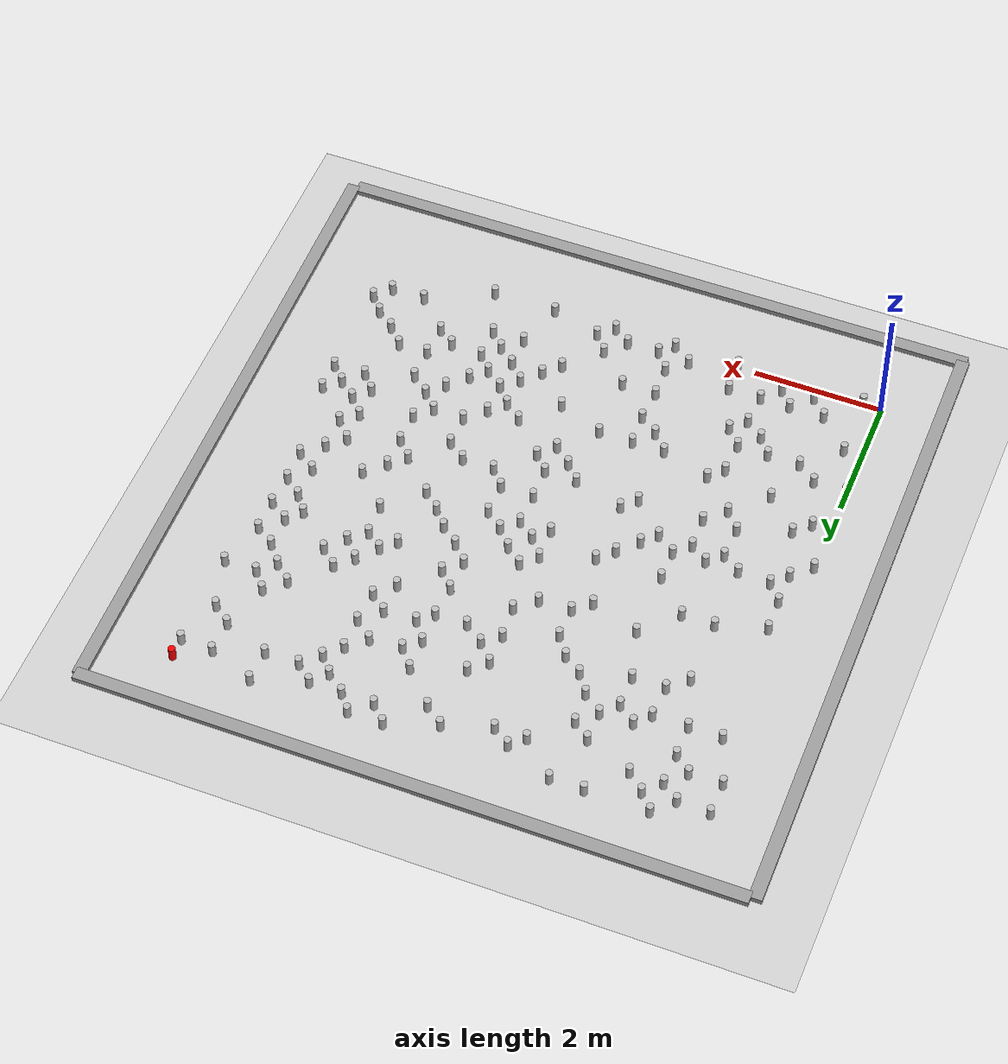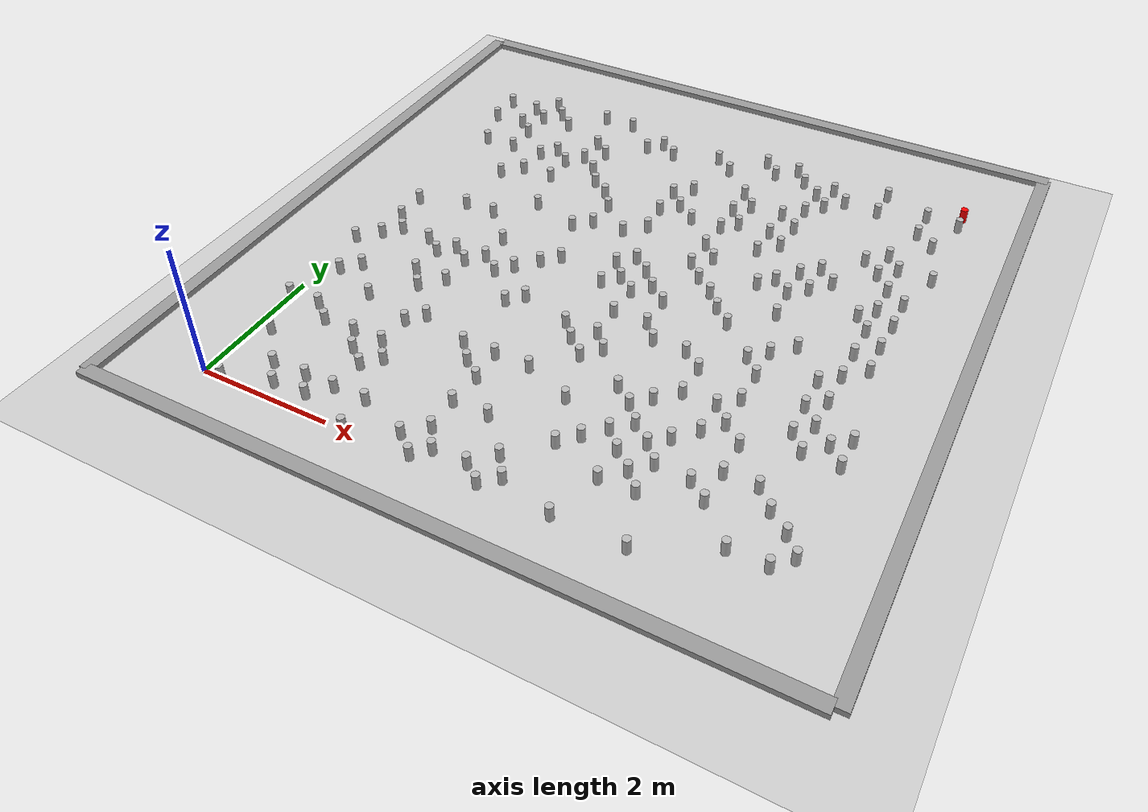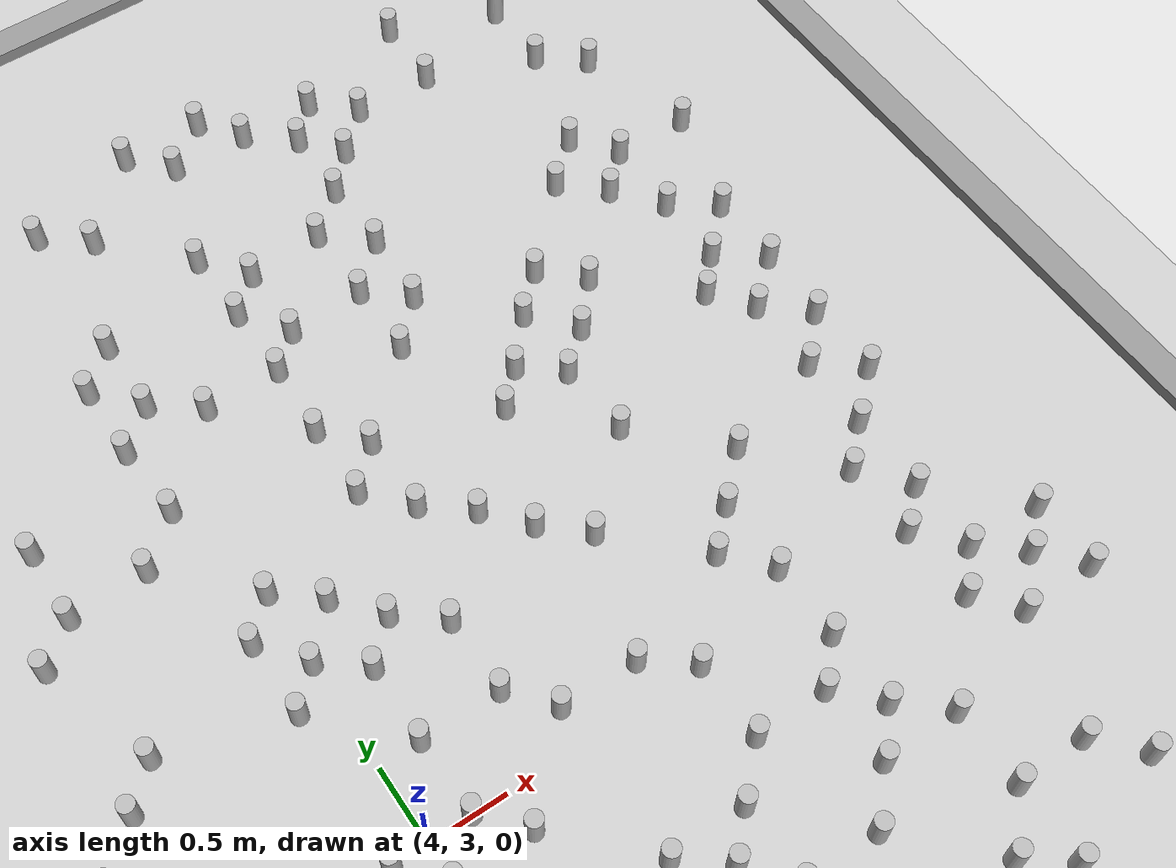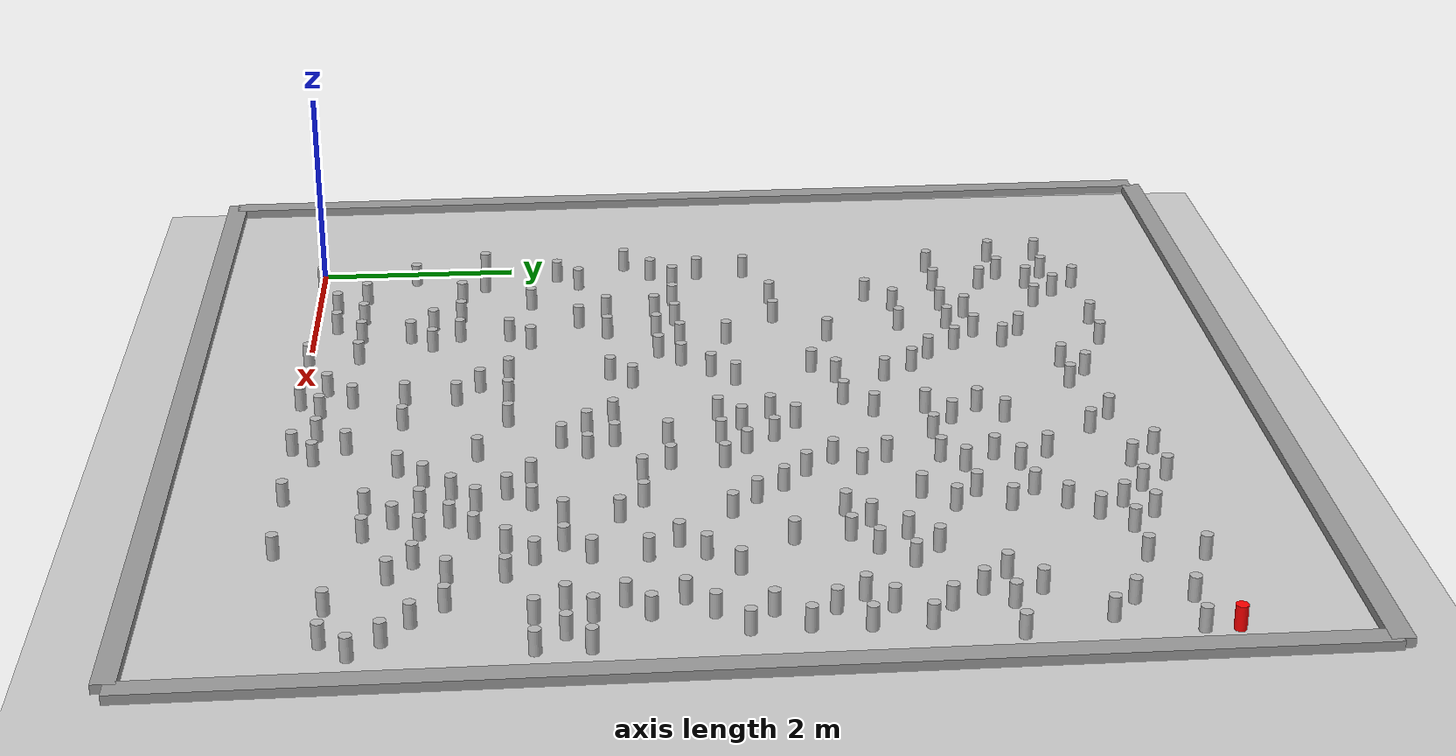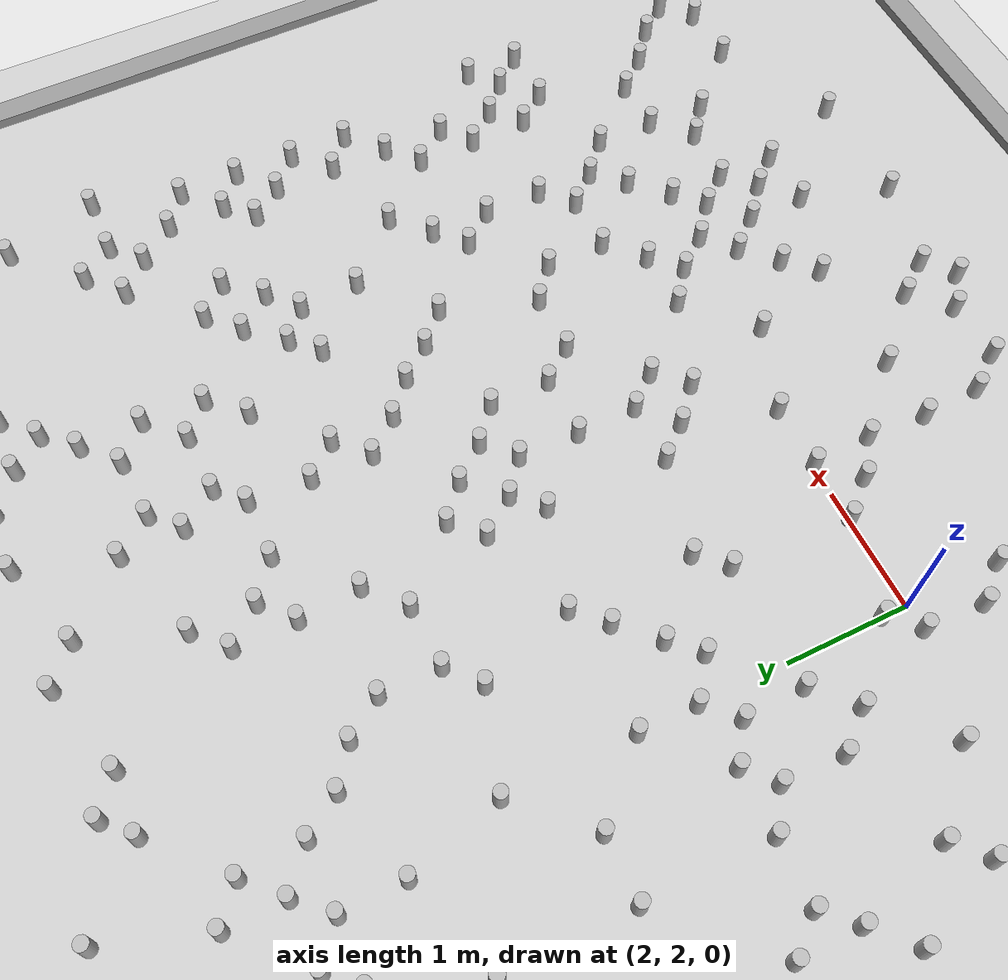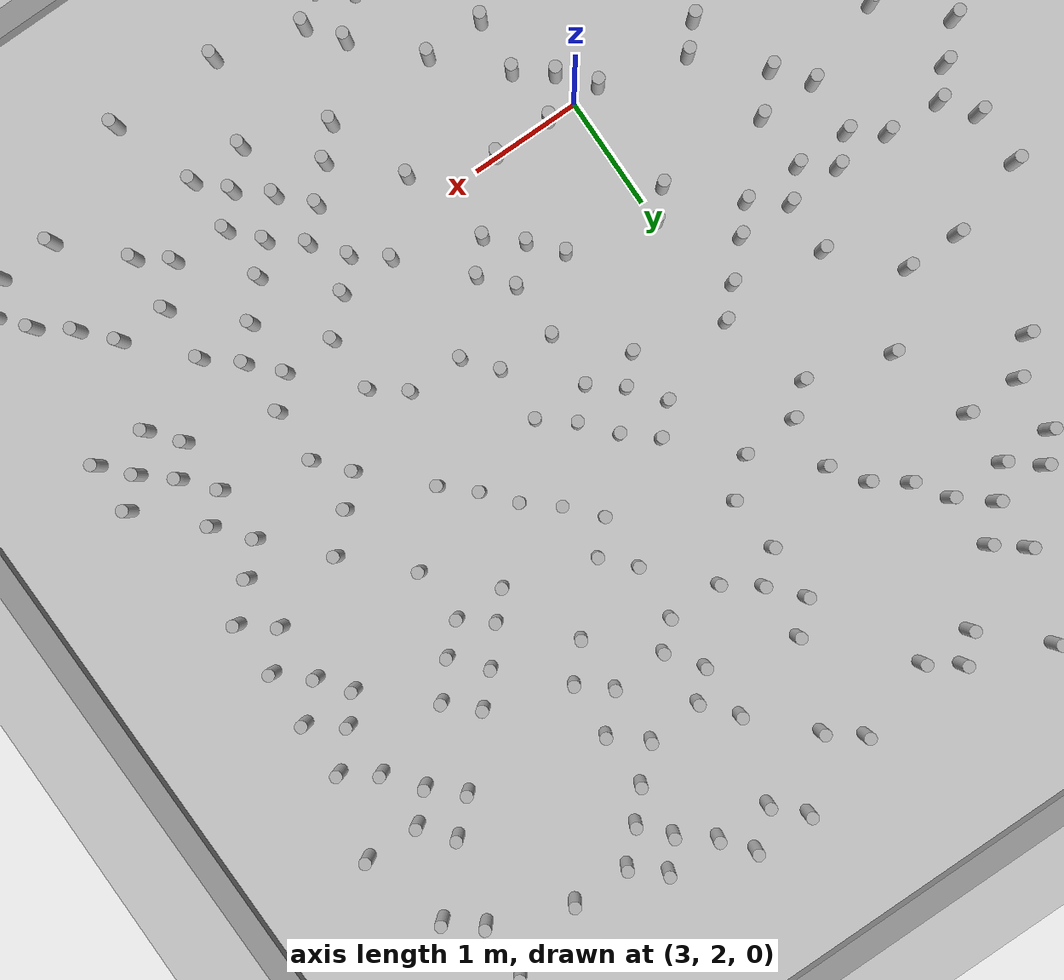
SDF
<sdf version="1.6">
 <world name="default">
  <light name="sun" type="directional">
   <pose>0 0 10 0 -0 0</pose>
   <diffuse>0.8 0.8 0.8 1</diffuse>
   <specular>0.1 0.1 0.1 1</specular>
   <attenuation>
    <range>1000</range>
    <constant>0.9</constant>
    <linear>0.01</linear>
    <quadratic>0.001</quadratic>
   </attenuation>
   <direction>-0.5 0.5 -1</direction>
  </light>
  <model name="ground_plane">
   <static>1</static>
   <link name="link">
    <collision name="collision">
     <geometry><plane><normal>0 0 1</normal><size>100 100</size></plane></geometry>
     <surface><friction><ode><mu>100</mu><mu2>50</mu2></ode></friction></surface>
    </collision>
    <visual name="visual">
     <cast_shadows>0</cast_shadows>
     <geometry><plane><normal>0 0 1</normal><size>100 100</size></plane></geometry>
     <material>
      <script><uri>file://media/materials/scripts/gazebo.material</uri><name>Gazebo/Grey</name></script>
     </material>
    </visual>
   </link>
  </model>
  <gravity>0 0 -9.8</gravity>
  <magnetic_field>6e-06 2.3e-05 -4.2e-05</magnetic_field>
  <atmosphere type="adiabatic"/>
  <physics name="default_physics" default="0" type="ode">
   <max_step_size>0.001</max_step_size>
   <real_time_factor>1</real_time_factor>
   <real_time_update_rate>1000</real_time_update_rate>
  </physics>
  <scene><ambient>0.4 0.4 0.4 1</ambient><background>0.7 0.7 0.7 1</background><shadows>1</shadows></scene>
  <spherical_coordinates>
   <surface_model>EARTH_WGS84</surface_model>
   <latitude_deg>0</latitude_deg>
   <longitude_deg>0</longitude_deg>
   <elevation>0</elevation>
   <heading_deg>0</heading_deg>
  </spherical_coordinates>
  <model name="goal">
   <link name="link">
    <pose>0 0 0.115 0 -0 0</pose>
    <inertial>
     <mass>0.0005</mass>
     <inertia><ixx>0.00058</ixx><ixy>0</ixy><ixz>0</ixz><iyy>0.00058</iyy><iyz>0</iyz><izz>0.00019</izz></inertia>
    </inertial>
    <visual name="visual">
     <geometry><cylinder><radius>0.055</radius><length>0.23</length></cylinder></geometry>
     <material>
      <script>
       <uri>model://beer/materials/scripts</uri>
       <uri>model://beer/materials/textures</uri>
       <name>Beer/Diffuse</name>
      </script>
      <ambient>1 0 0 1</ambient>
      <diffuse>1 0 0 1</diffuse>
      <specular>0 0 0 1</specular>
      <emissive>0 0 0 1</emissive>
      <shader type="vertex"><normal_map>__default__</normal_map></shader>
     </material>
    </visual>
    <collision name="collision">
     <geometry><cylinder><radius>0.055</radius><length>0.23</length></cylinder></geometry>
     <surface>
      <friction>
       <ode><mu>1</mu><mu2>1</mu2><fdir1>0 0 0</fdir1><slip1>0</slip1><slip2>0</slip2></ode>
       <torsional>
        <coefficient>1</coefficient>
        <patch_radius>0</patch_radius>
        <surface_radius>0</surface_radius>
        <use_patch_radius>1</use_patch_radius>
        <ode><slip>0</slip></ode>
       </torsional>
      </friction>
      <bounce><restitution_coefficient>0</restitution_coefficient><threshold>1e+06</threshold></bounce>
      <contact>
       <collide_without_contact>0</collide_without_contact>
       <collide_without_contact_bitmask>1</collide_without_contact_bitmask>
       <collide_bitmask>1</collide_bitmask>
       <ode>
        <soft_cfm>0</soft_cfm>
        <soft_erp>0.2</soft_erp>
        <kp>1e+13</kp>
        <kd>1</kd>
        <max_vel>0.01</max_vel>
        <min_depth>0</min_depth>
       </ode>
       <bullet>
        <split_impulse>1</split_impulse>
        <split_impulse_penetration_threshold>-0.01</split_impulse_penetration_threshold>
        <soft_cfm>0</soft_cfm>
        <soft_erp>0.2</soft_erp>
        <kp>1e+13</kp>
        <kd>1</kd>
       </bullet>
      </contact>
     </surface>
    </collision>
   </link>
   <static>0</static>
   <pose>8.0 8.0 -9e-06 -1e-06 -4e-06 0</pose>
  </model>
  <model name="wall1">
   <static>1</static>
   <link name="link">
    <pose>0 0 0.42 0 -0 0</pose>
    <collision name="collision"><geometry><box><size>10 0.2 0.084</size></box></geometry></collision>
    <visual name="visual">
     <cast_shadows>0</cast_shadows>
     <geometry><box><size>10 0.2 0.084</size></box></geometry>
     <material>
      <script>
       <uri>model://grey_wall/materials/scripts</uri>
       <uri>model://grey_wall/materials/textures</uri>
       <name>vrc/grey_wall</name>
      </script>
     </material>
    </visual>
   </link>
   <pose>-1 4.0 0 0 -0 -1.55905</pose>
  </model>
  <model name="wall2">
   <static>1</static>
   <link name="link">
    <pose>0 0 0.42 0 -0 0</pose>
    <collision name="collision"><geometry><box><size>10 0.2 0.084</size></box></geometry></collision>
    <visual name="visual">
     <cast_shadows>0</cast_shadows>
     <geometry><box><size>10 0.2 0.084</size></box></geometry>
     <material>
      <script>
       <uri>model://grey_wall/materials/scripts</uri>
       <uri>model://grey_wall/materials/textures</uri>
       <name>vrc/grey_wall</name>
      </script>
     </material>
    </visual>
   </link>
   <pose>4.0 9.0 0 0 -0 0</pose>
  </model>
  <model name="wall3">
   <static>1</static>
   <link name="link">
    <pose>0 0 0.42 0 -0 0</pose>
    <collision name="collision"><geometry><box><size>10 0.2 0.084</size></box></geometry></collision>
    <visual name="visual">
     <cast_shadows>0</cast_shadows>
     <geometry><box><size>10 0.2 0.084</size></box></geometry>
     <material>
      <script>
       <uri>model://grey_wall/materials/scripts</uri>
       <uri>model://grey_wall/materials/textures</uri>
       <name>vrc/grey_wall</name>
      </script>
     </material>
    </visual>
   </link>
   <pose>9.0 4.0 0 0 -0 -1.55905</pose>
  </model>
  <model name="wall4">
   <static>1</static>
   <link name="link">
    <pose>0 0 0.42 0 -0 0</pose>
    <collision name="collision"><geometry><box><size>10 0.2 0.084</size></box></geometry></collision>
    <visual name="visual">
     <cast_shadows>0</cast_shadows>
     <geometry><box><size>10 0.2 0.084</size></box></geometry>
     <material>
      <script>
       <uri>model://grey_wall/materials/scripts</uri>
       <uri>model://grey_wall/materials/textures</uri>
       <name>vrc/grey_wall</name>
      </script>
     </material>
    </visual>
   </link>
   <pose>4.0 -1 0 0 -0 0</pose>
  </model>
  <model name="can3.258957673971.0">
   <link name="link">
    <pose>0 0 0.115 0 -0 0</pose>
    <inertial>
     <mass>0.39</mass>
     <inertia><ixx>0.00058</ixx><ixy>0</ixy><ixz>0</ixz><iyy>0.00058</iyy><iyz>0</iyz><izz>0.00019</izz></inertia>
    </inertial>
    <collision name="collision">
     <geometry><cylinder><radius>0.055</radius><length>0.23</length></cylinder></geometry>
    </collision>
    <visual name="visual">
     <geometry><cylinder><radius>0.055</radius><length>0.23</length></cylinder></geometry>
     <material>
      <script>
       <uri>model://beer/materials/scripts</uri>
       <uri>model://beer/materials/textures</uri>
       <name>Beer/Diffuse</name>
      </script>
     </material>
    </visual>
   </link>
   <pose>3.25895767397 1.0 -2e-06 1e-06 0 -9.5e-05</pose>
  </model>
  <model name="can1.782080667241.0">
   <link name="link">
    <pose>0 0 0.115 0 -0 0</pose>
    <inertial>
     <mass>0.39</mass>
     <inertia><ixx>0.00058</ixx><ixy>0</ixy><ixz>0</ixz><iyy>0.00058</iyy><iyz>0</iyz><izz>0.00019</izz></inertia>
    </inertial>
    <collision name="collision">
     <geometry><cylinder><radius>0.055</radius><length>0.23</length></cylinder></geometry>
    </collision>
    <visual name="visual">
     <geometry><cylinder><radius>0.055</radius><length>0.23</length></cylinder></geometry>
     <material>
      <script>
       <uri>model://beer/materials/scripts</uri>
       <uri>model://beer/materials/textures</uri>
       <name>Beer/Diffuse</name>
      </script>
     </material>
    </visual>
   </link>
   <pose>1.78208066724 1.0 -2e-06 1e-06 0 -9.5e-05</pose>
  </model>
  <model name="can6.55.21690439198">
   <link name="link">
    <pose>0 0 0.115 0 -0 0</pose>
    <inertial>
     <mass>0.39</mass>
     <inertia><ixx>0.00058</ixx><ixy>0</ixy><ixz>0</ixz><iyy>0.00058</iyy><iyz>0</iyz><izz>0.00019</izz></inertia>
    </inertial>
    <collision name="collision">
     <geometry><cylinder><radius>0.055</radius><length>0.23</length></cylinder></geometry>
    </collision>
    <visual name="visual">
     <geometry><cylinder><radius>0.055</radius><length>0.23</length></cylinder></geometry>
     <material>
      <script>
       <uri>model://beer/materials/scripts</uri>
       <uri>model://beer/materials/textures</uri>
       <name>Beer/Diffuse</name>
      </script>
     </material>
    </visual>
   </link>
   <pose>6.5 5.21690439198 -2e-06 1e-06 0 -9.5e-05</pose>
  </model>
  <model name="can1.00.207146952871">
   <link name="link">
    <pose>0 0 0.115 0 -0 0</pose>
    <inertial>
     <mass>0.39</mass>
     <inertia><ixx>0.00058</ixx><ixy>0</ixy><ixz>0</ixz><iyy>0.00058</iyy><iyz>0</iyz><izz>0.00019</izz></inertia>
    </inertial>
    <collision name="collision">
     <geometry><cylinder><radius>0.055</radius><length>0.23</length></cylinder></geometry>
    </collision>
    <visual name="visual">
     <geometry><cylinder><radius>0.055</radius><length>0.23</length></cylinder></geometry>
     <material>
      <script>
       <uri>model://beer/materials/scripts</uri>
       <uri>model://beer/materials/textures</uri>
       <name>Beer/Diffuse</name>
      </script>
     </material>
    </visual>
   </link>
   <pose>1.0 0.207146952871 -2e-06 1e-06 0 -9.5e-05</pose>
  </model>
  <model name="can5.55.72347122865">
   <link name="link">
    <pose>0 0 0.115 0 -0 0</pose>
    <inertial>
     <mass>0.39</mass>
     <inertia><ixx>0.00058</ixx><ixy>0</ixy><ixz>0</ixz><iyy>0.00058</iyy><iyz>0</iyz><izz>0.00019</izz></inertia>
    </inertial>
    <collision name="collision">
     <geometry><cylinder><radius>0.055</radius><length>0.23</length></cylinder></geometry>
    </collision>
    <visual name="visual">
     <geometry><cylinder><radius>0.055</radius><length>0.23</length></cylinder></geometry>
     <material>
      <script>
       <uri>model://beer/materials/scripts</uri>
       <uri>model://beer/materials/textures</uri>
       <name>Beer/Diffuse</name>
      </script>
     </material>
    </visual>
   </link>
   <pose>5.5 5.72347122865 -2e-06 1e-06 0 -9.5e-05</pose>
  </model>
  <model name="can5.759015337364.0">
   <link name="link">
    <pose>0 0 0.115 0 -0 0</pose>
    <inertial>
     <mass>0.39</mass>
     <inertia><ixx>0.00058</ixx><ixy>0</ixy><ixz>0</ixz><iyy>0.00058</iyy><iyz>0</iyz><izz>0.00019</izz></inertia>
    </inertial>
    <collision name="collision">
     <geometry><cylinder><radius>0.055</radius><length>0.23</length></cylinder></geometry>
    </collision>
    <visual name="visual">
     <geometry><cylinder><radius>0.055</radius><length>0.23</length></cylinder></geometry>
     <material>
      <script>
       <uri>model://beer/materials/scripts</uri>
       <uri>model://beer/materials/textures</uri>
       <name>Beer/Diffuse</name>
      </script>
     </material>
    </visual>
   </link>
   <pose>5.75901533736 4.0 -2e-06 1e-06 0 -9.5e-05</pose>
  </model>
  <model name="can1.03.7041113807">
   <link name="link">
    <pose>0 0 0.115 0 -0 0</pose>
    <inertial>
     <mass>0.39</mass>
     <inertia><ixx>0.00058</ixx><ixy>0</ixy><ixz>0</ixz><iyy>0.00058</iyy><iyz>0</iyz><izz>0.00019</izz></inertia>
    </inertial>
    <collision name="collision">
     <geometry><cylinder><radius>0.055</radius><length>0.23</length></cylinder></geometry>
    </collision>
    <visual name="visual">
     <geometry><cylinder><radius>0.055</radius><length>0.23</length></cylinder></geometry>
     <material>
      <script>
       <uri>model://beer/materials/scripts</uri>
       <uri>model://beer/materials/textures</uri>
       <name>Beer/Diffuse</name>
      </script>
     </material>
    </visual>
   </link>
   <pose>1.0 3.7041113807 -2e-06 1e-06 0 -9.5e-05</pose>
  </model>
  <model name="can6.53.72370780713">
   <link name="link">
    <pose>0 0 0.115 0 -0 0</pose>
    <inertial>
     <mass>0.39</mass>
     <inertia><ixx>0.00058</ixx><ixy>0</ixy><ixz>0</ixz><iyy>0.00058</iyy><iyz>0</iyz><izz>0.00019</izz></inertia>
    </inertial>
    <collision name="collision">
     <geometry><cylinder><radius>0.055</radius><length>0.23</length></cylinder></geometry>
    </collision>
    <visual name="visual">
     <geometry><cylinder><radius>0.055</radius><length>0.23</length></cylinder></geometry>
     <material>
      <script>
       <uri>model://beer/materials/scripts</uri>
       <uri>model://beer/materials/textures</uri>
       <name>Beer/Diffuse</name>
      </script>
     </material>
    </visual>
   </link>
   <pose>6.5 3.72370780713 -2e-06 1e-06 0 -9.5e-05</pose>
  </model>
  <model name="can3.275578954057.5">
   <link name="link">
    <pose>0 0 0.115 0 -0 0</pose>
    <inertial>
     <mass>0.39</mass>
     <inertia><ixx>0.00058</ixx><ixy>0</ixy><ixz>0</ixz><iyy>0.00058</iyy><iyz>0</iyz><izz>0.00019</izz></inertia>
    </inertial>
    <collision name="collision">
     <geometry><cylinder><radius>0.055</radius><length>0.23</length></cylinder></geometry>
    </collision>
    <visual name="visual">
     <geometry><cylinder><radius>0.055</radius><length>0.23</length></cylinder></geometry>
     <material>
      <script>
       <uri>model://beer/materials/scripts</uri>
       <uri>model://beer/materials/textures</uri>
       <name>Beer/Diffuse</name>
      </script>
     </material>
    </visual>
   </link>
   <pose>3.27557895405 7.5 -2e-06 1e-06 0 -9.5e-05</pose>
  </model>
  <model name="can6.784772272632.0">
   <link name="link">
    <pose>0 0 0.115 0 -0 0</pose>
    <inertial>
     <mass>0.39</mass>
     <inertia><ixx>0.00058</ixx><ixy>0</ixy><ixz>0</ixz><iyy>0.00058</iyy><iyz>0</iyz><izz>0.00019</izz></inertia>
    </inertial>
    <collision name="collision">
     <geometry><cylinder><radius>0.055</radius><length>0.23</length></cylinder></geometry>
    </collision>
    <visual name="visual">
     <geometry><cylinder><radius>0.055</radius><length>0.23</length></cylinder></geometry>
     <material>
      <script>
       <uri>model://beer/materials/scripts</uri>
       <uri>model://beer/materials/textures</uri>
       <name>Beer/Diffuse</name>
      </script>
     </material>
    </visual>
   </link>
   <pose>6.78477227263 2.0 -2e-06 1e-06 0 -9.5e-05</pose>
  </model>
  <model name="can0.07.72709570914">
   <link name="link">
    <pose>0 0 0.115 0 -0 0</pose>
    <inertial>
     <mass>0.39</mass>
     <inertia><ixx>0.00058</ixx><ixy>0</ixy><ixz>0</ixz><iyy>0.00058</iyy><iyz>0</iyz><izz>0.00019</izz></inertia>
    </inertial>
    <collision name="collision">
     <geometry><cylinder><radius>0.055</radius><length>0.23</length></cylinder></geometry>
    </collision>
    <visual name="visual">
     <geometry><cylinder><radius>0.055</radius><length>0.23</length></cylinder></geometry>
     <material>
      <script>
       <uri>model://beer/materials/scripts</uri>
       <uri>model://beer/materials/textures</uri>
       <name>Beer/Diffuse</name>
      </script>
     </material>
    </visual>
   </link>
   <pose>0.0 7.72709570914 -2e-06 1e-06 0 -9.5e-05</pose>
  </model>
  <model name="can1.51.21977305857">
   <link name="link">
    <pose>0 0 0.115 0 -0 0</pose>
    <inertial>
     <mass>0.39</mass>
     <inertia><ixx>0.00058</ixx><ixy>0</ixy><ixz>0</ixz><iyy>0.00058</iyy><iyz>0</iyz><izz>0.00019</izz></inertia>
    </inertial>
    <collision name="collision">
     <geometry><cylinder><radius>0.055</radius><length>0.23</length></cylinder></geometry>
    </collision>
    <visual name="visual">
     <geometry><cylinder><radius>0.055</radius><length>0.23</length></cylinder></geometry>
     <material>
      <script>
       <uri>model://beer/materials/scripts</uri>
       <uri>model://beer/materials/textures</uri>
       <name>Beer/Diffuse</name>
      </script>
     </material>
    </visual>
   </link>
   <pose>1.5 1.21977305857 -2e-06 1e-06 0 -9.5e-05</pose>
  </model>
  <model name="can4.02.74444031951">
   <link name="link">
    <pose>0 0 0.115 0 -0 0</pose>
    <inertial>
     <mass>0.39</mass>
     <inertia><ixx>0.00058</ixx><ixy>0</ixy><ixz>0</ixz><iyy>0.00058</iyy><iyz>0</iyz><izz>0.00019</izz></inertia>
    </inertial>
    <collision name="collision">
     <geometry><cylinder><radius>0.055</radius><length>0.23</length></cylinder></geometry>
    </collision>
    <visual name="visual">
     <geometry><cylinder><radius>0.055</radius><length>0.23</length></cylinder></geometry>
     <material>
      <script>
       <uri>model://beer/materials/scripts</uri>
       <uri>model://beer/materials/textures</uri>
       <name>Beer/Diffuse</name>
      </script>
     </material>
    </visual>
   </link>
   <pose>4.0 2.74444031951 -2e-06 1e-06 0 -9.5e-05</pose>
  </model>
  <model name="can0.7857185059218.0">
   <link name="link">
    <pose>0 0 0.115 0 -0 0</pose>
    <inertial>
     <mass>0.39</mass>
     <inertia><ixx>0.00058</ixx><ixy>0</ixy><ixz>0</ixz><iyy>0.00058</iyy><iyz>0</iyz><izz>0.00019</izz></inertia>
    </inertial>
    <collision name="collision">
     <geometry><cylinder><radius>0.055</radius><length>0.23</length></cylinder></geometry>
    </collision>
    <visual name="visual">
     <geometry><cylinder><radius>0.055</radius><length>0.23</length></cylinder></geometry>
     <material>
      <script>
       <uri>model://beer/materials/scripts</uri>
       <uri>model://beer/materials/textures</uri>
       <name>Beer/Diffuse</name>
      </script>
     </material>
    </visual>
   </link>
   <pose>0.785718505921 8.0 -2e-06 1e-06 0 -9.5e-05</pose>
  </model>
  <model name="can7.52.23811705391">
   <link name="link">
    <pose>0 0 0.115 0 -0 0</pose>
    <inertial>
     <mass>0.39</mass>
     <inertia><ixx>0.00058</ixx><ixy>0</ixy><ixz>0</ixz><iyy>0.00058</iyy><iyz>0</iyz><izz>0.00019</izz></inertia>
    </inertial>
    <collision name="collision">
     <geometry><cylinder><radius>0.055</radius><length>0.23</length></cylinder></geometry>
    </collision>
    <visual name="visual">
     <geometry><cylinder><radius>0.055</radius><length>0.23</length></cylinder></geometry>
     <material>
      <script>
       <uri>model://beer/materials/scripts</uri>
       <uri>model://beer/materials/textures</uri>
       <name>Beer/Diffuse</name>
      </script>
     </material>
    </visual>
   </link>
   <pose>7.5 2.23811705391 -2e-06 1e-06 0 -9.5e-05</pose>
  </model>
  <model name="can1.772515468821.5">
   <link name="link">
    <pose>0 0 0.115 0 -0 0</pose>
    <inertial>
     <mass>0.39</mass>
     <inertia><ixx>0.00058</ixx><ixy>0</ixy><ixz>0</ixz><iyy>0.00058</iyy><iyz>0</iyz><izz>0.00019</izz></inertia>
    </inertial>
    <collision name="collision">
     <geometry><cylinder><radius>0.055</radius><length>0.23</length></cylinder></geometry>
    </collision>
    <visual name="visual">
     <geometry><cylinder><radius>0.055</radius><length>0.23</length></cylinder></geometry>
     <material>
      <script>
       <uri>model://beer/materials/scripts</uri>
       <uri>model://beer/materials/textures</uri>
       <name>Beer/Diffuse</name>
      </script>
     </material>
    </visual>
   </link>
   <pose>1.77251546882 1.5 -2e-06 1e-06 0 -9.5e-05</pose>
  </model>
  <model name="can5.52.22546799315">
   <link name="link">
    <pose>0 0 0.115 0 -0 0</pose>
    <inertial>
     <mass>0.39</mass>
     <inertia><ixx>0.00058</ixx><ixy>0</ixy><ixz>0</ixz><iyy>0.00058</iyy><iyz>0</iyz><izz>0.00019</izz></inertia>
    </inertial>
    <collision name="collision">
     <geometry><cylinder><radius>0.055</radius><length>0.23</length></cylinder></geometry>
    </collision>
    <visual name="visual">
     <geometry><cylinder><radius>0.055</radius><length>0.23</length></cylinder></geometry>
     <material>
      <script>
       <uri>model://beer/materials/scripts</uri>
       <uri>model://beer/materials/textures</uri>
       <name>Beer/Diffuse</name>
      </script>
     </material>
    </visual>
   </link>
   <pose>5.5 2.22546799315 -2e-06 1e-06 0 -9.5e-05</pose>
  </model>
  <model name="can5.51.7250479158">
   <link name="link">
    <pose>0 0 0.115 0 -0 0</pose>
    <inertial>
     <mass>0.39</mass>
     <inertia><ixx>0.00058</ixx><ixy>0</ixy><ixz>0</ixz><iyy>0.00058</iyy><iyz>0</iyz><izz>0.00019</izz></inertia>
    </inertial>
    <collision name="collision">
     <geometry><cylinder><radius>0.055</radius><length>0.23</length></cylinder></geometry>
    </collision>
    <visual name="visual">
     <geometry><cylinder><radius>0.055</radius><length>0.23</length></cylinder></geometry>
     <material>
      <script>
       <uri>model://beer/materials/scripts</uri>
       <uri>model://beer/materials/textures</uri>
       <name>Beer/Diffuse</name>
      </script>
     </material>
    </visual>
   </link>
   <pose>5.5 1.7250479158 -2e-06 1e-06 0 -9.5e-05</pose>
  </model>
  <model name="can4.761329393848.0">
   <link name="link">
    <pose>0 0 0.115 0 -0 0</pose>
    <inertial>
     <mass>0.39</mass>
     <inertia><ixx>0.00058</ixx><ixy>0</ixy><ixz>0</ixz><iyy>0.00058</iyy><iyz>0</iyz><izz>0.00019</izz></inertia>
    </inertial>
    <collision name="collision">
     <geometry><cylinder><radius>0.055</radius><length>0.23</length></cylinder></geometry>
    </collision>
    <visual name="visual">
     <geometry><cylinder><radius>0.055</radius><length>0.23</length></cylinder></geometry>
     <material>
      <script>
       <uri>model://beer/materials/scripts</uri>
       <uri>model://beer/materials/textures</uri>
       <name>Beer/Diffuse</name>
      </script>
     </material>
    </visual>
   </link>
   <pose>4.76132939384 8.0 -2e-06 1e-06 0 -9.5e-05</pose>
  </model>
  <model name="can4.758347486425.0">
   <link name="link">
    <pose>0 0 0.115 0 -0 0</pose>
    <inertial>
     <mass>0.39</mass>
     <inertia><ixx>0.00058</ixx><ixy>0</ixy><ixz>0</ixz><iyy>0.00058</iyy><iyz>0</iyz><izz>0.00019</izz></inertia>
    </inertial>
    <collision name="collision">
     <geometry><cylinder><radius>0.055</radius><length>0.23</length></cylinder></geometry>
    </collision>
    <visual name="visual">
     <geometry><cylinder><radius>0.055</radius><length>0.23</length></cylinder></geometry>
     <material>
      <script>
       <uri>model://beer/materials/scripts</uri>
       <uri>model://beer/materials/textures</uri>
       <name>Beer/Diffuse</name>
      </script>
     </material>
    </visual>
   </link>
   <pose>4.75834748642 5.0 -2e-06 1e-06 0 -9.5e-05</pose>
  </model>
  <model name="can5.277275325034.5">
   <link name="link">
    <pose>0 0 0.115 0 -0 0</pose>
    <inertial>
     <mass>0.39</mass>
     <inertia><ixx>0.00058</ixx><ixy>0</ixy><ixz>0</ixz><iyy>0.00058</iyy><iyz>0</iyz><izz>0.00019</izz></inertia>
    </inertial>
    <collision name="collision">
     <geometry><cylinder><radius>0.055</radius><length>0.23</length></cylinder></geometry>
    </collision>
    <visual name="visual">
     <geometry><cylinder><radius>0.055</radius><length>0.23</length></cylinder></geometry>
     <material>
      <script>
       <uri>model://beer/materials/scripts</uri>
       <uri>model://beer/materials/textures</uri>
       <name>Beer/Diffuse</name>
      </script>
     </material>
    </visual>
   </link>
   <pose>5.27727532503 4.5 -2e-06 1e-06 0 -9.5e-05</pose>
  </model>
  <model name="can7.56.22754010514">
   <link name="link">
    <pose>0 0 0.115 0 -0 0</pose>
    <inertial>
     <mass>0.39</mass>
     <inertia><ixx>0.00058</ixx><ixy>0</ixy><ixz>0</ixz><iyy>0.00058</iyy><iyz>0</iyz><izz>0.00019</izz></inertia>
    </inertial>
    <collision name="collision">
     <geometry><cylinder><radius>0.055</radius><length>0.23</length></cylinder></geometry>
    </collision>
    <visual name="visual">
     <geometry><cylinder><radius>0.055</radius><length>0.23</length></cylinder></geometry>
     <material>
      <script>
       <uri>model://beer/materials/scripts</uri>
       <uri>model://beer/materials/textures</uri>
       <name>Beer/Diffuse</name>
      </script>
     </material>
    </visual>
   </link>
   <pose>7.5 6.22754010514 -2e-06 1e-06 0 -9.5e-05</pose>
  </model>
  <model name="can2.06.74284869615">
   <link name="link">
    <pose>0 0 0.115 0 -0 0</pose>
    <inertial>
     <mass>0.39</mass>
     <inertia><ixx>0.00058</ixx><ixy>0</ixy><ixz>0</ixz><iyy>0.00058</iyy><iyz>0</iyz><izz>0.00019</izz></inertia>
    </inertial>
    <collision name="collision">
     <geometry><cylinder><radius>0.055</radius><length>0.23</length></cylinder></geometry>
    </collision>
    <visual name="visual">
     <geometry><cylinder><radius>0.055</radius><length>0.23</length></cylinder></geometry>
     <material>
      <script>
       <uri>model://beer/materials/scripts</uri>
       <uri>model://beer/materials/textures</uri>
       <name>Beer/Diffuse</name>
      </script>
     </material>
    </visual>
   </link>
   <pose>2.0 6.74284869615 -2e-06 1e-06 0 -9.5e-05</pose>
  </model>
  <model name="can4.281534310790.5">
   <link name="link">
    <pose>0 0 0.115 0 -0 0</pose>
    <inertial>
     <mass>0.39</mass>
     <inertia><ixx>0.00058</ixx><ixy>0</ixy><ixz>0</ixz><iyy>0.00058</iyy><iyz>0</iyz><izz>0.00019</izz></inertia>
    </inertial>
    <collision name="collision">
     <geometry><cylinder><radius>0.055</radius><length>0.23</length></cylinder></geometry>
    </collision>
    <visual name="visual">
     <geometry><cylinder><radius>0.055</radius><length>0.23</length></cylinder></geometry>
     <material>
      <script>
       <uri>model://beer/materials/scripts</uri>
       <uri>model://beer/materials/textures</uri>
       <name>Beer/Diffuse</name>
      </script>
     </material>
    </visual>
   </link>
   <pose>4.28153431079 0.5 -2e-06 1e-06 0 -9.5e-05</pose>
  </model>
  <model name="can7.263469234763.0">
   <link name="link">
    <pose>0 0 0.115 0 -0 0</pose>
    <inertial>
     <mass>0.39</mass>
     <inertia><ixx>0.00058</ixx><ixy>0</ixy><ixz>0</ixz><iyy>0.00058</iyy><iyz>0</iyz><izz>0.00019</izz></inertia>
    </inertial>
    <collision name="collision">
     <geometry><cylinder><radius>0.055</radius><length>0.23</length></cylinder></geometry>
    </collision>
    <visual name="visual">
     <geometry><cylinder><radius>0.055</radius><length>0.23</length></cylinder></geometry>
     <material>
      <script>
       <uri>model://beer/materials/scripts</uri>
       <uri>model://beer/materials/textures</uri>
       <name>Beer/Diffuse</name>
      </script>
     </material>
    </visual>
   </link>
   <pose>7.26346923476 3.0 -2e-06 1e-06 0 -9.5e-05</pose>
  </model>
  <model name="can7.791522727644.0">
   <link name="link">
    <pose>0 0 0.115 0 -0 0</pose>
    <inertial>
     <mass>0.39</mass>
     <inertia><ixx>0.00058</ixx><ixy>0</ixy><ixz>0</ixz><iyy>0.00058</iyy><iyz>0</iyz><izz>0.00019</izz></inertia>
    </inertial>
    <collision name="collision">
     <geometry><cylinder><radius>0.055</radius><length>0.23</length></cylinder></geometry>
    </collision>
    <visual name="visual">
     <geometry><cylinder><radius>0.055</radius><length>0.23</length></cylinder></geometry>
     <material>
      <script>
       <uri>model://beer/materials/scripts</uri>
       <uri>model://beer/materials/textures</uri>
       <name>Beer/Diffuse</name>
      </script>
     </material>
    </visual>
   </link>
   <pose>7.79152272764 4.0 -2e-06 1e-06 0 -9.5e-05</pose>
  </model>
  <model name="can1.292283602720.5">
   <link name="link">
    <pose>0 0 0.115 0 -0 0</pose>
    <inertial>
     <mass>0.39</mass>
     <inertia><ixx>0.00058</ixx><ixy>0</ixy><ixz>0</ixz><iyy>0.00058</iyy><iyz>0</iyz><izz>0.00019</izz></inertia>
    </inertial>
    <collision name="collision">
     <geometry><cylinder><radius>0.055</radius><length>0.23</length></cylinder></geometry>
    </collision>
    <visual name="visual">
     <geometry><cylinder><radius>0.055</radius><length>0.23</length></cylinder></geometry>
     <material>
      <script>
       <uri>model://beer/materials/scripts</uri>
       <uri>model://beer/materials/textures</uri>
       <name>Beer/Diffuse</name>
      </script>
     </material>
    </visual>
   </link>
   <pose>1.29228360272 0.5 -2e-06 1e-06 0 -9.5e-05</pose>
  </model>
  <model name="can3.04.22822890088">
   <link name="link">
    <pose>0 0 0.115 0 -0 0</pose>
    <inertial>
     <mass>0.39</mass>
     <inertia><ixx>0.00058</ixx><ixy>0</ixy><ixz>0</ixz><iyy>0.00058</iyy><iyz>0</iyz><izz>0.00019</izz></inertia>
    </inertial>
    <collision name="collision">
     <geometry><cylinder><radius>0.055</radius><length>0.23</length></cylinder></geometry>
    </collision>
    <visual name="visual">
     <geometry><cylinder><radius>0.055</radius><length>0.23</length></cylinder></geometry>
     <material>
      <script>
       <uri>model://beer/materials/scripts</uri>
       <uri>model://beer/materials/textures</uri>
       <name>Beer/Diffuse</name>
      </script>
     </material>
    </visual>
   </link>
   <pose>3.0 4.22822890088 -2e-06 1e-06 0 -9.5e-05</pose>
  </model>
  <model name="can2.787474284776.0">
   <link name="link">
    <pose>0 0 0.115 0 -0 0</pose>
    <inertial>
     <mass>0.39</mass>
     <inertia><ixx>0.00058</ixx><ixy>0</ixy><ixz>0</ixz><iyy>0.00058</iyy><iyz>0</iyz><izz>0.00019</izz></inertia>
    </inertial>
    <collision name="collision">
     <geometry><cylinder><radius>0.055</radius><length>0.23</length></cylinder></geometry>
    </collision>
    <visual name="visual">
     <geometry><cylinder><radius>0.055</radius><length>0.23</length></cylinder></geometry>
     <material>
      <script>
       <uri>model://beer/materials/scripts</uri>
       <uri>model://beer/materials/textures</uri>
       <name>Beer/Diffuse</name>
      </script>
     </material>
    </visual>
   </link>
   <pose>2.78747428477 6.0 -2e-06 1e-06 0 -9.5e-05</pose>
  </model>
  <model name="can4.267930622410.0">
   <link name="link">
    <pose>0 0 0.115 0 -0 0</pose>
    <inertial>
     <mass>0.39</mass>
     <inertia><ixx>0.00058</ixx><ixy>0</ixy><ixz>0</ixz><iyy>0.00058</iyy><iyz>0</iyz><izz>0.00019</izz></inertia>
    </inertial>
    <collision name="collision">
     <geometry><cylinder><radius>0.055</radius><length>0.23</length></cylinder></geometry>
    </collision>
    <visual name="visual">
     <geometry><cylinder><radius>0.055</radius><length>0.23</length></cylinder></geometry>
     <material>
      <script>
       <uri>model://beer/materials/scripts</uri>
       <uri>model://beer/materials/textures</uri>
       <name>Beer/Diffuse</name>
      </script>
     </material>
    </visual>
   </link>
   <pose>4.26793062241 0.0 -2e-06 1e-06 0 -9.5e-05</pose>
  </model>
  <model name="can6.287995954034.5">
   <link name="link">
    <pose>0 0 0.115 0 -0 0</pose>
    <inertial>
     <mass>0.39</mass>
     <inertia><ixx>0.00058</ixx><ixy>0</ixy><ixz>0</ixz><iyy>0.00058</iyy><iyz>0</iyz><izz>0.00019</izz></inertia>
    </inertial>
    <collision name="collision">
     <geometry><cylinder><radius>0.055</radius><length>0.23</length></cylinder></geometry>
    </collision>
    <visual name="visual">
     <geometry><cylinder><radius>0.055</radius><length>0.23</length></cylinder></geometry>
     <material>
      <script>
       <uri>model://beer/materials/scripts</uri>
       <uri>model://beer/materials/textures</uri>
       <name>Beer/Diffuse</name>
      </script>
     </material>
    </visual>
   </link>
   <pose>6.28799595403 4.5 -2e-06 1e-06 0 -9.5e-05</pose>
  </model>
  <model name="can2.04.20142502307">
   <link name="link">
    <pose>0 0 0.115 0 -0 0</pose>
    <inertial>
     <mass>0.39</mass>
     <inertia><ixx>0.00058</ixx><ixy>0</ixy><ixz>0</ixz><iyy>0.00058</iyy><iyz>0</iyz><izz>0.00019</izz></inertia>
    </inertial>
    <collision name="collision">
     <geometry><cylinder><radius>0.055</radius><length>0.23</length></cylinder></geometry>
    </collision>
    <visual name="visual">
     <geometry><cylinder><radius>0.055</radius><length>0.23</length></cylinder></geometry>
     <material>
      <script>
       <uri>model://beer/materials/scripts</uri>
       <uri>model://beer/materials/textures</uri>
       <name>Beer/Diffuse</name>
      </script>
     </material>
    </visual>
   </link>
   <pose>2.0 4.20142502307 -2e-06 1e-06 0 -9.5e-05</pose>
  </model>
  <model name="can0.2540566139566.5">
   <link name="link">
    <pose>0 0 0.115 0 -0 0</pose>
    <inertial>
     <mass>0.39</mass>
     <inertia><ixx>0.00058</ixx><ixy>0</ixy><ixz>0</ixz><iyy>0.00058</iyy><iyz>0</iyz><izz>0.00019</izz></inertia>
    </inertial>
    <collision name="collision">
     <geometry><cylinder><radius>0.055</radius><length>0.23</length></cylinder></geometry>
    </collision>
    <visual name="visual">
     <geometry><cylinder><radius>0.055</radius><length>0.23</length></cylinder></geometry>
     <material>
      <script>
       <uri>model://beer/materials/scripts</uri>
       <uri>model://beer/materials/textures</uri>
       <name>Beer/Diffuse</name>
      </script>
     </material>
    </visual>
   </link>
   <pose>0.254056613956 6.5 -2e-06 1e-06 0 -9.5e-05</pose>
  </model>
  <model name="can7.57.23251088932">
   <link name="link">
    <pose>0 0 0.115 0 -0 0</pose>
    <inertial>
     <mass>0.39</mass>
     <inertia><ixx>0.00058</ixx><ixy>0</ixy><ixz>0</ixz><iyy>0.00058</iyy><iyz>0</iyz><izz>0.00019</izz></inertia>
    </inertial>
    <collision name="collision">
     <geometry><cylinder><radius>0.055</radius><length>0.23</length></cylinder></geometry>
    </collision>
    <visual name="visual">
     <geometry><cylinder><radius>0.055</radius><length>0.23</length></cylinder></geometry>
     <material>
      <script>
       <uri>model://beer/materials/scripts</uri>
       <uri>model://beer/materials/textures</uri>
       <name>Beer/Diffuse</name>
      </script>
     </material>
    </visual>
   </link>
   <pose>7.5 7.23251088932 -2e-06 1e-06 0 -9.5e-05</pose>
  </model>
  <model name="can7.55.70245644837">
   <link name="link">
    <pose>0 0 0.115 0 -0 0</pose>
    <inertial>
     <mass>0.39</mass>
     <inertia><ixx>0.00058</ixx><ixy>0</ixy><ixz>0</ixz><iyy>0.00058</iyy><iyz>0</iyz><izz>0.00019</izz></inertia>
    </inertial>
    <collision name="collision">
     <geometry><cylinder><radius>0.055</radius><length>0.23</length></cylinder></geometry>
    </collision>
    <visual name="visual">
     <geometry><cylinder><radius>0.055</radius><length>0.23</length></cylinder></geometry>
     <material>
      <script>
       <uri>model://beer/materials/scripts</uri>
       <uri>model://beer/materials/textures</uri>
       <name>Beer/Diffuse</name>
      </script>
     </material>
    </visual>
   </link>
   <pose>7.5 5.70245644837 -2e-06 1e-06 0 -9.5e-05</pose>
  </model>
  <model name="can4.787923865286.0">
   <link name="link">
    <pose>0 0 0.115 0 -0 0</pose>
    <inertial>
     <mass>0.39</mass>
     <inertia><ixx>0.00058</ixx><ixy>0</ixy><ixz>0</ixz><iyy>0.00058</iyy><iyz>0</iyz><izz>0.00019</izz></inertia>
    </inertial>
    <collision name="collision">
     <geometry><cylinder><radius>0.055</radius><length>0.23</length></cylinder></geometry>
    </collision>
    <visual name="visual">
     <geometry><cylinder><radius>0.055</radius><length>0.23</length></cylinder></geometry>
     <material>
      <script>
       <uri>model://beer/materials/scripts</uri>
       <uri>model://beer/materials/textures</uri>
       <name>Beer/Diffuse</name>
      </script>
     </material>
    </visual>
   </link>
   <pose>4.78792386528 6.0 -2e-06 1e-06 0 -9.5e-05</pose>
  </model>
  <model name="can5.03.23023790909">
   <link name="link">
    <pose>0 0 0.115 0 -0 0</pose>
    <inertial>
     <mass>0.39</mass>
     <inertia><ixx>0.00058</ixx><ixy>0</ixy><ixz>0</ixz><iyy>0.00058</iyy><iyz>0</iyz><izz>0.00019</izz></inertia>
    </inertial>
    <collision name="collision">
     <geometry><cylinder><radius>0.055</radius><length>0.23</length></cylinder></geometry>
    </collision>
    <visual name="visual">
     <geometry><cylinder><radius>0.055</radius><length>0.23</length></cylinder></geometry>
     <material>
      <script>
       <uri>model://beer/materials/scripts</uri>
       <uri>model://beer/materials/textures</uri>
       <name>Beer/Diffuse</name>
      </script>
     </material>
    </visual>
   </link>
   <pose>5.0 3.23023790909 -2e-06 1e-06 0 -9.5e-05</pose>
  </model>
  <model name="can0.270246613111.0">
   <link name="link">
    <pose>0 0 0.115 0 -0 0</pose>
    <inertial>
     <mass>0.39</mass>
     <inertia><ixx>0.00058</ixx><ixy>0</ixy><ixz>0</ixz><iyy>0.00058</iyy><iyz>0</iyz><izz>0.00019</izz></inertia>
    </inertial>
    <collision name="collision">
     <geometry><cylinder><radius>0.055</radius><length>0.23</length></cylinder></geometry>
    </collision>
    <visual name="visual">
     <geometry><cylinder><radius>0.055</radius><length>0.23</length></cylinder></geometry>
     <material>
      <script>
       <uri>model://beer/materials/scripts</uri>
       <uri>model://beer/materials/textures</uri>
       <name>Beer/Diffuse</name>
      </script>
     </material>
    </visual>
   </link>
   <pose>0.27024661311 1.0 -2e-06 1e-06 0 -9.5e-05</pose>
  </model>
  <model name="can1.07.7473566899">
   <link name="link">
    <pose>0 0 0.115 0 -0 0</pose>
    <inertial>
     <mass>0.39</mass>
     <inertia><ixx>0.00058</ixx><ixy>0</ixy><ixz>0</ixz><iyy>0.00058</iyy><iyz>0</iyz><izz>0.00019</izz></inertia>
    </inertial>
    <collision name="collision">
     <geometry><cylinder><radius>0.055</radius><length>0.23</length></cylinder></geometry>
    </collision>
    <visual name="visual">
     <geometry><cylinder><radius>0.055</radius><length>0.23</length></cylinder></geometry>
     <material>
      <script>
       <uri>model://beer/materials/scripts</uri>
       <uri>model://beer/materials/textures</uri>
       <name>Beer/Diffuse</name>
      </script>
     </material>
    </visual>
   </link>
   <pose>1.0 7.7473566899 -2e-06 1e-06 0 -9.5e-05</pose>
  </model>
  <model name="can7.254135602160.5">
   <link name="link">
    <pose>0 0 0.115 0 -0 0</pose>
    <inertial>
     <mass>0.39</mass>
     <inertia><ixx>0.00058</ixx><ixy>0</ixy><ixz>0</ixz><iyy>0.00058</iyy><iyz>0</iyz><izz>0.00019</izz></inertia>
    </inertial>
    <collision name="collision">
     <geometry><cylinder><radius>0.055</radius><length>0.23</length></cylinder></geometry>
    </collision>
    <visual name="visual">
     <geometry><cylinder><radius>0.055</radius><length>0.23</length></cylinder></geometry>
     <material>
      <script>
       <uri>model://beer/materials/scripts</uri>
       <uri>model://beer/materials/textures</uri>
       <name>Beer/Diffuse</name>
      </script>
     </material>
    </visual>
   </link>
   <pose>7.25413560216 0.5 -2e-06 1e-06 0 -9.5e-05</pose>
  </model>
  <model name="can5.275226445652.0">
   <link name="link">
    <pose>0 0 0.115 0 -0 0</pose>
    <inertial>
     <mass>0.39</mass>
     <inertia><ixx>0.00058</ixx><ixy>0</ixy><ixz>0</ixz><iyy>0.00058</iyy><iyz>0</iyz><izz>0.00019</izz></inertia>
    </inertial>
    <collision name="collision">
     <geometry><cylinder><radius>0.055</radius><length>0.23</length></cylinder></geometry>
    </collision>
    <visual name="visual">
     <geometry><cylinder><radius>0.055</radius><length>0.23</length></cylinder></geometry>
     <material>
      <script>
       <uri>model://beer/materials/scripts</uri>
       <uri>model://beer/materials/textures</uri>
       <name>Beer/Diffuse</name>
      </script>
     </material>
    </visual>
   </link>
   <pose>5.27522644565 2.0 -2e-06 1e-06 0 -9.5e-05</pose>
  </model>
  <model name="can7.796300608615.0">
   <link name="link">
    <pose>0 0 0.115 0 -0 0</pose>
    <inertial>
     <mass>0.39</mass>
     <inertia><ixx>0.00058</ixx><ixy>0</ixy><ixz>0</ixz><iyy>0.00058</iyy><iyz>0</iyz><izz>0.00019</izz></inertia>
    </inertial>
    <collision name="collision">
     <geometry><cylinder><radius>0.055</radius><length>0.23</length></cylinder></geometry>
    </collision>
    <visual name="visual">
     <geometry><cylinder><radius>0.055</radius><length>0.23</length></cylinder></geometry>
     <material>
      <script>
       <uri>model://beer/materials/scripts</uri>
       <uri>model://beer/materials/textures</uri>
       <name>Beer/Diffuse</name>
      </script>
     </material>
    </visual>
   </link>
   <pose>7.79630060861 5.0 -2e-06 1e-06 0 -9.5e-05</pose>
  </model>
  <model name="can7.57.73577219102">
   <link name="link">
    <pose>0 0 0.115 0 -0 0</pose>
    <inertial>
     <mass>0.39</mass>
     <inertia><ixx>0.00058</ixx><ixy>0</ixy><ixz>0</ixz><iyy>0.00058</iyy><iyz>0</iyz><izz>0.00019</izz></inertia>
    </inertial>
    <collision name="collision">
     <geometry><cylinder><radius>0.055</radius><length>0.23</length></cylinder></geometry>
    </collision>
    <visual name="visual">
     <geometry><cylinder><radius>0.055</radius><length>0.23</length></cylinder></geometry>
     <material>
      <script>
       <uri>model://beer/materials/scripts</uri>
       <uri>model://beer/materials/textures</uri>
       <name>Beer/Diffuse</name>
      </script>
     </material>
    </visual>
   </link>
   <pose>7.5 7.73577219102 -2e-06 1e-06 0 -9.5e-05</pose>
  </model>
  <model name="can6.78570254637.5">
   <link name="link">
    <pose>0 0 0.115 0 -0 0</pose>
    <inertial>
     <mass>0.39</mass>
     <inertia><ixx>0.00058</ixx><ixy>0</ixy><ixz>0</ixz><iyy>0.00058</iyy><iyz>0</iyz><izz>0.00019</izz></inertia>
    </inertial>
    <collision name="collision">
     <geometry><cylinder><radius>0.055</radius><length>0.23</length></cylinder></geometry>
    </collision>
    <visual name="visual">
     <geometry><cylinder><radius>0.055</radius><length>0.23</length></cylinder></geometry>
     <material>
      <script>
       <uri>model://beer/materials/scripts</uri>
       <uri>model://beer/materials/textures</uri>
       <name>Beer/Diffuse</name>
      </script>
     </material>
    </visual>
   </link>
   <pose>6.7857025463 7.5 -2e-06 1e-06 0 -9.5e-05</pose>
  </model>
  <model name="can1.297643053756.5">
   <link name="link">
    <pose>0 0 0.115 0 -0 0</pose>
    <inertial>
     <mass>0.39</mass>
     <inertia><ixx>0.00058</ixx><ixy>0</ixy><ixz>0</ixz><iyy>0.00058</iyy><iyz>0</iyz><izz>0.00019</izz></inertia>
    </inertial>
    <collision name="collision">
     <geometry><cylinder><radius>0.055</radius><length>0.23</length></cylinder></geometry>
    </collision>
    <visual name="visual">
     <geometry><cylinder><radius>0.055</radius><length>0.23</length></cylinder></geometry>
     <material>
      <script>
       <uri>model://beer/materials/scripts</uri>
       <uri>model://beer/materials/textures</uri>
       <name>Beer/Diffuse</name>
      </script>
     </material>
    </visual>
   </link>
   <pose>1.29764305375 6.5 -2e-06 1e-06 0 -9.5e-05</pose>
  </model>
  <model name="can6.07.24815827608">
   <link name="link">
    <pose>0 0 0.115 0 -0 0</pose>
    <inertial>
     <mass>0.39</mass>
     <inertia><ixx>0.00058</ixx><ixy>0</ixy><ixz>0</ixz><iyy>0.00058</iyy><iyz>0</iyz><izz>0.00019</izz></inertia>
    </inertial>
    <collision name="collision">
     <geometry><cylinder><radius>0.055</radius><length>0.23</length></cylinder></geometry>
    </collision>
    <visual name="visual">
     <geometry><cylinder><radius>0.055</radius><length>0.23</length></cylinder></geometry>
     <material>
      <script>
       <uri>model://beer/materials/scripts</uri>
       <uri>model://beer/materials/textures</uri>
       <name>Beer/Diffuse</name>
      </script>
     </material>
    </visual>
   </link>
   <pose>6.0 7.24815827608 -2e-06 1e-06 0 -9.5e-05</pose>
  </model>
  <model name="can5.05.24297011674">
   <link name="link">
    <pose>0 0 0.115 0 -0 0</pose>
    <inertial>
     <mass>0.39</mass>
     <inertia><ixx>0.00058</ixx><ixy>0</ixy><ixz>0</ixz><iyy>0.00058</iyy><iyz>0</iyz><izz>0.00019</izz></inertia>
    </inertial>
    <collision name="collision">
     <geometry><cylinder><radius>0.055</radius><length>0.23</length></cylinder></geometry>
    </collision>
    <visual name="visual">
     <geometry><cylinder><radius>0.055</radius><length>0.23</length></cylinder></geometry>
     <material>
      <script>
       <uri>model://beer/materials/scripts</uri>
       <uri>model://beer/materials/textures</uri>
       <name>Beer/Diffuse</name>
      </script>
     </material>
    </visual>
   </link>
   <pose>5.0 5.24297011674 -2e-06 1e-06 0 -9.5e-05</pose>
  </model>
  <model name="can6.255980507315.5">
   <link name="link">
    <pose>0 0 0.115 0 -0 0</pose>
    <inertial>
     <mass>0.39</mass>
     <inertia><ixx>0.00058</ixx><ixy>0</ixy><ixz>0</ixz><iyy>0.00058</iyy><iyz>0</iyz><izz>0.00019</izz></inertia>
    </inertial>
    <collision name="collision">
     <geometry><cylinder><radius>0.055</radius><length>0.23</length></cylinder></geometry>
    </collision>
    <visual name="visual">
     <geometry><cylinder><radius>0.055</radius><length>0.23</length></cylinder></geometry>
     <material>
      <script>
       <uri>model://beer/materials/scripts</uri>
       <uri>model://beer/materials/textures</uri>
       <name>Beer/Diffuse</name>
      </script>
     </material>
    </visual>
   </link>
   <pose>6.25598050731 5.5 -2e-06 1e-06 0 -9.5e-05</pose>
  </model>
  <model name="can4.297248351666.0">
   <link name="link">
    <pose>0 0 0.115 0 -0 0</pose>
    <inertial>
     <mass>0.39</mass>
     <inertia><ixx>0.00058</ixx><ixy>0</ixy><ixz>0</ixz><iyy>0.00058</iyy><iyz>0</iyz><izz>0.00019</izz></inertia>
    </inertial>
    <collision name="collision">
     <geometry><cylinder><radius>0.055</radius><length>0.23</length></cylinder></geometry>
    </collision>
    <visual name="visual">
     <geometry><cylinder><radius>0.055</radius><length>0.23</length></cylinder></geometry>
     <material>
      <script>
       <uri>model://beer/materials/scripts</uri>
       <uri>model://beer/materials/textures</uri>
       <name>Beer/Diffuse</name>
      </script>
     </material>
    </visual>
   </link>
   <pose>4.29724835166 6.0 -2e-06 1e-06 0 -9.5e-05</pose>
  </model>
  <model name="can0.2639431775654.5">
   <link name="link">
    <pose>0 0 0.115 0 -0 0</pose>
    <inertial>
     <mass>0.39</mass>
     <inertia><ixx>0.00058</ixx><ixy>0</ixy><ixz>0</ixz><iyy>0.00058</iyy><iyz>0</iyz><izz>0.00019</izz></inertia>
    </inertial>
    <collision name="collision">
     <geometry><cylinder><radius>0.055</radius><length>0.23</length></cylinder></geometry>
    </collision>
    <visual name="visual">
     <geometry><cylinder><radius>0.055</radius><length>0.23</length></cylinder></geometry>
     <material>
      <script>
       <uri>model://beer/materials/scripts</uri>
       <uri>model://beer/materials/textures</uri>
       <name>Beer/Diffuse</name>
      </script>
     </material>
    </visual>
   </link>
   <pose>0.263943177565 4.5 -2e-06 1e-06 0 -9.5e-05</pose>
  </model>
  <model name="can3.789780478522.0">
   <link name="link">
    <pose>0 0 0.115 0 -0 0</pose>
    <inertial>
     <mass>0.39</mass>
     <inertia><ixx>0.00058</ixx><ixy>0</ixy><ixz>0</ixz><iyy>0.00058</iyy><iyz>0</iyz><izz>0.00019</izz></inertia>
    </inertial>
    <collision name="collision">
     <geometry><cylinder><radius>0.055</radius><length>0.23</length></cylinder></geometry>
    </collision>
    <visual name="visual">
     <geometry><cylinder><radius>0.055</radius><length>0.23</length></cylinder></geometry>
     <material>
      <script>
       <uri>model://beer/materials/scripts</uri>
       <uri>model://beer/materials/textures</uri>
       <name>Beer/Diffuse</name>
      </script>
     </material>
    </visual>
   </link>
   <pose>3.78978047852 2.0 -2e-06 1e-06 0 -9.5e-05</pose>
  </model>
  <model name="can3.05.21591032234">
   <link name="link">
    <pose>0 0 0.115 0 -0 0</pose>
    <inertial>
     <mass>0.39</mass>
     <inertia><ixx>0.00058</ixx><ixy>0</ixy><ixz>0</ixz><iyy>0.00058</iyy><iyz>0</iyz><izz>0.00019</izz></inertia>
    </inertial>
    <collision name="collision">
     <geometry><cylinder><radius>0.055</radius><length>0.23</length></cylinder></geometry>
    </collision>
    <visual name="visual">
     <geometry><cylinder><radius>0.055</radius><length>0.23</length></cylinder></geometry>
     <material>
      <script>
       <uri>model://beer/materials/scripts</uri>
       <uri>model://beer/materials/textures</uri>
       <name>Beer/Diffuse</name>
      </script>
     </material>
    </visual>
   </link>
   <pose>3.0 5.21591032234 -2e-06 1e-06 0 -9.5e-05</pose>
  </model>
  <model name="can2.295947064536.5">
   <link name="link">
    <pose>0 0 0.115 0 -0 0</pose>
    <inertial>
     <mass>0.39</mass>
     <inertia><ixx>0.00058</ixx><ixy>0</ixy><ixz>0</ixz><iyy>0.00058</iyy><iyz>0</iyz><izz>0.00019</izz></inertia>
    </inertial>
    <collision name="collision">
     <geometry><cylinder><radius>0.055</radius><length>0.23</length></cylinder></geometry>
    </collision>
    <visual name="visual">
     <geometry><cylinder><radius>0.055</radius><length>0.23</length></cylinder></geometry>
     <material>
      <script>
       <uri>model://beer/materials/scripts</uri>
       <uri>model://beer/materials/textures</uri>
       <name>Beer/Diffuse</name>
      </script>
     </material>
    </visual>
   </link>
   <pose>2.29594706453 6.5 -2e-06 1e-06 0 -9.5e-05</pose>
  </model>
  <model name="can3.50.201019531906">
   <link name="link">
    <pose>0 0 0.115 0 -0 0</pose>
    <inertial>
     <mass>0.39</mass>
     <inertia><ixx>0.00058</ixx><ixy>0</ixy><ixz>0</ixz><iyy>0.00058</iyy><iyz>0</iyz><izz>0.00019</izz></inertia>
    </inertial>
    <collision name="collision">
     <geometry><cylinder><radius>0.055</radius><length>0.23</length></cylinder></geometry>
    </collision>
    <visual name="visual">
     <geometry><cylinder><radius>0.055</radius><length>0.23</length></cylinder></geometry>
     <material>
      <script>
       <uri>model://beer/materials/scripts</uri>
       <uri>model://beer/materials/textures</uri>
       <name>Beer/Diffuse</name>
      </script>
     </material>
    </visual>
   </link>
   <pose>3.5 0.201019531906 -2e-06 1e-06 0 -9.5e-05</pose>
  </model>
  <model name="can5.50.739224365142">
   <link name="link">
    <pose>0 0 0.115 0 -0 0</pose>
    <inertial>
     <mass>0.39</mass>
     <inertia><ixx>0.00058</ixx><ixy>0</ixy><ixz>0</ixz><iyy>0.00058</iyy><iyz>0</iyz><izz>0.00019</izz></inertia>
    </inertial>
    <collision name="collision">
     <geometry><cylinder><radius>0.055</radius><length>0.23</length></cylinder></geometry>
    </collision>
    <visual name="visual">
     <geometry><cylinder><radius>0.055</radius><length>0.23</length></cylinder></geometry>
     <material>
      <script>
       <uri>model://beer/materials/scripts</uri>
       <uri>model://beer/materials/textures</uri>
       <name>Beer/Diffuse</name>
      </script>
     </material>
    </visual>
   </link>
   <pose>5.5 0.739224365142 -2e-06 1e-06 0 -9.5e-05</pose>
  </model>
  <model name="can7.251097830661.5">
   <link name="link">
    <pose>0 0 0.115 0 -0 0</pose>
    <inertial>
     <mass>0.39</mass>
     <inertia><ixx>0.00058</ixx><ixy>0</ixy><ixz>0</ixz><iyy>0.00058</iyy><iyz>0</iyz><izz>0.00019</izz></inertia>
    </inertial>
    <collision name="collision">
     <geometry><cylinder><radius>0.055</radius><length>0.23</length></cylinder></geometry>
    </collision>
    <visual name="visual">
     <geometry><cylinder><radius>0.055</radius><length>0.23</length></cylinder></geometry>
     <material>
      <script>
       <uri>model://beer/materials/scripts</uri>
       <uri>model://beer/materials/textures</uri>
       <name>Beer/Diffuse</name>
      </script>
     </material>
    </visual>
   </link>
   <pose>7.25109783066 1.5 -2e-06 1e-06 0 -9.5e-05</pose>
  </model>
  <model name="can6.786869994941.5">
   <link name="link">
    <pose>0 0 0.115 0 -0 0</pose>
    <inertial>
     <mass>0.39</mass>
     <inertia><ixx>0.00058</ixx><ixy>0</ixy><ixz>0</ixz><iyy>0.00058</iyy><iyz>0</iyz><izz>0.00019</izz></inertia>
    </inertial>
    <collision name="collision">
     <geometry><cylinder><radius>0.055</radius><length>0.23</length></cylinder></geometry>
    </collision>
    <visual name="visual">
     <geometry><cylinder><radius>0.055</radius><length>0.23</length></cylinder></geometry>
     <material>
      <script>
       <uri>model://beer/materials/scripts</uri>
       <uri>model://beer/materials/textures</uri>
       <name>Beer/Diffuse</name>
      </script>
     </material>
    </visual>
   </link>
   <pose>6.78686999494 1.5 -2e-06 1e-06 0 -9.5e-05</pose>
  </model>
  <model name="can5.57.73634530199">
   <link name="link">
    <pose>0 0 0.115 0 -0 0</pose>
    <inertial>
     <mass>0.39</mass>
     <inertia><ixx>0.00058</ixx><ixy>0</ixy><ixz>0</ixz><iyy>0.00058</iyy><iyz>0</iyz><izz>0.00019</izz></inertia>
    </inertial>
    <collision name="collision">
     <geometry><cylinder><radius>0.055</radius><length>0.23</length></cylinder></geometry>
    </collision>
    <visual name="visual">
     <geometry><cylinder><radius>0.055</radius><length>0.23</length></cylinder></geometry>
     <material>
      <script>
       <uri>model://beer/materials/scripts</uri>
       <uri>model://beer/materials/textures</uri>
       <name>Beer/Diffuse</name>
      </script>
     </material>
    </visual>
   </link>
   <pose>5.5 7.73634530199 -2e-06 1e-06 0 -9.5e-05</pose>
  </model>
  <model name="can0.57.7079194421">
   <link name="link">
    <pose>0 0 0.115 0 -0 0</pose>
    <inertial>
     <mass>0.39</mass>
     <inertia><ixx>0.00058</ixx><ixy>0</ixy><ixz>0</ixz><iyy>0.00058</iyy><iyz>0</iyz><izz>0.00019</izz></inertia>
    </inertial>
    <collision name="collision">
     <geometry><cylinder><radius>0.055</radius><length>0.23</length></cylinder></geometry>
    </collision>
    <visual name="visual">
     <geometry><cylinder><radius>0.055</radius><length>0.23</length></cylinder></geometry>
     <material>
      <script>
       <uri>model://beer/materials/scripts</uri>
       <uri>model://beer/materials/textures</uri>
       <name>Beer/Diffuse</name>
      </script>
     </material>
    </visual>
   </link>
   <pose>0.5 7.7079194421 -2e-06 1e-06 0 -9.5e-05</pose>
  </model>
  <model name="can2.266162833828.0">
   <link name="link">
    <pose>0 0 0.115 0 -0 0</pose>
    <inertial>
     <mass>0.39</mass>
     <inertia><ixx>0.00058</ixx><ixy>0</ixy><ixz>0</ixz><iyy>0.00058</iyy><iyz>0</iyz><izz>0.00019</izz></inertia>
    </inertial>
    <collision name="collision">
     <geometry><cylinder><radius>0.055</radius><length>0.23</length></cylinder></geometry>
    </collision>
    <visual name="visual">
     <geometry><cylinder><radius>0.055</radius><length>0.23</length></cylinder></geometry>
     <material>
      <script>
       <uri>model://beer/materials/scripts</uri>
       <uri>model://beer/materials/textures</uri>
       <name>Beer/Diffuse</name>
      </script>
     </material>
    </visual>
   </link>
   <pose>2.26616283382 8.0 -2e-06 1e-06 0 -9.5e-05</pose>
  </model>
  <model name="can4.767731839547.0">
   <link name="link">
    <pose>0 0 0.115 0 -0 0</pose>
    <inertial>
     <mass>0.39</mass>
     <inertia><ixx>0.00058</ixx><ixy>0</ixy><ixz>0</ixz><iyy>0.00058</iyy><iyz>0</iyz><izz>0.00019</izz></inertia>
    </inertial>
    <collision name="collision">
     <geometry><cylinder><radius>0.055</radius><length>0.23</length></cylinder></geometry>
    </collision>
    <visual name="visual">
     <geometry><cylinder><radius>0.055</radius><length>0.23</length></cylinder></geometry>
     <material>
      <script>
       <uri>model://beer/materials/scripts</uri>
       <uri>model://beer/materials/textures</uri>
       <name>Beer/Diffuse</name>
      </script>
     </material>
    </visual>
   </link>
   <pose>4.76773183954 7.0 -2e-06 1e-06 0 -9.5e-05</pose>
  </model>
  <model name="can4.50.206467941657">
   <link name="link">
    <pose>0 0 0.115 0 -0 0</pose>
    <inertial>
     <mass>0.39</mass>
     <inertia><ixx>0.00058</ixx><ixy>0</ixy><ixz>0</ixz><iyy>0.00058</iyy><iyz>0</iyz><izz>0.00019</izz></inertia>
    </inertial>
    <collision name="collision">
     <geometry><cylinder><radius>0.055</radius><length>0.23</length></cylinder></geometry>
    </collision>
    <visual name="visual">
     <geometry><cylinder><radius>0.055</radius><length>0.23</length></cylinder></geometry>
     <material>
      <script>
       <uri>model://beer/materials/scripts</uri>
       <uri>model://beer/materials/textures</uri>
       <name>Beer/Diffuse</name>
      </script>
     </material>
    </visual>
   </link>
   <pose>4.5 0.206467941657 -2e-06 1e-06 0 -9.5e-05</pose>
  </model>
  <model name="can7.776277167364.5">
   <link name="link">
    <pose>0 0 0.115 0 -0 0</pose>
    <inertial>
     <mass>0.39</mass>
     <inertia><ixx>0.00058</ixx><ixy>0</ixy><ixz>0</ixz><iyy>0.00058</iyy><iyz>0</iyz><izz>0.00019</izz></inertia>
    </inertial>
    <collision name="collision">
     <geometry><cylinder><radius>0.055</radius><length>0.23</length></cylinder></geometry>
    </collision>
    <visual name="visual">
     <geometry><cylinder><radius>0.055</radius><length>0.23</length></cylinder></geometry>
     <material>
      <script>
       <uri>model://beer/materials/scripts</uri>
       <uri>model://beer/materials/textures</uri>
       <name>Beer/Diffuse</name>
      </script>
     </material>
    </visual>
   </link>
   <pose>7.77627716736 4.5 -2e-06 1e-06 0 -9.5e-05</pose>
  </model>
  <model name="can5.56.74926066323">
   <link name="link">
    <pose>0 0 0.115 0 -0 0</pose>
    <inertial>
     <mass>0.39</mass>
     <inertia><ixx>0.00058</ixx><ixy>0</ixy><ixz>0</ixz><iyy>0.00058</iyy><iyz>0</iyz><izz>0.00019</izz></inertia>
    </inertial>
    <collision name="collision">
     <geometry><cylinder><radius>0.055</radius><length>0.23</length></cylinder></geometry>
    </collision>
    <visual name="visual">
     <geometry><cylinder><radius>0.055</radius><length>0.23</length></cylinder></geometry>
     <material>
      <script>
       <uri>model://beer/materials/scripts</uri>
       <uri>model://beer/materials/textures</uri>
       <name>Beer/Diffuse</name>
      </script>
     </material>
    </visual>
   </link>
   <pose>5.5 6.74926066323 -2e-06 1e-06 0 -9.5e-05</pose>
  </model>
  <model name="can5.06.71088116103">
   <link name="link">
    <pose>0 0 0.115 0 -0 0</pose>
    <inertial>
     <mass>0.39</mass>
     <inertia><ixx>0.00058</ixx><ixy>0</ixy><ixz>0</ixz><iyy>0.00058</iyy><iyz>0</iyz><izz>0.00019</izz></inertia>
    </inertial>
    <collision name="collision">
     <geometry><cylinder><radius>0.055</radius><length>0.23</length></cylinder></geometry>
    </collision>
    <visual name="visual">
     <geometry><cylinder><radius>0.055</radius><length>0.23</length></cylinder></geometry>
     <material>
      <script>
       <uri>model://beer/materials/scripts</uri>
       <uri>model://beer/materials/textures</uri>
       <name>Beer/Diffuse</name>
      </script>
     </material>
    </visual>
   </link>
   <pose>5.0 6.71088116103 -2e-06 1e-06 0 -9.5e-05</pose>
  </model>
  <model name="can4.780847735126.5">
   <link name="link">
    <pose>0 0 0.115 0 -0 0</pose>
    <inertial>
     <mass>0.39</mass>
     <inertia><ixx>0.00058</ixx><ixy>0</ixy><ixz>0</ixz><iyy>0.00058</iyy><iyz>0</iyz><izz>0.00019</izz></inertia>
    </inertial>
    <collision name="collision">
     <geometry><cylinder><radius>0.055</radius><length>0.23</length></cylinder></geometry>
    </collision>
    <visual name="visual">
     <geometry><cylinder><radius>0.055</radius><length>0.23</length></cylinder></geometry>
     <material>
      <script>
       <uri>model://beer/materials/scripts</uri>
       <uri>model://beer/materials/textures</uri>
       <name>Beer/Diffuse</name>
      </script>
     </material>
    </visual>
   </link>
   <pose>4.78084773512 6.5 -2e-06 1e-06 0 -9.5e-05</pose>
  </model>
  <model name="can2.56.2055914505">
   <link name="link">
    <pose>0 0 0.115 0 -0 0</pose>
    <inertial>
     <mass>0.39</mass>
     <inertia><ixx>0.00058</ixx><ixy>0</ixy><ixz>0</ixz><iyy>0.00058</iyy><iyz>0</iyz><izz>0.00019</izz></inertia>
    </inertial>
    <collision name="collision">
     <geometry><cylinder><radius>0.055</radius><length>0.23</length></cylinder></geometry>
    </collision>
    <visual name="visual">
     <geometry><cylinder><radius>0.055</radius><length>0.23</length></cylinder></geometry>
     <material>
      <script>
       <uri>model://beer/materials/scripts</uri>
       <uri>model://beer/materials/textures</uri>
       <name>Beer/Diffuse</name>
      </script>
     </material>
    </visual>
   </link>
   <pose>2.5 6.2055914505 -2e-06 1e-06 0 -9.5e-05</pose>
  </model>
  <model name="can1.26739701757.5">
   <link name="link">
    <pose>0 0 0.115 0 -0 0</pose>
    <inertial>
     <mass>0.39</mass>
     <inertia><ixx>0.00058</ixx><ixy>0</ixy><ixz>0</ixz><iyy>0.00058</iyy><iyz>0</iyz><izz>0.00019</izz></inertia>
    </inertial>
    <collision name="collision">
     <geometry><cylinder><radius>0.055</radius><length>0.23</length></cylinder></geometry>
    </collision>
    <visual name="visual">
     <geometry><cylinder><radius>0.055</radius><length>0.23</length></cylinder></geometry>
     <material>
      <script>
       <uri>model://beer/materials/scripts</uri>
       <uri>model://beer/materials/textures</uri>
       <name>Beer/Diffuse</name>
      </script>
     </material>
    </visual>
   </link>
   <pose>1.2673970175 7.5 -2e-06 1e-06 0 -9.5e-05</pose>
  </model>
  <model name="can7.53.73295219711">
   <link name="link">
    <pose>0 0 0.115 0 -0 0</pose>
    <inertial>
     <mass>0.39</mass>
     <inertia><ixx>0.00058</ixx><ixy>0</ixy><ixz>0</ixz><iyy>0.00058</iyy><iyz>0</iyz><izz>0.00019</izz></inertia>
    </inertial>
    <collision name="collision">
     <geometry><cylinder><radius>0.055</radius><length>0.23</length></cylinder></geometry>
    </collision>
    <visual name="visual">
     <geometry><cylinder><radius>0.055</radius><length>0.23</length></cylinder></geometry>
     <material>
      <script>
       <uri>model://beer/materials/scripts</uri>
       <uri>model://beer/materials/textures</uri>
       <name>Beer/Diffuse</name>
      </script>
     </material>
    </visual>
   </link>
   <pose>7.5 3.73295219711 -2e-06 1e-06 0 -9.5e-05</pose>
  </model>
  <model name="can4.777997475833.5">
   <link name="link">
    <pose>0 0 0.115 0 -0 0</pose>
    <inertial>
     <mass>0.39</mass>
     <inertia><ixx>0.00058</ixx><ixy>0</ixy><ixz>0</ixz><iyy>0.00058</iyy><iyz>0</iyz><izz>0.00019</izz></inertia>
    </inertial>
    <collision name="collision">
     <geometry><cylinder><radius>0.055</radius><length>0.23</length></cylinder></geometry>
    </collision>
    <visual name="visual">
     <geometry><cylinder><radius>0.055</radius><length>0.23</length></cylinder></geometry>
     <material>
      <script>
       <uri>model://beer/materials/scripts</uri>
       <uri>model://beer/materials/textures</uri>
       <name>Beer/Diffuse</name>
      </script>
     </material>
    </visual>
   </link>
   <pose>4.77799747583 3.5 -2e-06 1e-06 0 -9.5e-05</pose>
  </model>
  <model name="can0.7620204478166.5">
   <link name="link">
    <pose>0 0 0.115 0 -0 0</pose>
    <inertial>
     <mass>0.39</mass>
     <inertia><ixx>0.00058</ixx><ixy>0</ixy><ixz>0</ixz><iyy>0.00058</iyy><iyz>0</iyz><izz>0.00019</izz></inertia>
    </inertial>
    <collision name="collision">
     <geometry><cylinder><radius>0.055</radius><length>0.23</length></cylinder></geometry>
    </collision>
    <visual name="visual">
     <geometry><cylinder><radius>0.055</radius><length>0.23</length></cylinder></geometry>
     <material>
      <script>
       <uri>model://beer/materials/scripts</uri>
       <uri>model://beer/materials/textures</uri>
       <name>Beer/Diffuse</name>
      </script>
     </material>
    </visual>
   </link>
   <pose>0.762020447816 6.5 -2e-06 1e-06 0 -9.5e-05</pose>
  </model>
  <model name="can4.265396426254.5">
   <link name="link">
    <pose>0 0 0.115 0 -0 0</pose>
    <inertial>
     <mass>0.39</mass>
     <inertia><ixx>0.00058</ixx><ixy>0</ixy><ixz>0</ixz><iyy>0.00058</iyy><iyz>0</iyz><izz>0.00019</izz></inertia>
    </inertial>
    <collision name="collision">
     <geometry><cylinder><radius>0.055</radius><length>0.23</length></cylinder></geometry>
    </collision>
    <visual name="visual">
     <geometry><cylinder><radius>0.055</radius><length>0.23</length></cylinder></geometry>
     <material>
      <script>
       <uri>model://beer/materials/scripts</uri>
       <uri>model://beer/materials/textures</uri>
       <name>Beer/Diffuse</name>
      </script>
     </material>
    </visual>
   </link>
   <pose>4.26539642625 4.5 -2e-06 1e-06 0 -9.5e-05</pose>
  </model>
  <model name="can4.273143605972.5">
   <link name="link">
    <pose>0 0 0.115 0 -0 0</pose>
    <inertial>
     <mass>0.39</mass>
     <inertia><ixx>0.00058</ixx><ixy>0</ixy><ixz>0</ixz><iyy>0.00058</iyy><iyz>0</iyz><izz>0.00019</izz></inertia>
    </inertial>
    <collision name="collision">
     <geometry><cylinder><radius>0.055</radius><length>0.23</length></cylinder></geometry>
    </collision>
    <visual name="visual">
     <geometry><cylinder><radius>0.055</radius><length>0.23</length></cylinder></geometry>
     <material>
      <script>
       <uri>model://beer/materials/scripts</uri>
       <uri>model://beer/materials/textures</uri>
       <name>Beer/Diffuse</name>
      </script>
     </material>
    </visual>
   </link>
   <pose>4.27314360597 2.5 -2e-06 1e-06 0 -9.5e-05</pose>
  </model>
  <model name="can8.06.2236519285">
   <link name="link">
    <pose>0 0 0.115 0 -0 0</pose>
    <inertial>
     <mass>0.39</mass>
     <inertia><ixx>0.00058</ixx><ixy>0</ixy><ixz>0</ixz><iyy>0.00058</iyy><iyz>0</iyz><izz>0.00019</izz></inertia>
    </inertial>
    <collision name="collision">
     <geometry><cylinder><radius>0.055</radius><length>0.23</length></cylinder></geometry>
    </collision>
    <visual name="visual">
     <geometry><cylinder><radius>0.055</radius><length>0.23</length></cylinder></geometry>
     <material>
      <script>
       <uri>model://beer/materials/scripts</uri>
       <uri>model://beer/materials/textures</uri>
       <name>Beer/Diffuse</name>
      </script>
     </material>
    </visual>
   </link>
   <pose>8.0 6.2236519285 -2e-06 1e-06 0 -9.5e-05</pose>
  </model>
  <model name="can4.54.22527799997">
   <link name="link">
    <pose>0 0 0.115 0 -0 0</pose>
    <inertial>
     <mass>0.39</mass>
     <inertia><ixx>0.00058</ixx><ixy>0</ixy><ixz>0</ixz><iyy>0.00058</iyy><iyz>0</iyz><izz>0.00019</izz></inertia>
    </inertial>
    <collision name="collision">
     <geometry><cylinder><radius>0.055</radius><length>0.23</length></cylinder></geometry>
    </collision>
    <visual name="visual">
     <geometry><cylinder><radius>0.055</radius><length>0.23</length></cylinder></geometry>
     <material>
      <script>
       <uri>model://beer/materials/scripts</uri>
       <uri>model://beer/materials/textures</uri>
       <name>Beer/Diffuse</name>
      </script>
     </material>
    </visual>
   </link>
   <pose>4.5 4.22527799997 -2e-06 1e-06 0 -9.5e-05</pose>
  </model>
  <model name="can7.252720176233.5">
   <link name="link">
    <pose>0 0 0.115 0 -0 0</pose>
    <inertial>
     <mass>0.39</mass>
     <inertia><ixx>0.00058</ixx><ixy>0</ixy><ixz>0</ixz><iyy>0.00058</iyy><iyz>0</iyz><izz>0.00019</izz></inertia>
    </inertial>
    <collision name="collision">
     <geometry><cylinder><radius>0.055</radius><length>0.23</length></cylinder></geometry>
    </collision>
    <visual name="visual">
     <geometry><cylinder><radius>0.055</radius><length>0.23</length></cylinder></geometry>
     <material>
      <script>
       <uri>model://beer/materials/scripts</uri>
       <uri>model://beer/materials/textures</uri>
       <name>Beer/Diffuse</name>
      </script>
     </material>
    </visual>
   </link>
   <pose>7.25272017623 3.5 -2e-06 1e-06 0 -9.5e-05</pose>
  </model>
  <model name="can2.759607361732.0">
   <link name="link">
    <pose>0 0 0.115 0 -0 0</pose>
    <inertial>
     <mass>0.39</mass>
     <inertia><ixx>0.00058</ixx><ixy>0</ixy><ixz>0</ixz><iyy>0.00058</iyy><iyz>0</iyz><izz>0.00019</izz></inertia>
    </inertial>
    <collision name="collision">
     <geometry><cylinder><radius>0.055</radius><length>0.23</length></cylinder></geometry>
    </collision>
    <visual name="visual">
     <geometry><cylinder><radius>0.055</radius><length>0.23</length></cylinder></geometry>
     <material>
      <script>
       <uri>model://beer/materials/scripts</uri>
       <uri>model://beer/materials/textures</uri>
       <name>Beer/Diffuse</name>
      </script>
     </material>
    </visual>
   </link>
   <pose>2.75960736173 2.0 -2e-06 1e-06 0 -9.5e-05</pose>
  </model>
  <model name="can5.297262980748.0">
   <link name="link">
    <pose>0 0 0.115 0 -0 0</pose>
    <inertial>
     <mass>0.39</mass>
     <inertia><ixx>0.00058</ixx><ixy>0</ixy><ixz>0</ixz><iyy>0.00058</iyy><iyz>0</iyz><izz>0.00019</izz></inertia>
    </inertial>
    <collision name="collision">
     <geometry><cylinder><radius>0.055</radius><length>0.23</length></cylinder></geometry>
    </collision>
    <visual name="visual">
     <geometry><cylinder><radius>0.055</radius><length>0.23</length></cylinder></geometry>
     <material>
      <script>
       <uri>model://beer/materials/scripts</uri>
       <uri>model://beer/materials/textures</uri>
       <name>Beer/Diffuse</name>
      </script>
     </material>
    </visual>
   </link>
   <pose>5.29726298074 8.0 -2e-06 1e-06 0 -9.5e-05</pose>
  </model>
  <model name="can4.770796623031.0">
   <link name="link">
    <pose>0 0 0.115 0 -0 0</pose>
    <inertial>
     <mass>0.39</mass>
     <inertia><ixx>0.00058</ixx><ixy>0</ixy><ixz>0</ixz><iyy>0.00058</iyy><iyz>0</iyz><izz>0.00019</izz></inertia>
    </inertial>
    <collision name="collision">
     <geometry><cylinder><radius>0.055</radius><length>0.23</length></cylinder></geometry>
    </collision>
    <visual name="visual">
     <geometry><cylinder><radius>0.055</radius><length>0.23</length></cylinder></geometry>
     <material>
      <script>
       <uri>model://beer/materials/scripts</uri>
       <uri>model://beer/materials/textures</uri>
       <name>Beer/Diffuse</name>
      </script>
     </material>
    </visual>
   </link>
   <pose>4.77079662303 1.0 -2e-06 1e-06 0 -9.5e-05</pose>
  </model>
  <model name="can3.07.7043051006">
   <link name="link">
    <pose>0 0 0.115 0 -0 0</pose>
    <inertial>
     <mass>0.39</mass>
     <inertia><ixx>0.00058</ixx><ixy>0</ixy><ixz>0</ixz><iyy>0.00058</iyy><iyz>0</iyz><izz>0.00019</izz></inertia>
    </inertial>
    <collision name="collision">
     <geometry><cylinder><radius>0.055</radius><length>0.23</length></cylinder></geometry>
    </collision>
    <visual name="visual">
     <geometry><cylinder><radius>0.055</radius><length>0.23</length></cylinder></geometry>
     <material>
      <script>
       <uri>model://beer/materials/scripts</uri>
       <uri>model://beer/materials/textures</uri>
       <name>Beer/Diffuse</name>
      </script>
     </material>
    </visual>
   </link>
   <pose>3.0 7.7043051006 -2e-06 1e-06 0 -9.5e-05</pose>
  </model>
  <model name="can0.01.73219008791">
   <link name="link">
    <pose>0 0 0.115 0 -0 0</pose>
    <inertial>
     <mass>0.39</mass>
     <inertia><ixx>0.00058</ixx><ixy>0</ixy><ixz>0</ixz><iyy>0.00058</iyy><iyz>0</iyz><izz>0.00019</izz></inertia>
    </inertial>
    <collision name="collision">
     <geometry><cylinder><radius>0.055</radius><length>0.23</length></cylinder></geometry>
    </collision>
    <visual name="visual">
     <geometry><cylinder><radius>0.055</radius><length>0.23</length></cylinder></geometry>
     <material>
      <script>
       <uri>model://beer/materials/scripts</uri>
       <uri>model://beer/materials/textures</uri>
       <name>Beer/Diffuse</name>
      </script>
     </material>
    </visual>
   </link>
   <pose>0.0 1.73219008791 -2e-06 1e-06 0 -9.5e-05</pose>
  </model>
  <model name="can1.50.233039923932">
   <link name="link">
    <pose>0 0 0.115 0 -0 0</pose>
    <inertial>
     <mass>0.39</mass>
     <inertia><ixx>0.00058</ixx><ixy>0</ixy><ixz>0</ixz><iyy>0.00058</iyy><iyz>0</iyz><izz>0.00019</izz></inertia>
    </inertial>
    <collision name="collision">
     <geometry><cylinder><radius>0.055</radius><length>0.23</length></cylinder></geometry>
    </collision>
    <visual name="visual">
     <geometry><cylinder><radius>0.055</radius><length>0.23</length></cylinder></geometry>
     <material>
      <script>
       <uri>model://beer/materials/scripts</uri>
       <uri>model://beer/materials/textures</uri>
       <name>Beer/Diffuse</name>
      </script>
     </material>
    </visual>
   </link>
   <pose>1.5 0.233039923932 -2e-06 1e-06 0 -9.5e-05</pose>
  </model>
  <model name="can6.25917121217.5">
   <link name="link">
    <pose>0 0 0.115 0 -0 0</pose>
    <inertial>
     <mass>0.39</mass>
     <inertia><ixx>0.00058</ixx><ixy>0</ixy><ixz>0</ixz><iyy>0.00058</iyy><iyz>0</iyz><izz>0.00019</izz></inertia>
    </inertial>
    <collision name="collision">
     <geometry><cylinder><radius>0.055</radius><length>0.23</length></cylinder></geometry>
    </collision>
    <visual name="visual">
     <geometry><cylinder><radius>0.055</radius><length>0.23</length></cylinder></geometry>
     <material>
      <script>
       <uri>model://beer/materials/scripts</uri>
       <uri>model://beer/materials/textures</uri>
       <name>Beer/Diffuse</name>
      </script>
     </material>
    </visual>
   </link>
   <pose>6.2591712121 7.5 -2e-06 1e-06 0 -9.5e-05</pose>
  </model>
  <model name="can3.55.23592113351">
   <link name="link">
    <pose>0 0 0.115 0 -0 0</pose>
    <inertial>
     <mass>0.39</mass>
     <inertia><ixx>0.00058</ixx><ixy>0</ixy><ixz>0</ixz><iyy>0.00058</iyy><iyz>0</iyz><izz>0.00019</izz></inertia>
    </inertial>
    <collision name="collision">
     <geometry><cylinder><radius>0.055</radius><length>0.23</length></cylinder></geometry>
    </collision>
    <visual name="visual">
     <geometry><cylinder><radius>0.055</radius><length>0.23</length></cylinder></geometry>
     <material>
      <script>
       <uri>model://beer/materials/scripts</uri>
       <uri>model://beer/materials/textures</uri>
       <name>Beer/Diffuse</name>
      </script>
     </material>
    </visual>
   </link>
   <pose>3.5 5.23592113351 -2e-06 1e-06 0 -9.5e-05</pose>
  </model>
  <model name="can7.778724515520.5">
   <link name="link">
    <pose>0 0 0.115 0 -0 0</pose>
    <inertial>
     <mass>0.39</mass>
     <inertia><ixx>0.00058</ixx><ixy>0</ixy><ixz>0</ixz><iyy>0.00058</iyy><iyz>0</iyz><izz>0.00019</izz></inertia>
    </inertial>
    <collision name="collision">
     <geometry><cylinder><radius>0.055</radius><length>0.23</length></cylinder></geometry>
    </collision>
    <visual name="visual">
     <geometry><cylinder><radius>0.055</radius><length>0.23</length></cylinder></geometry>
     <material>
      <script>
       <uri>model://beer/materials/scripts</uri>
       <uri>model://beer/materials/textures</uri>
       <name>Beer/Diffuse</name>
      </script>
     </material>
    </visual>
   </link>
   <pose>7.77872451552 0.5 -2e-06 1e-06 0 -9.5e-05</pose>
  </model>
  <model name="can0.7529922105180.5">
   <link name="link">
    <pose>0 0 0.115 0 -0 0</pose>
    <inertial>
     <mass>0.39</mass>
     <inertia><ixx>0.00058</ixx><ixy>0</ixy><ixz>0</ixz><iyy>0.00058</iyy><iyz>0</iyz><izz>0.00019</izz></inertia>
    </inertial>
    <collision name="collision">
     <geometry><cylinder><radius>0.055</radius><length>0.23</length></cylinder></geometry>
    </collision>
    <visual name="visual">
     <geometry><cylinder><radius>0.055</radius><length>0.23</length></cylinder></geometry>
     <material>
      <script>
       <uri>model://beer/materials/scripts</uri>
       <uri>model://beer/materials/textures</uri>
       <name>Beer/Diffuse</name>
      </script>
     </material>
    </visual>
   </link>
   <pose>0.752992210518 0.5 -2e-06 1e-06 0 -9.5e-05</pose>
  </model>
  <model name="can6.270291336552.0">
   <link name="link">
    <pose>0 0 0.115 0 -0 0</pose>
    <inertial>
     <mass>0.39</mass>
     <inertia><ixx>0.00058</ixx><ixy>0</ixy><ixz>0</ixz><iyy>0.00058</iyy><iyz>0</iyz><izz>0.00019</izz></inertia>
    </inertial>
    <collision name="collision">
     <geometry><cylinder><radius>0.055</radius><length>0.23</length></cylinder></geometry>
    </collision>
    <visual name="visual">
     <geometry><cylinder><radius>0.055</radius><length>0.23</length></cylinder></geometry>
     <material>
      <script>
       <uri>model://beer/materials/scripts</uri>
       <uri>model://beer/materials/textures</uri>
       <name>Beer/Diffuse</name>
      </script>
     </material>
    </visual>
   </link>
   <pose>6.27029133655 2.0 -2e-06 1e-06 0 -9.5e-05</pose>
  </model>
  <model name="can1.29924636361.5">
   <link name="link">
    <pose>0 0 0.115 0 -0 0</pose>
    <inertial>
     <mass>0.39</mass>
     <inertia><ixx>0.00058</ixx><ixy>0</ixy><ixz>0</ixz><iyy>0.00058</iyy><iyz>0</iyz><izz>0.00019</izz></inertia>
    </inertial>
    <collision name="collision">
     <geometry><cylinder><radius>0.055</radius><length>0.23</length></cylinder></geometry>
    </collision>
    <visual name="visual">
     <geometry><cylinder><radius>0.055</radius><length>0.23</length></cylinder></geometry>
     <material>
      <script>
       <uri>model://beer/materials/scripts</uri>
       <uri>model://beer/materials/textures</uri>
       <name>Beer/Diffuse</name>
      </script>
     </material>
    </visual>
   </link>
   <pose>1.2992463636 1.5 -2e-06 1e-06 0 -9.5e-05</pose>
  </model>
  <model name="can5.04.72886177709">
   <link name="link">
    <pose>0 0 0.115 0 -0 0</pose>
    <inertial>
     <mass>0.39</mass>
     <inertia><ixx>0.00058</ixx><ixy>0</ixy><ixz>0</ixz><iyy>0.00058</iyy><iyz>0</iyz><izz>0.00019</izz></inertia>
    </inertial>
    <collision name="collision">
     <geometry><cylinder><radius>0.055</radius><length>0.23</length></cylinder></geometry>
    </collision>
    <visual name="visual">
     <geometry><cylinder><radius>0.055</radius><length>0.23</length></cylinder></geometry>
     <material>
      <script>
       <uri>model://beer/materials/scripts</uri>
       <uri>model://beer/materials/textures</uri>
       <name>Beer/Diffuse</name>
      </script>
     </material>
    </visual>
   </link>
   <pose>5.0 4.72886177709 -2e-06 1e-06 0 -9.5e-05</pose>
  </model>
  <model name="can2.03.72835050373">
   <link name="link">
    <pose>0 0 0.115 0 -0 0</pose>
    <inertial>
     <mass>0.39</mass>
     <inertia><ixx>0.00058</ixx><ixy>0</ixy><ixz>0</ixz><iyy>0.00058</iyy><iyz>0</iyz><izz>0.00019</izz></inertia>
    </inertial>
    <collision name="collision">
     <geometry><cylinder><radius>0.055</radius><length>0.23</length></cylinder></geometry>
    </collision>
    <visual name="visual">
     <geometry><cylinder><radius>0.055</radius><length>0.23</length></cylinder></geometry>
     <material>
      <script>
       <uri>model://beer/materials/scripts</uri>
       <uri>model://beer/materials/textures</uri>
       <name>Beer/Diffuse</name>
      </script>
     </material>
    </visual>
   </link>
   <pose>2.0 3.72835050373 -2e-06 1e-06 0 -9.5e-05</pose>
  </model>
  <model name="can7.52.72669840065">
   <link name="link">
    <pose>0 0 0.115 0 -0 0</pose>
    <inertial>
     <mass>0.39</mass>
     <inertia><ixx>0.00058</ixx><ixy>0</ixy><ixz>0</ixz><iyy>0.00058</iyy><iyz>0</iyz><izz>0.00019</izz></inertia>
    </inertial>
    <collision name="collision">
     <geometry><cylinder><radius>0.055</radius><length>0.23</length></cylinder></geometry>
    </collision>
    <visual name="visual">
     <geometry><cylinder><radius>0.055</radius><length>0.23</length></cylinder></geometry>
     <material>
      <script>
       <uri>model://beer/materials/scripts</uri>
       <uri>model://beer/materials/textures</uri>
       <name>Beer/Diffuse</name>
      </script>
     </material>
    </visual>
   </link>
   <pose>7.5 2.72669840065 -2e-06 1e-06 0 -9.5e-05</pose>
  </model>
  <model name="can5.53.22252287006">
   <link name="link">
    <pose>0 0 0.115 0 -0 0</pose>
    <inertial>
     <mass>0.39</mass>
     <inertia><ixx>0.00058</ixx><ixy>0</ixy><ixz>0</ixz><iyy>0.00058</iyy><iyz>0</iyz><izz>0.00019</izz></inertia>
    </inertial>
    <collision name="collision">
     <geometry><cylinder><radius>0.055</radius><length>0.23</length></cylinder></geometry>
    </collision>
    <visual name="visual">
     <geometry><cylinder><radius>0.055</radius><length>0.23</length></cylinder></geometry>
     <material>
      <script>
       <uri>model://beer/materials/scripts</uri>
       <uri>model://beer/materials/textures</uri>
       <name>Beer/Diffuse</name>
      </script>
     </material>
    </visual>
   </link>
   <pose>5.5 3.22252287006 -2e-06 1e-06 0 -9.5e-05</pose>
  </model>
  <model name="can7.06.24262279954">
   <link name="link">
    <pose>0 0 0.115 0 -0 0</pose>
    <inertial>
     <mass>0.39</mass>
     <inertia><ixx>0.00058</ixx><ixy>0</ixy><ixz>0</ixz><iyy>0.00058</iyy><iyz>0</iyz><izz>0.00019</izz></inertia>
    </inertial>
    <collision name="collision">
     <geometry><cylinder><radius>0.055</radius><length>0.23</length></cylinder></geometry>
    </collision>
    <visual name="visual">
     <geometry><cylinder><radius>0.055</radius><length>0.23</length></cylinder></geometry>
     <material>
      <script>
       <uri>model://beer/materials/scripts</uri>
       <uri>model://beer/materials/textures</uri>
       <name>Beer/Diffuse</name>
      </script>
     </material>
    </visual>
   </link>
   <pose>7.0 6.24262279954 -2e-06 1e-06 0 -9.5e-05</pose>
  </model>
  <model name="can4.262147768273.5">
   <link name="link">
    <pose>0 0 0.115 0 -0 0</pose>
    <inertial>
     <mass>0.39</mass>
     <inertia><ixx>0.00058</ixx><ixy>0</ixy><ixz>0</ixz><iyy>0.00058</iyy><iyz>0</iyz><izz>0.00019</izz></inertia>
    </inertial>
    <collision name="collision">
     <geometry><cylinder><radius>0.055</radius><length>0.23</length></cylinder></geometry>
    </collision>
    <visual name="visual">
     <geometry><cylinder><radius>0.055</radius><length>0.23</length></cylinder></geometry>
     <material>
      <script>
       <uri>model://beer/materials/scripts</uri>
       <uri>model://beer/materials/textures</uri>
       <name>Beer/Diffuse</name>
      </script>
     </material>
    </visual>
   </link>
   <pose>4.26214776827 3.5 -2e-06 1e-06 0 -9.5e-05</pose>
  </model>
  <model name="can6.798656203118.0">
   <link name="link">
    <pose>0 0 0.115 0 -0 0</pose>
    <inertial>
     <mass>0.39</mass>
     <inertia><ixx>0.00058</ixx><ixy>0</ixy><ixz>0</ixz><iyy>0.00058</iyy><iyz>0</iyz><izz>0.00019</izz></inertia>
    </inertial>
    <collision name="collision">
     <geometry><cylinder><radius>0.055</radius><length>0.23</length></cylinder></geometry>
    </collision>
    <visual name="visual">
     <geometry><cylinder><radius>0.055</radius><length>0.23</length></cylinder></geometry>
     <material>
      <script>
       <uri>model://beer/materials/scripts</uri>
       <uri>model://beer/materials/textures</uri>
       <name>Beer/Diffuse</name>
      </script>
     </material>
    </visual>
   </link>
   <pose>6.79865620311 8.0 -2e-06 1e-06 0 -9.5e-05</pose>
  </model>
  <model name="can5.781141610053.0">
   <link name="link">
    <pose>0 0 0.115 0 -0 0</pose>
    <inertial>
     <mass>0.39</mass>
     <inertia><ixx>0.00058</ixx><ixy>0</ixy><ixz>0</ixz><iyy>0.00058</iyy><iyz>0</iyz><izz>0.00019</izz></inertia>
    </inertial>
    <collision name="collision">
     <geometry><cylinder><radius>0.055</radius><length>0.23</length></cylinder></geometry>
    </collision>
    <visual name="visual">
     <geometry><cylinder><radius>0.055</radius><length>0.23</length></cylinder></geometry>
     <material>
      <script>
       <uri>model://beer/materials/scripts</uri>
       <uri>model://beer/materials/textures</uri>
       <name>Beer/Diffuse</name>
      </script>
     </material>
    </visual>
   </link>
   <pose>5.78114161005 3.0 -2e-06 1e-06 0 -9.5e-05</pose>
  </model>
  <model name="can7.786855252831.0">
   <link name="link">
    <pose>0 0 0.115 0 -0 0</pose>
    <inertial>
     <mass>0.39</mass>
     <inertia><ixx>0.00058</ixx><ixy>0</ixy><ixz>0</ixz><iyy>0.00058</iyy><iyz>0</iyz><izz>0.00019</izz></inertia>
    </inertial>
    <collision name="collision">
     <geometry><cylinder><radius>0.055</radius><length>0.23</length></cylinder></geometry>
    </collision>
    <visual name="visual">
     <geometry><cylinder><radius>0.055</radius><length>0.23</length></cylinder></geometry>
     <material>
      <script>
       <uri>model://beer/materials/scripts</uri>
       <uri>model://beer/materials/textures</uri>
       <name>Beer/Diffuse</name>
      </script>
     </material>
    </visual>
   </link>
   <pose>7.78685525283 1.0 -2e-06 1e-06 0 -9.5e-05</pose>
  </model>
  <model name="can2.793460252693.0">
   <link name="link">
    <pose>0 0 0.115 0 -0 0</pose>
    <inertial>
     <mass>0.39</mass>
     <inertia><ixx>0.00058</ixx><ixy>0</ixy><ixz>0</ixz><iyy>0.00058</iyy><iyz>0</iyz><izz>0.00019</izz></inertia>
    </inertial>
    <collision name="collision">
     <geometry><cylinder><radius>0.055</radius><length>0.23</length></cylinder></geometry>
    </collision>
    <visual name="visual">
     <geometry><cylinder><radius>0.055</radius><length>0.23</length></cylinder></geometry>
     <material>
      <script>
       <uri>model://beer/materials/scripts</uri>
       <uri>model://beer/materials/textures</uri>
       <name>Beer/Diffuse</name>
      </script>
     </material>
    </visual>
   </link>
   <pose>2.79346025269 3.0 -2e-06 1e-06 0 -9.5e-05</pose>
  </model>
  <model name="can2.53.71712301751">
   <link name="link">
    <pose>0 0 0.115 0 -0 0</pose>
    <inertial>
     <mass>0.39</mass>
     <inertia><ixx>0.00058</ixx><ixy>0</ixy><ixz>0</ixz><iyy>0.00058</iyy><iyz>0</iyz><izz>0.00019</izz></inertia>
    </inertial>
    <collision name="collision">
     <geometry><cylinder><radius>0.055</radius><length>0.23</length></cylinder></geometry>
    </collision>
    <visual name="visual">
     <geometry><cylinder><radius>0.055</radius><length>0.23</length></cylinder></geometry>
     <material>
      <script>
       <uri>model://beer/materials/scripts</uri>
       <uri>model://beer/materials/textures</uri>
       <name>Beer/Diffuse</name>
      </script>
     </material>
    </visual>
   </link>
   <pose>2.5 3.71712301751 -2e-06 1e-06 0 -9.5e-05</pose>
  </model>
  <model name="can1.54.72054648404">
   <link name="link">
    <pose>0 0 0.115 0 -0 0</pose>
    <inertial>
     <mass>0.39</mass>
     <inertia><ixx>0.00058</ixx><ixy>0</ixy><ixz>0</ixz><iyy>0.00058</iyy><iyz>0</iyz><izz>0.00019</izz></inertia>
    </inertial>
    <collision name="collision">
     <geometry><cylinder><radius>0.055</radius><length>0.23</length></cylinder></geometry>
    </collision>
    <visual name="visual">
     <geometry><cylinder><radius>0.055</radius><length>0.23</length></cylinder></geometry>
     <material>
      <script>
       <uri>model://beer/materials/scripts</uri>
       <uri>model://beer/materials/textures</uri>
       <name>Beer/Diffuse</name>
      </script>
     </material>
    </visual>
   </link>
   <pose>1.5 4.72054648404 -2e-06 1e-06 0 -9.5e-05</pose>
  </model>
  <model name="can0.2902764286470.0">
   <link name="link">
    <pose>0 0 0.115 0 -0 0</pose>
    <inertial>
     <mass>0.39</mass>
     <inertia><ixx>0.00058</ixx><ixy>0</ixy><ixz>0</ixz><iyy>0.00058</iyy><iyz>0</iyz><izz>0.00019</izz></inertia>
    </inertial>
    <collision name="collision">
     <geometry><cylinder><radius>0.055</radius><length>0.23</length></cylinder></geometry>
    </collision>
    <visual name="visual">
     <geometry><cylinder><radius>0.055</radius><length>0.23</length></cylinder></geometry>
     <material>
      <script>
       <uri>model://beer/materials/scripts</uri>
       <uri>model://beer/materials/textures</uri>
       <name>Beer/Diffuse</name>
      </script>
     </material>
    </visual>
   </link>
   <pose>0.290276428647 0.0 -2e-06 1e-06 0 -9.5e-05</pose>
  </model>
  <model name="can0.7659461547997.5">
   <link name="link">
    <pose>0 0 0.115 0 -0 0</pose>
    <inertial>
     <mass>0.39</mass>
     <inertia><ixx>0.00058</ixx><ixy>0</ixy><ixz>0</ixz><iyy>0.00058</iyy><iyz>0</iyz><izz>0.00019</izz></inertia>
    </inertial>
    <collision name="collision">
     <geometry><cylinder><radius>0.055</radius><length>0.23</length></cylinder></geometry>
    </collision>
    <visual name="visual">
     <geometry><cylinder><radius>0.055</radius><length>0.23</length></cylinder></geometry>
     <material>
      <script>
       <uri>model://beer/materials/scripts</uri>
       <uri>model://beer/materials/textures</uri>
       <name>Beer/Diffuse</name>
      </script>
     </material>
    </visual>
   </link>
   <pose>0.765946154799 7.5 -2e-06 1e-06 0 -9.5e-05</pose>
  </model>
  <model name="can2.262055410537.0">
   <link name="link">
    <pose>0 0 0.115 0 -0 0</pose>
    <inertial>
     <mass>0.39</mass>
     <inertia><ixx>0.00058</ixx><ixy>0</ixy><ixz>0</ixz><iyy>0.00058</iyy><iyz>0</iyz><izz>0.00019</izz></inertia>
    </inertial>
    <collision name="collision">
     <geometry><cylinder><radius>0.055</radius><length>0.23</length></cylinder></geometry>
    </collision>
    <visual name="visual">
     <geometry><cylinder><radius>0.055</radius><length>0.23</length></cylinder></geometry>
     <material>
      <script>
       <uri>model://beer/materials/scripts</uri>
       <uri>model://beer/materials/textures</uri>
       <name>Beer/Diffuse</name>
      </script>
     </material>
    </visual>
   </link>
   <pose>2.26205541053 7.0 -2e-06 1e-06 0 -9.5e-05</pose>
  </model>
  <model name="can6.53.22664619245">
   <link name="link">
    <pose>0 0 0.115 0 -0 0</pose>
    <inertial>
     <mass>0.39</mass>
     <inertia><ixx>0.00058</ixx><ixy>0</ixy><ixz>0</ixz><iyy>0.00058</iyy><iyz>0</iyz><izz>0.00019</izz></inertia>
    </inertial>
    <collision name="collision">
     <geometry><cylinder><radius>0.055</radius><length>0.23</length></cylinder></geometry>
    </collision>
    <visual name="visual">
     <geometry><cylinder><radius>0.055</radius><length>0.23</length></cylinder></geometry>
     <material>
      <script>
       <uri>model://beer/materials/scripts</uri>
       <uri>model://beer/materials/textures</uri>
       <name>Beer/Diffuse</name>
      </script>
     </material>
    </visual>
   </link>
   <pose>6.5 3.22664619245 -2e-06 1e-06 0 -9.5e-05</pose>
  </model>
  <model name="can7.53.20500674217">
   <link name="link">
    <pose>0 0 0.115 0 -0 0</pose>
    <inertial>
     <mass>0.39</mass>
     <inertia><ixx>0.00058</ixx><ixy>0</ixy><ixz>0</ixz><iyy>0.00058</iyy><iyz>0</iyz><izz>0.00019</izz></inertia>
    </inertial>
    <collision name="collision">
     <geometry><cylinder><radius>0.055</radius><length>0.23</length></cylinder></geometry>
    </collision>
    <visual name="visual">
     <geometry><cylinder><radius>0.055</radius><length>0.23</length></cylinder></geometry>
     <material>
      <script>
       <uri>model://beer/materials/scripts</uri>
       <uri>model://beer/materials/textures</uri>
       <name>Beer/Diffuse</name>
      </script>
     </material>
    </visual>
   </link>
   <pose>7.5 3.20500674217 -2e-06 1e-06 0 -9.5e-05</pose>
  </model>
  <model name="can1.53.70127860515">
   <link name="link">
    <pose>0 0 0.115 0 -0 0</pose>
    <inertial>
     <mass>0.39</mass>
     <inertia><ixx>0.00058</ixx><ixy>0</ixy><ixz>0</ixz><iyy>0.00058</iyy><iyz>0</iyz><izz>0.00019</izz></inertia>
    </inertial>
    <collision name="collision">
     <geometry><cylinder><radius>0.055</radius><length>0.23</length></cylinder></geometry>
    </collision>
    <visual name="visual">
     <geometry><cylinder><radius>0.055</radius><length>0.23</length></cylinder></geometry>
     <material>
      <script>
       <uri>model://beer/materials/scripts</uri>
       <uri>model://beer/materials/textures</uri>
       <name>Beer/Diffuse</name>
      </script>
     </material>
    </visual>
   </link>
   <pose>1.5 3.70127860515 -2e-06 1e-06 0 -9.5e-05</pose>
  </model>
  <model name="can5.778484194321.5">
   <link name="link">
    <pose>0 0 0.115 0 -0 0</pose>
    <inertial>
     <mass>0.39</mass>
     <inertia><ixx>0.00058</ixx><ixy>0</ixy><ixz>0</ixz><iyy>0.00058</iyy><iyz>0</iyz><izz>0.00019</izz></inertia>
    </inertial>
    <collision name="collision">
     <geometry><cylinder><radius>0.055</radius><length>0.23</length></cylinder></geometry>
    </collision>
    <visual name="visual">
     <geometry><cylinder><radius>0.055</radius><length>0.23</length></cylinder></geometry>
     <material>
      <script>
       <uri>model://beer/materials/scripts</uri>
       <uri>model://beer/materials/textures</uri>
       <name>Beer/Diffuse</name>
      </script>
     </material>
    </visual>
   </link>
   <pose>5.77848419432 1.5 -2e-06 1e-06 0 -9.5e-05</pose>
  </model>
  <model name="can3.776244974113.0">
   <link name="link">
    <pose>0 0 0.115 0 -0 0</pose>
    <inertial>
     <mass>0.39</mass>
     <inertia><ixx>0.00058</ixx><ixy>0</ixy><ixz>0</ixz><iyy>0.00058</iyy><iyz>0</iyz><izz>0.00019</izz></inertia>
    </inertial>
    <collision name="collision">
     <geometry><cylinder><radius>0.055</radius><length>0.23</length></cylinder></geometry>
    </collision>
    <visual name="visual">
     <geometry><cylinder><radius>0.055</radius><length>0.23</length></cylinder></geometry>
     <material>
      <script>
       <uri>model://beer/materials/scripts</uri>
       <uri>model://beer/materials/textures</uri>
       <name>Beer/Diffuse</name>
      </script>
     </material>
    </visual>
   </link>
   <pose>3.77624497411 3.0 -2e-06 1e-06 0 -9.5e-05</pose>
  </model>
  <model name="can7.54.73805223182">
   <link name="link">
    <pose>0 0 0.115 0 -0 0</pose>
    <inertial>
     <mass>0.39</mass>
     <inertia><ixx>0.00058</ixx><ixy>0</ixy><ixz>0</ixz><iyy>0.00058</iyy><iyz>0</iyz><izz>0.00019</izz></inertia>
    </inertial>
    <collision name="collision">
     <geometry><cylinder><radius>0.055</radius><length>0.23</length></cylinder></geometry>
    </collision>
    <visual name="visual">
     <geometry><cylinder><radius>0.055</radius><length>0.23</length></cylinder></geometry>
     <material>
      <script>
       <uri>model://beer/materials/scripts</uri>
       <uri>model://beer/materials/textures</uri>
       <name>Beer/Diffuse</name>
      </script>
     </material>
    </visual>
   </link>
   <pose>7.5 4.73805223182 -2e-06 1e-06 0 -9.5e-05</pose>
  </model>
  <model name="can6.05.20664543071">
   <link name="link">
    <pose>0 0 0.115 0 -0 0</pose>
    <inertial>
     <mass>0.39</mass>
     <inertia><ixx>0.00058</ixx><ixy>0</ixy><ixz>0</ixz><iyy>0.00058</iyy><iyz>0</iyz><izz>0.00019</izz></inertia>
    </inertial>
    <collision name="collision">
     <geometry><cylinder><radius>0.055</radius><length>0.23</length></cylinder></geometry>
    </collision>
    <visual name="visual">
     <geometry><cylinder><radius>0.055</radius><length>0.23</length></cylinder></geometry>
     <material>
      <script>
       <uri>model://beer/materials/scripts</uri>
       <uri>model://beer/materials/textures</uri>
       <name>Beer/Diffuse</name>
      </script>
     </material>
    </visual>
   </link>
   <pose>6.0 5.20664543071 -2e-06 1e-06 0 -9.5e-05</pose>
  </model>
  <model name="can0.51.73426169319">
   <link name="link">
    <pose>0 0 0.115 0 -0 0</pose>
    <inertial>
     <mass>0.39</mass>
     <inertia><ixx>0.00058</ixx><ixy>0</ixy><ixz>0</ixz><iyy>0.00058</iyy><iyz>0</iyz><izz>0.00019</izz></inertia>
    </inertial>
    <collision name="collision">
     <geometry><cylinder><radius>0.055</radius><length>0.23</length></cylinder></geometry>
    </collision>
    <visual name="visual">
     <geometry><cylinder><radius>0.055</radius><length>0.23</length></cylinder></geometry>
     <material>
      <script>
       <uri>model://beer/materials/scripts</uri>
       <uri>model://beer/materials/textures</uri>
       <name>Beer/Diffuse</name>
      </script>
     </material>
    </visual>
   </link>
   <pose>0.5 1.73426169319 -2e-06 1e-06 0 -9.5e-05</pose>
  </model>
  <model name="can3.790498245084.0">
   <link name="link">
    <pose>0 0 0.115 0 -0 0</pose>
    <inertial>
     <mass>0.39</mass>
     <inertia><ixx>0.00058</ixx><ixy>0</ixy><ixz>0</ixz><iyy>0.00058</iyy><iyz>0</iyz><izz>0.00019</izz></inertia>
    </inertial>
    <collision name="collision">
     <geometry><cylinder><radius>0.055</radius><length>0.23</length></cylinder></geometry>
    </collision>
    <visual name="visual">
     <geometry><cylinder><radius>0.055</radius><length>0.23</length></cylinder></geometry>
     <material>
      <script>
       <uri>model://beer/materials/scripts</uri>
       <uri>model://beer/materials/textures</uri>
       <name>Beer/Diffuse</name>
      </script>
     </material>
    </visual>
   </link>
   <pose>3.79049824508 4.0 -2e-06 1e-06 0 -9.5e-05</pose>
  </model>
  <model name="can2.75069661345.0">
   <link name="link">
    <pose>0 0 0.115 0 -0 0</pose>
    <inertial>
     <mass>0.39</mass>
     <inertia><ixx>0.00058</ixx><ixy>0</ixy><ixz>0</ixz><iyy>0.00058</iyy><iyz>0</iyz><izz>0.00019</izz></inertia>
    </inertial>
    <collision name="collision">
     <geometry><cylinder><radius>0.055</radius><length>0.23</length></cylinder></geometry>
    </collision>
    <visual name="visual">
     <geometry><cylinder><radius>0.055</radius><length>0.23</length></cylinder></geometry>
     <material>
      <script>
       <uri>model://beer/materials/scripts</uri>
       <uri>model://beer/materials/textures</uri>
       <name>Beer/Diffuse</name>
      </script>
     </material>
    </visual>
   </link>
   <pose>2.7506966134 5.0 -2e-06 1e-06 0 -9.5e-05</pose>
  </model>
  <model name="can8.02.70598190799">
   <link name="link">
    <pose>0 0 0.115 0 -0 0</pose>
    <inertial>
     <mass>0.39</mass>
     <inertia><ixx>0.00058</ixx><ixy>0</ixy><ixz>0</ixz><iyy>0.00058</iyy><iyz>0</iyz><izz>0.00019</izz></inertia>
    </inertial>
    <collision name="collision">
     <geometry><cylinder><radius>0.055</radius><length>0.23</length></cylinder></geometry>
    </collision>
    <visual name="visual">
     <geometry><cylinder><radius>0.055</radius><length>0.23</length></cylinder></geometry>
     <material>
      <script>
       <uri>model://beer/materials/scripts</uri>
       <uri>model://beer/materials/textures</uri>
       <name>Beer/Diffuse</name>
      </script>
     </material>
    </visual>
   </link>
   <pose>8.0 2.70598190799 -2e-06 1e-06 0 -9.5e-05</pose>
  </model>
  <model name="can1.7544308630.5">
   <link name="link">
    <pose>0 0 0.115 0 -0 0</pose>
    <inertial>
     <mass>0.39</mass>
     <inertia><ixx>0.00058</ixx><ixy>0</ixy><ixz>0</ixz><iyy>0.00058</iyy><iyz>0</iyz><izz>0.00019</izz></inertia>
    </inertial>
    <collision name="collision">
     <geometry><cylinder><radius>0.055</radius><length>0.23</length></cylinder></geometry>
    </collision>
    <visual name="visual">
     <geometry><cylinder><radius>0.055</radius><length>0.23</length></cylinder></geometry>
     <material>
      <script>
       <uri>model://beer/materials/scripts</uri>
       <uri>model://beer/materials/textures</uri>
       <name>Beer/Diffuse</name>
      </script>
     </material>
    </visual>
   </link>
   <pose>1.754430863 0.5 -2e-06 1e-06 0 -9.5e-05</pose>
  </model>
  <model name="can0.7966664600421.5">
   <link name="link">
    <pose>0 0 0.115 0 -0 0</pose>
    <inertial>
     <mass>0.39</mass>
     <inertia><ixx>0.00058</ixx><ixy>0</ixy><ixz>0</ixz><iyy>0.00058</iyy><iyz>0</iyz><izz>0.00019</izz></inertia>
    </inertial>
    <collision name="collision">
     <geometry><cylinder><radius>0.055</radius><length>0.23</length></cylinder></geometry>
    </collision>
    <visual name="visual">
     <geometry><cylinder><radius>0.055</radius><length>0.23</length></cylinder></geometry>
     <material>
      <script>
       <uri>model://beer/materials/scripts</uri>
       <uri>model://beer/materials/textures</uri>
       <name>Beer/Diffuse</name>
      </script>
     </material>
    </visual>
   </link>
   <pose>0.796666460042 1.5 -2e-06 1e-06 0 -9.5e-05</pose>
  </model>
  <model name="can2.295567354933.5">
   <link name="link">
    <pose>0 0 0.115 0 -0 0</pose>
    <inertial>
     <mass>0.39</mass>
     <inertia><ixx>0.00058</ixx><ixy>0</ixy><ixz>0</ixz><iyy>0.00058</iyy><iyz>0</iyz><izz>0.00019</izz></inertia>
    </inertial>
    <collision name="collision">
     <geometry><cylinder><radius>0.055</radius><length>0.23</length></cylinder></geometry>
    </collision>
    <visual name="visual">
     <geometry><cylinder><radius>0.055</radius><length>0.23</length></cylinder></geometry>
     <material>
      <script>
       <uri>model://beer/materials/scripts</uri>
       <uri>model://beer/materials/textures</uri>
       <name>Beer/Diffuse</name>
      </script>
     </material>
    </visual>
   </link>
   <pose>2.29556735493 3.5 -2e-06 1e-06 0 -9.5e-05</pose>
  </model>
  <model name="can0.53.72797019638">
   <link name="link">
    <pose>0 0 0.115 0 -0 0</pose>
    <inertial>
     <mass>0.39</mass>
     <inertia><ixx>0.00058</ixx><ixy>0</ixy><ixz>0</ixz><iyy>0.00058</iyy><iyz>0</iyz><izz>0.00019</izz></inertia>
    </inertial>
    <collision name="collision">
     <geometry><cylinder><radius>0.055</radius><length>0.23</length></cylinder></geometry>
    </collision>
    <visual name="visual">
     <geometry><cylinder><radius>0.055</radius><length>0.23</length></cylinder></geometry>
     <material>
      <script>
       <uri>model://beer/materials/scripts</uri>
       <uri>model://beer/materials/textures</uri>
       <name>Beer/Diffuse</name>
      </script>
     </material>
    </visual>
   </link>
   <pose>0.5 3.72797019638 -2e-06 1e-06 0 -9.5e-05</pose>
  </model>
  <model name="can6.52.24552211378">
   <link name="link">
    <pose>0 0 0.115 0 -0 0</pose>
    <inertial>
     <mass>0.39</mass>
     <inertia><ixx>0.00058</ixx><ixy>0</ixy><ixz>0</ixz><iyy>0.00058</iyy><iyz>0</iyz><izz>0.00019</izz></inertia>
    </inertial>
    <collision name="collision">
     <geometry><cylinder><radius>0.055</radius><length>0.23</length></cylinder></geometry>
    </collision>
    <visual name="visual">
     <geometry><cylinder><radius>0.055</radius><length>0.23</length></cylinder></geometry>
     <material>
      <script>
       <uri>model://beer/materials/scripts</uri>
       <uri>model://beer/materials/textures</uri>
       <name>Beer/Diffuse</name>
      </script>
     </material>
    </visual>
   </link>
   <pose>6.5 2.24552211378 -2e-06 1e-06 0 -9.5e-05</pose>
  </model>
  <model name="can5.785686238236.5">
   <link name="link">
    <pose>0 0 0.115 0 -0 0</pose>
    <inertial>
     <mass>0.39</mass>
     <inertia><ixx>0.00058</ixx><ixy>0</ixy><ixz>0</ixz><iyy>0.00058</iyy><iyz>0</iyz><izz>0.00019</izz></inertia>
    </inertial>
    <collision name="collision">
     <geometry><cylinder><radius>0.055</radius><length>0.23</length></cylinder></geometry>
    </collision>
    <visual name="visual">
     <geometry><cylinder><radius>0.055</radius><length>0.23</length></cylinder></geometry>
     <material>
      <script>
       <uri>model://beer/materials/scripts</uri>
       <uri>model://beer/materials/textures</uri>
       <name>Beer/Diffuse</name>
      </script>
     </material>
    </visual>
   </link>
   <pose>5.78568623823 6.5 -2e-06 1e-06 0 -9.5e-05</pose>
  </model>
  <model name="can1.267279972443.0">
   <link name="link">
    <pose>0 0 0.115 0 -0 0</pose>
    <inertial>
     <mass>0.39</mass>
     <inertia><ixx>0.00058</ixx><ixy>0</ixy><ixz>0</ixz><iyy>0.00058</iyy><iyz>0</iyz><izz>0.00019</izz></inertia>
    </inertial>
    <collision name="collision">
     <geometry><cylinder><radius>0.055</radius><length>0.23</length></cylinder></geometry>
    </collision>
    <visual name="visual">
     <geometry><cylinder><radius>0.055</radius><length>0.23</length></cylinder></geometry>
     <material>
      <script>
       <uri>model://beer/materials/scripts</uri>
       <uri>model://beer/materials/textures</uri>
       <name>Beer/Diffuse</name>
      </script>
     </material>
    </visual>
   </link>
   <pose>1.26727997244 3.0 -2e-06 1e-06 0 -9.5e-05</pose>
  </model>
  <model name="can3.287812832851.5">
   <link name="link">
    <pose>0 0 0.115 0 -0 0</pose>
    <inertial>
     <mass>0.39</mass>
     <inertia><ixx>0.00058</ixx><ixy>0</ixy><ixz>0</ixz><iyy>0.00058</iyy><iyz>0</iyz><izz>0.00019</izz></inertia>
    </inertial>
    <collision name="collision">
     <geometry><cylinder><radius>0.055</radius><length>0.23</length></cylinder></geometry>
    </collision>
    <visual name="visual">
     <geometry><cylinder><radius>0.055</radius><length>0.23</length></cylinder></geometry>
     <material>
      <script>
       <uri>model://beer/materials/scripts</uri>
       <uri>model://beer/materials/textures</uri>
       <name>Beer/Diffuse</name>
      </script>
     </material>
    </visual>
   </link>
   <pose>3.28781283285 1.5 -2e-06 1e-06 0 -9.5e-05</pose>
  </model>
  <model name="can0.2831866639393.5">
   <link name="link">
    <pose>0 0 0.115 0 -0 0</pose>
    <inertial>
     <mass>0.39</mass>
     <inertia><ixx>0.00058</ixx><ixy>0</ixy><ixz>0</ixz><iyy>0.00058</iyy><iyz>0</iyz><izz>0.00019</izz></inertia>
    </inertial>
    <collision name="collision">
     <geometry><cylinder><radius>0.055</radius><length>0.23</length></cylinder></geometry>
    </collision>
    <visual name="visual">
     <geometry><cylinder><radius>0.055</radius><length>0.23</length></cylinder></geometry>
     <material>
      <script>
       <uri>model://beer/materials/scripts</uri>
       <uri>model://beer/materials/textures</uri>
       <name>Beer/Diffuse</name>
      </script>
     </material>
    </visual>
   </link>
   <pose>0.283186663939 3.5 -2e-06 1e-06 0 -9.5e-05</pose>
  </model>
  <model name="can5.761035688396.0">
   <link name="link">
    <pose>0 0 0.115 0 -0 0</pose>
    <inertial>
     <mass>0.39</mass>
     <inertia><ixx>0.00058</ixx><ixy>0</ixy><ixz>0</ixz><iyy>0.00058</iyy><iyz>0</iyz><izz>0.00019</izz></inertia>
    </inertial>
    <collision name="collision">
     <geometry><cylinder><radius>0.055</radius><length>0.23</length></cylinder></geometry>
    </collision>
    <visual name="visual">
     <geometry><cylinder><radius>0.055</radius><length>0.23</length></cylinder></geometry>
     <material>
      <script>
       <uri>model://beer/materials/scripts</uri>
       <uri>model://beer/materials/textures</uri>
       <name>Beer/Diffuse</name>
      </script>
     </material>
    </visual>
   </link>
   <pose>5.76103568839 6.0 -2e-06 1e-06 0 -9.5e-05</pose>
  </model>
  <model name="can1.05.73789328465">
   <link name="link">
    <pose>0 0 0.115 0 -0 0</pose>
    <inertial>
     <mass>0.39</mass>
     <inertia><ixx>0.00058</ixx><ixy>0</ixy><ixz>0</ixz><iyy>0.00058</iyy><iyz>0</iyz><izz>0.00019</izz></inertia>
    </inertial>
    <collision name="collision">
     <geometry><cylinder><radius>0.055</radius><length>0.23</length></cylinder></geometry>
    </collision>
    <visual name="visual">
     <geometry><cylinder><radius>0.055</radius><length>0.23</length></cylinder></geometry>
     <material>
      <script>
       <uri>model://beer/materials/scripts</uri>
       <uri>model://beer/materials/textures</uri>
       <name>Beer/Diffuse</name>
      </script>
     </material>
    </visual>
   </link>
   <pose>1.0 5.73789328465 -2e-06 1e-06 0 -9.5e-05</pose>
  </model>
  <model name="can6.52.73725445978">
   <link name="link">
    <pose>0 0 0.115 0 -0 0</pose>
    <inertial>
     <mass>0.39</mass>
     <inertia><ixx>0.00058</ixx><ixy>0</ixy><ixz>0</ixz><iyy>0.00058</iyy><iyz>0</iyz><izz>0.00019</izz></inertia>
    </inertial>
    <collision name="collision">
     <geometry><cylinder><radius>0.055</radius><length>0.23</length></cylinder></geometry>
    </collision>
    <visual name="visual">
     <geometry><cylinder><radius>0.055</radius><length>0.23</length></cylinder></geometry>
     <material>
      <script>
       <uri>model://beer/materials/scripts</uri>
       <uri>model://beer/materials/textures</uri>
       <name>Beer/Diffuse</name>
      </script>
     </material>
    </visual>
   </link>
   <pose>6.5 2.73725445978 -2e-06 1e-06 0 -9.5e-05</pose>
  </model>
  <model name="can2.01.22500560281">
   <link name="link">
    <pose>0 0 0.115 0 -0 0</pose>
    <inertial>
     <mass>0.39</mass>
     <inertia><ixx>0.00058</ixx><ixy>0</ixy><ixz>0</ixz><iyy>0.00058</iyy><iyz>0</iyz><izz>0.00019</izz></inertia>
    </inertial>
    <collision name="collision">
     <geometry><cylinder><radius>0.055</radius><length>0.23</length></cylinder></geometry>
    </collision>
    <visual name="visual">
     <geometry><cylinder><radius>0.055</radius><length>0.23</length></cylinder></geometry>
     <material>
      <script>
       <uri>model://beer/materials/scripts</uri>
       <uri>model://beer/materials/textures</uri>
       <name>Beer/Diffuse</name>
      </script>
     </material>
    </visual>
   </link>
   <pose>2.0 1.22500560281 -2e-06 1e-06 0 -9.5e-05</pose>
  </model>
  <model name="can3.794519953875.5">
   <link name="link">
    <pose>0 0 0.115 0 -0 0</pose>
    <inertial>
     <mass>0.39</mass>
     <inertia><ixx>0.00058</ixx><ixy>0</ixy><ixz>0</ixz><iyy>0.00058</iyy><iyz>0</iyz><izz>0.00019</izz></inertia>
    </inertial>
    <collision name="collision">
     <geometry><cylinder><radius>0.055</radius><length>0.23</length></cylinder></geometry>
    </collision>
    <visual name="visual">
     <geometry><cylinder><radius>0.055</radius><length>0.23</length></cylinder></geometry>
     <material>
      <script>
       <uri>model://beer/materials/scripts</uri>
       <uri>model://beer/materials/textures</uri>
       <name>Beer/Diffuse</name>
      </script>
     </material>
    </visual>
   </link>
   <pose>3.79451995387 5.5 -2e-06 1e-06 0 -9.5e-05</pose>
  </model>
  <model name="can7.792180273815.5">
   <link name="link">
    <pose>0 0 0.115 0 -0 0</pose>
    <inertial>
     <mass>0.39</mass>
     <inertia><ixx>0.00058</ixx><ixy>0</ixy><ixz>0</ixz><iyy>0.00058</iyy><iyz>0</iyz><izz>0.00019</izz></inertia>
    </inertial>
    <collision name="collision">
     <geometry><cylinder><radius>0.055</radius><length>0.23</length></cylinder></geometry>
    </collision>
    <visual name="visual">
     <geometry><cylinder><radius>0.055</radius><length>0.23</length></cylinder></geometry>
     <material>
      <script>
       <uri>model://beer/materials/scripts</uri>
       <uri>model://beer/materials/textures</uri>
       <name>Beer/Diffuse</name>
      </script>
     </material>
    </visual>
   </link>
   <pose>7.79218027381 5.5 -2e-06 1e-06 0 -9.5e-05</pose>
  </model>
  <model name="can4.07.73429646192">
   <link name="link">
    <pose>0 0 0.115 0 -0 0</pose>
    <inertial>
     <mass>0.39</mass>
     <inertia><ixx>0.00058</ixx><ixy>0</ixy><ixz>0</ixz><iyy>0.00058</iyy><iyz>0</iyz><izz>0.00019</izz></inertia>
    </inertial>
    <collision name="collision">
     <geometry><cylinder><radius>0.055</radius><length>0.23</length></cylinder></geometry>
    </collision>
    <visual name="visual">
     <geometry><cylinder><radius>0.055</radius><length>0.23</length></cylinder></geometry>
     <material>
      <script>
       <uri>model://beer/materials/scripts</uri>
       <uri>model://beer/materials/textures</uri>
       <name>Beer/Diffuse</name>
      </script>
     </material>
    </visual>
   </link>
   <pose>4.0 7.73429646192 -2e-06 1e-06 0 -9.5e-05</pose>
  </model>
  <model name="can3.01.72184350631">
   <link name="link">
    <pose>0 0 0.115 0 -0 0</pose>
    <inertial>
     <mass>0.39</mass>
     <inertia><ixx>0.00058</ixx><ixy>0</ixy><ixz>0</ixz><iyy>0.00058</iyy><iyz>0</iyz><izz>0.00019</izz></inertia>
    </inertial>
    <collision name="collision">
     <geometry><cylinder><radius>0.055</radius><length>0.23</length></cylinder></geometry>
    </collision>
    <visual name="visual">
     <geometry><cylinder><radius>0.055</radius><length>0.23</length></cylinder></geometry>
     <material>
      <script>
       <uri>model://beer/materials/scripts</uri>
       <uri>model://beer/materials/textures</uri>
       <name>Beer/Diffuse</name>
      </script>
     </material>
    </visual>
   </link>
   <pose>3.0 1.72184350631 -2e-06 1e-06 0 -9.5e-05</pose>
  </model>
  <model name="can4.06.22246311009">
   <link name="link">
    <pose>0 0 0.115 0 -0 0</pose>
    <inertial>
     <mass>0.39</mass>
     <inertia><ixx>0.00058</ixx><ixy>0</ixy><ixz>0</ixz><iyy>0.00058</iyy><iyz>0</iyz><izz>0.00019</izz></inertia>
    </inertial>
    <collision name="collision">
     <geometry><cylinder><radius>0.055</radius><length>0.23</length></cylinder></geometry>
    </collision>
    <visual name="visual">
     <geometry><cylinder><radius>0.055</radius><length>0.23</length></cylinder></geometry>
     <material>
      <script>
       <uri>model://beer/materials/scripts</uri>
       <uri>model://beer/materials/textures</uri>
       <name>Beer/Diffuse</name>
      </script>
     </material>
    </visual>
   </link>
   <pose>4.0 6.22246311009 -2e-06 1e-06 0 -9.5e-05</pose>
  </model>
  <model name="can6.263860602973.5">
   <link name="link">
    <pose>0 0 0.115 0 -0 0</pose>
    <inertial>
     <mass>0.39</mass>
     <inertia><ixx>0.00058</ixx><ixy>0</ixy><ixz>0</ixz><iyy>0.00058</iyy><iyz>0</iyz><izz>0.00019</izz></inertia>
    </inertial>
    <collision name="collision">
     <geometry><cylinder><radius>0.055</radius><length>0.23</length></cylinder></geometry>
    </collision>
    <visual name="visual">
     <geometry><cylinder><radius>0.055</radius><length>0.23</length></cylinder></geometry>
     <material>
      <script>
       <uri>model://beer/materials/scripts</uri>
       <uri>model://beer/materials/textures</uri>
       <name>Beer/Diffuse</name>
      </script>
     </material>
    </visual>
   </link>
   <pose>6.26386060297 3.5 -2e-06 1e-06 0 -9.5e-05</pose>
  </model>
  <model name="can4.775765396464.0">
   <link name="link">
    <pose>0 0 0.115 0 -0 0</pose>
    <inertial>
     <mass>0.39</mass>
     <inertia><ixx>0.00058</ixx><ixy>0</ixy><ixz>0</ixz><iyy>0.00058</iyy><iyz>0</iyz><izz>0.00019</izz></inertia>
    </inertial>
    <collision name="collision">
     <geometry><cylinder><radius>0.055</radius><length>0.23</length></cylinder></geometry>
    </collision>
    <visual name="visual">
     <geometry><cylinder><radius>0.055</radius><length>0.23</length></cylinder></geometry>
     <material>
      <script>
       <uri>model://beer/materials/scripts</uri>
       <uri>model://beer/materials/textures</uri>
       <name>Beer/Diffuse</name>
      </script>
     </material>
    </visual>
   </link>
   <pose>4.77576539646 4.0 -2e-06 1e-06 0 -9.5e-05</pose>
  </model>
  <model name="can2.790747221497.5">
   <link name="link">
    <pose>0 0 0.115 0 -0 0</pose>
    <inertial>
     <mass>0.39</mass>
     <inertia><ixx>0.00058</ixx><ixy>0</ixy><ixz>0</ixz><iyy>0.00058</iyy><iyz>0</iyz><izz>0.00019</izz></inertia>
    </inertial>
    <collision name="collision">
     <geometry><cylinder><radius>0.055</radius><length>0.23</length></cylinder></geometry>
    </collision>
    <visual name="visual">
     <geometry><cylinder><radius>0.055</radius><length>0.23</length></cylinder></geometry>
     <material>
      <script>
       <uri>model://beer/materials/scripts</uri>
       <uri>model://beer/materials/textures</uri>
       <name>Beer/Diffuse</name>
      </script>
     </material>
    </visual>
   </link>
   <pose>2.79074722149 7.5 -2e-06 1e-06 0 -9.5e-05</pose>
  </model>
  <model name="can7.76869332152.5">
   <link name="link">
    <pose>0 0 0.115 0 -0 0</pose>
    <inertial>
     <mass>0.39</mass>
     <inertia><ixx>0.00058</ixx><ixy>0</ixy><ixz>0</ixz><iyy>0.00058</iyy><iyz>0</iyz><izz>0.00019</izz></inertia>
    </inertial>
    <collision name="collision">
     <geometry><cylinder><radius>0.055</radius><length>0.23</length></cylinder></geometry>
    </collision>
    <visual name="visual">
     <geometry><cylinder><radius>0.055</radius><length>0.23</length></cylinder></geometry>
     <material>
      <script>
       <uri>model://beer/materials/scripts</uri>
       <uri>model://beer/materials/textures</uri>
       <name>Beer/Diffuse</name>
      </script>
     </material>
    </visual>
   </link>
   <pose>7.7686933215 2.5 -2e-06 1e-06 0 -9.5e-05</pose>
  </model>
  <model name="can2.775453878344.0">
   <link name="link">
    <pose>0 0 0.115 0 -0 0</pose>
    <inertial>
     <mass>0.39</mass>
     <inertia><ixx>0.00058</ixx><ixy>0</ixy><ixz>0</ixz><iyy>0.00058</iyy><iyz>0</iyz><izz>0.00019</izz></inertia>
    </inertial>
    <collision name="collision">
     <geometry><cylinder><radius>0.055</radius><length>0.23</length></cylinder></geometry>
    </collision>
    <visual name="visual">
     <geometry><cylinder><radius>0.055</radius><length>0.23</length></cylinder></geometry>
     <material>
      <script>
       <uri>model://beer/materials/scripts</uri>
       <uri>model://beer/materials/textures</uri>
       <name>Beer/Diffuse</name>
      </script>
     </material>
    </visual>
   </link>
   <pose>2.77545387834 4.0 -2e-06 1e-06 0 -9.5e-05</pose>
  </model>
  <model name="can6.266906503840.0">
   <link name="link">
    <pose>0 0 0.115 0 -0 0</pose>
    <inertial>
     <mass>0.39</mass>
     <inertia><ixx>0.00058</ixx><ixy>0</ixy><ixz>0</ixz><iyy>0.00058</iyy><iyz>0</iyz><izz>0.00019</izz></inertia>
    </inertial>
    <collision name="collision">
     <geometry><cylinder><radius>0.055</radius><length>0.23</length></cylinder></geometry>
    </collision>
    <visual name="visual">
     <geometry><cylinder><radius>0.055</radius><length>0.23</length></cylinder></geometry>
     <material>
      <script>
       <uri>model://beer/materials/scripts</uri>
       <uri>model://beer/materials/textures</uri>
       <name>Beer/Diffuse</name>
      </script>
     </material>
    </visual>
   </link>
   <pose>6.26690650384 0.0 -2e-06 1e-06 0 -9.5e-05</pose>
  </model>
  <model name="can0.07.21308805167">
   <link name="link">
    <pose>0 0 0.115 0 -0 0</pose>
    <inertial>
     <mass>0.39</mass>
     <inertia><ixx>0.00058</ixx><ixy>0</ixy><ixz>0</ixz><iyy>0.00058</iyy><iyz>0</iyz><izz>0.00019</izz></inertia>
    </inertial>
    <collision name="collision">
     <geometry><cylinder><radius>0.055</radius><length>0.23</length></cylinder></geometry>
    </collision>
    <visual name="visual">
     <geometry><cylinder><radius>0.055</radius><length>0.23</length></cylinder></geometry>
     <material>
      <script>
       <uri>model://beer/materials/scripts</uri>
       <uri>model://beer/materials/textures</uri>
       <name>Beer/Diffuse</name>
      </script>
     </material>
    </visual>
   </link>
   <pose>0.0 7.21308805167 -2e-06 1e-06 0 -9.5e-05</pose>
  </model>
  <model name="can6.01.71689555803">
   <link name="link">
    <pose>0 0 0.115 0 -0 0</pose>
    <inertial>
     <mass>0.39</mass>
     <inertia><ixx>0.00058</ixx><ixy>0</ixy><ixz>0</ixz><iyy>0.00058</iyy><iyz>0</iyz><izz>0.00019</izz></inertia>
    </inertial>
    <collision name="collision">
     <geometry><cylinder><radius>0.055</radius><length>0.23</length></cylinder></geometry>
    </collision>
    <visual name="visual">
     <geometry><cylinder><radius>0.055</radius><length>0.23</length></cylinder></geometry>
     <material>
      <script>
       <uri>model://beer/materials/scripts</uri>
       <uri>model://beer/materials/textures</uri>
       <name>Beer/Diffuse</name>
      </script>
     </material>
    </visual>
   </link>
   <pose>6.0 1.71689555803 -2e-06 1e-06 0 -9.5e-05</pose>
  </model>
  <model name="can4.288030427877.5">
   <link name="link">
    <pose>0 0 0.115 0 -0 0</pose>
    <inertial>
     <mass>0.39</mass>
     <inertia><ixx>0.00058</ixx><ixy>0</ixy><ixz>0</ixz><iyy>0.00058</iyy><iyz>0</iyz><izz>0.00019</izz></inertia>
    </inertial>
    <collision name="collision">
     <geometry><cylinder><radius>0.055</radius><length>0.23</length></cylinder></geometry>
    </collision>
    <visual name="visual">
     <geometry><cylinder><radius>0.055</radius><length>0.23</length></cylinder></geometry>
     <material>
      <script>
       <uri>model://beer/materials/scripts</uri>
       <uri>model://beer/materials/textures</uri>
       <name>Beer/Diffuse</name>
      </script>
     </material>
    </visual>
   </link>
   <pose>4.28803042787 7.5 -2e-06 1e-06 0 -9.5e-05</pose>
  </model>
  <model name="can4.04.21307891173">
   <link name="link">
    <pose>0 0 0.115 0 -0 0</pose>
    <inertial>
     <mass>0.39</mass>
     <inertia><ixx>0.00058</ixx><ixy>0</ixy><ixz>0</ixz><iyy>0.00058</iyy><iyz>0</iyz><izz>0.00019</izz></inertia>
    </inertial>
    <collision name="collision">
     <geometry><cylinder><radius>0.055</radius><length>0.23</length></cylinder></geometry>
    </collision>
    <visual name="visual">
     <geometry><cylinder><radius>0.055</radius><length>0.23</length></cylinder></geometry>
     <material>
      <script>
       <uri>model://beer/materials/scripts</uri>
       <uri>model://beer/materials/textures</uri>
       <name>Beer/Diffuse</name>
      </script>
     </material>
    </visual>
   </link>
   <pose>4.0 4.21307891173 -2e-06 1e-06 0 -9.5e-05</pose>
  </model>
  <model name="can3.753910058986.5">
   <link name="link">
    <pose>0 0 0.115 0 -0 0</pose>
    <inertial>
     <mass>0.39</mass>
     <inertia><ixx>0.00058</ixx><ixy>0</ixy><ixz>0</ixz><iyy>0.00058</iyy><iyz>0</iyz><izz>0.00019</izz></inertia>
    </inertial>
    <collision name="collision">
     <geometry><cylinder><radius>0.055</radius><length>0.23</length></cylinder></geometry>
    </collision>
    <visual name="visual">
     <geometry><cylinder><radius>0.055</radius><length>0.23</length></cylinder></geometry>
     <material>
      <script>
       <uri>model://beer/materials/scripts</uri>
       <uri>model://beer/materials/textures</uri>
       <name>Beer/Diffuse</name>
      </script>
     </material>
    </visual>
   </link>
   <pose>3.75391005898 6.5 -2e-06 1e-06 0 -9.5e-05</pose>
  </model>
  <model name="can3.776741333684.5">
   <link name="link">
    <pose>0 0 0.115 0 -0 0</pose>
    <inertial>
     <mass>0.39</mass>
     <inertia><ixx>0.00058</ixx><ixy>0</ixy><ixz>0</ixz><iyy>0.00058</iyy><iyz>0</iyz><izz>0.00019</izz></inertia>
    </inertial>
    <collision name="collision">
     <geometry><cylinder><radius>0.055</radius><length>0.23</length></cylinder></geometry>
    </collision>
    <visual name="visual">
     <geometry><cylinder><radius>0.055</radius><length>0.23</length></cylinder></geometry>
     <material>
      <script>
       <uri>model://beer/materials/scripts</uri>
       <uri>model://beer/materials/textures</uri>
       <name>Beer/Diffuse</name>
      </script>
     </material>
    </visual>
   </link>
   <pose>3.77674133368 4.5 -2e-06 1e-06 0 -9.5e-05</pose>
  </model>
  <model name="can1.04.7252217207">
   <link name="link">
    <pose>0 0 0.115 0 -0 0</pose>
    <inertial>
     <mass>0.39</mass>
     <inertia><ixx>0.00058</ixx><ixy>0</ixy><ixz>0</ixz><iyy>0.00058</iyy><iyz>0</iyz><izz>0.00019</izz></inertia>
    </inertial>
    <collision name="collision">
     <geometry><cylinder><radius>0.055</radius><length>0.23</length></cylinder></geometry>
    </collision>
    <visual name="visual">
     <geometry><cylinder><radius>0.055</radius><length>0.23</length></cylinder></geometry>
     <material>
      <script>
       <uri>model://beer/materials/scripts</uri>
       <uri>model://beer/materials/textures</uri>
       <name>Beer/Diffuse</name>
      </script>
     </material>
    </visual>
   </link>
   <pose>1.0 4.7252217207 -2e-06 1e-06 0 -9.5e-05</pose>
  </model>
  <model name="can0.2842812566044.0">
   <link name="link">
    <pose>0 0 0.115 0 -0 0</pose>
    <inertial>
     <mass>0.39</mass>
     <inertia><ixx>0.00058</ixx><ixy>0</ixy><ixz>0</ixz><iyy>0.00058</iyy><iyz>0</iyz><izz>0.00019</izz></inertia>
    </inertial>
    <collision name="collision">
     <geometry><cylinder><radius>0.055</radius><length>0.23</length></cylinder></geometry>
    </collision>
    <visual name="visual">
     <geometry><cylinder><radius>0.055</radius><length>0.23</length></cylinder></geometry>
     <material>
      <script>
       <uri>model://beer/materials/scripts</uri>
       <uri>model://beer/materials/textures</uri>
       <name>Beer/Diffuse</name>
      </script>
     </material>
    </visual>
   </link>
   <pose>0.284281256604 4.0 -2e-06 1e-06 0 -9.5e-05</pose>
  </model>
  <model name="can3.298223974310.0">
   <link name="link">
    <pose>0 0 0.115 0 -0 0</pose>
    <inertial>
     <mass>0.39</mass>
     <inertia><ixx>0.00058</ixx><ixy>0</ixy><ixz>0</ixz><iyy>0.00058</iyy><iyz>0</iyz><izz>0.00019</izz></inertia>
    </inertial>
    <collision name="collision">
     <geometry><cylinder><radius>0.055</radius><length>0.23</length></cylinder></geometry>
    </collision>
    <visual name="visual">
     <geometry><cylinder><radius>0.055</radius><length>0.23</length></cylinder></geometry>
     <material>
      <script>
       <uri>model://beer/materials/scripts</uri>
       <uri>model://beer/materials/textures</uri>
       <name>Beer/Diffuse</name>
      </script>
     </material>
    </visual>
   </link>
   <pose>3.29822397431 0.0 -2e-06 1e-06 0 -9.5e-05</pose>
  </model>
  <model name="can1.56.72022522085">
   <link name="link">
    <pose>0 0 0.115 0 -0 0</pose>
    <inertial>
     <mass>0.39</mass>
     <inertia><ixx>0.00058</ixx><ixy>0</ixy><ixz>0</ixz><iyy>0.00058</iyy><iyz>0</iyz><izz>0.00019</izz></inertia>
    </inertial>
    <collision name="collision">
     <geometry><cylinder><radius>0.055</radius><length>0.23</length></cylinder></geometry>
    </collision>
    <visual name="visual">
     <geometry><cylinder><radius>0.055</radius><length>0.23</length></cylinder></geometry>
     <material>
      <script>
       <uri>model://beer/materials/scripts</uri>
       <uri>model://beer/materials/textures</uri>
       <name>Beer/Diffuse</name>
      </script>
     </material>
    </visual>
   </link>
   <pose>1.5 6.72022522085 -2e-06 1e-06 0 -9.5e-05</pose>
  </model>
  <model name="can4.00.206560474743">
   <link name="link">
    <pose>0 0 0.115 0 -0 0</pose>
    <inertial>
     <mass>0.39</mass>
     <inertia><ixx>0.00058</ixx><ixy>0</ixy><ixz>0</ixz><iyy>0.00058</iyy><iyz>0</iyz><izz>0.00019</izz></inertia>
    </inertial>
    <collision name="collision">
     <geometry><cylinder><radius>0.055</radius><length>0.23</length></cylinder></geometry>
    </collision>
    <visual name="visual">
     <geometry><cylinder><radius>0.055</radius><length>0.23</length></cylinder></geometry>
     <material>
      <script>
       <uri>model://beer/materials/scripts</uri>
       <uri>model://beer/materials/textures</uri>
       <name>Beer/Diffuse</name>
      </script>
     </material>
    </visual>
   </link>
   <pose>4.0 0.206560474743 -2e-06 1e-06 0 -9.5e-05</pose>
  </model>
  <model name="can6.55.73943236228">
   <link name="link">
    <pose>0 0 0.115 0 -0 0</pose>
    <inertial>
     <mass>0.39</mass>
     <inertia><ixx>0.00058</ixx><ixy>0</ixy><ixz>0</ixz><iyy>0.00058</iyy><iyz>0</iyz><izz>0.00019</izz></inertia>
    </inertial>
    <collision name="collision">
     <geometry><cylinder><radius>0.055</radius><length>0.23</length></cylinder></geometry>
    </collision>
    <visual name="visual">
     <geometry><cylinder><radius>0.055</radius><length>0.23</length></cylinder></geometry>
     <material>
      <script>
       <uri>model://beer/materials/scripts</uri>
       <uri>model://beer/materials/textures</uri>
       <name>Beer/Diffuse</name>
      </script>
     </material>
    </visual>
   </link>
   <pose>6.5 5.73943236228 -2e-06 1e-06 0 -9.5e-05</pose>
  </model>
  <model name="can3.285271224620.5">
   <link name="link">
    <pose>0 0 0.115 0 -0 0</pose>
    <inertial>
     <mass>0.39</mass>
     <inertia><ixx>0.00058</ixx><ixy>0</ixy><ixz>0</ixz><iyy>0.00058</iyy><iyz>0</iyz><izz>0.00019</izz></inertia>
    </inertial>
    <collision name="collision">
     <geometry><cylinder><radius>0.055</radius><length>0.23</length></cylinder></geometry>
    </collision>
    <visual name="visual">
     <geometry><cylinder><radius>0.055</radius><length>0.23</length></cylinder></geometry>
     <material>
      <script>
       <uri>model://beer/materials/scripts</uri>
       <uri>model://beer/materials/textures</uri>
       <name>Beer/Diffuse</name>
      </script>
     </material>
    </visual>
   </link>
   <pose>3.28527122462 0.5 -2e-06 1e-06 0 -9.5e-05</pose>
  </model>
  <model name="can2.02.21829464362">
   <link name="link">
    <pose>0 0 0.115 0 -0 0</pose>
    <inertial>
     <mass>0.39</mass>
     <inertia><ixx>0.00058</ixx><ixy>0</ixy><ixz>0</ixz><iyy>0.00058</iyy><iyz>0</iyz><izz>0.00019</izz></inertia>
    </inertial>
    <collision name="collision">
     <geometry><cylinder><radius>0.055</radius><length>0.23</length></cylinder></geometry>
    </collision>
    <visual name="visual">
     <geometry><cylinder><radius>0.055</radius><length>0.23</length></cylinder></geometry>
     <material>
      <script>
       <uri>model://beer/materials/scripts</uri>
       <uri>model://beer/materials/textures</uri>
       <name>Beer/Diffuse</name>
      </script>
     </material>
    </visual>
   </link>
   <pose>2.0 2.21829464362 -2e-06 1e-06 0 -9.5e-05</pose>
  </model>
  <model name="can7.51.22574001531">
   <link name="link">
    <pose>0 0 0.115 0 -0 0</pose>
    <inertial>
     <mass>0.39</mass>
     <inertia><ixx>0.00058</ixx><ixy>0</ixy><ixz>0</ixz><iyy>0.00058</iyy><iyz>0</iyz><izz>0.00019</izz></inertia>
    </inertial>
    <collision name="collision">
     <geometry><cylinder><radius>0.055</radius><length>0.23</length></cylinder></geometry>
    </collision>
    <visual name="visual">
     <geometry><cylinder><radius>0.055</radius><length>0.23</length></cylinder></geometry>
     <material>
      <script>
       <uri>model://beer/materials/scripts</uri>
       <uri>model://beer/materials/textures</uri>
       <name>Beer/Diffuse</name>
      </script>
     </material>
    </visual>
   </link>
   <pose>7.5 1.22574001531 -2e-06 1e-06 0 -9.5e-05</pose>
  </model>
  <model name="can5.785847671812.5">
   <link name="link">
    <pose>0 0 0.115 0 -0 0</pose>
    <inertial>
     <mass>0.39</mass>
     <inertia><ixx>0.00058</ixx><ixy>0</ixy><ixz>0</ixz><iyy>0.00058</iyy><iyz>0</iyz><izz>0.00019</izz></inertia>
    </inertial>
    <collision name="collision">
     <geometry><cylinder><radius>0.055</radius><length>0.23</length></cylinder></geometry>
    </collision>
    <visual name="visual">
     <geometry><cylinder><radius>0.055</radius><length>0.23</length></cylinder></geometry>
     <material>
      <script>
       <uri>model://beer/materials/scripts</uri>
       <uri>model://beer/materials/textures</uri>
       <name>Beer/Diffuse</name>
      </script>
     </material>
    </visual>
   </link>
   <pose>5.78584767181 2.5 -2e-06 1e-06 0 -9.5e-05</pose>
  </model>
  <model name="can1.790914757783.0">
   <link name="link">
    <pose>0 0 0.115 0 -0 0</pose>
    <inertial>
     <mass>0.39</mass>
     <inertia><ixx>0.00058</ixx><ixy>0</ixy><ixz>0</ixz><iyy>0.00058</iyy><iyz>0</iyz><izz>0.00019</izz></inertia>
    </inertial>
    <collision name="collision">
     <geometry><cylinder><radius>0.055</radius><length>0.23</length></cylinder></geometry>
    </collision>
    <visual name="visual">
     <geometry><cylinder><radius>0.055</radius><length>0.23</length></cylinder></geometry>
     <material>
      <script>
       <uri>model://beer/materials/scripts</uri>
       <uri>model://beer/materials/textures</uri>
       <name>Beer/Diffuse</name>
      </script>
     </material>
    </visual>
   </link>
   <pose>1.79091475778 3.0 -2e-06 1e-06 0 -9.5e-05</pose>
  </model>
  <model name="can6.263647985952.5">
   <link name="link">
    <pose>0 0 0.115 0 -0 0</pose>
    <inertial>
     <mass>0.39</mass>
     <inertia><ixx>0.00058</ixx><ixy>0</ixy><ixz>0</ixz><iyy>0.00058</iyy><iyz>0</iyz><izz>0.00019</izz></inertia>
    </inertial>
    <collision name="collision">
     <geometry><cylinder><radius>0.055</radius><length>0.23</length></cylinder></geometry>
    </collision>
    <visual name="visual">
     <geometry><cylinder><radius>0.055</radius><length>0.23</length></cylinder></geometry>
     <material>
      <script>
       <uri>model://beer/materials/scripts</uri>
       <uri>model://beer/materials/textures</uri>
       <name>Beer/Diffuse</name>
      </script>
     </material>
    </visual>
   </link>
   <pose>6.26364798595 2.5 -2e-06 1e-06 0 -9.5e-05</pose>
  </model>
  <model name="can5.51.23026536447">
   <link name="link">
    <pose>0 0 0.115 0 -0 0</pose>
    <inertial>
     <mass>0.39</mass>
     <inertia><ixx>0.00058</ixx><ixy>0</ixy><ixz>0</ixz><iyy>0.00058</iyy><iyz>0</iyz><izz>0.00019</izz></inertia>
    </inertial>
    <collision name="collision">
     <geometry><cylinder><radius>0.055</radius><length>0.23</length></cylinder></geometry>
    </collision>
    <visual name="visual">
     <geometry><cylinder><radius>0.055</radius><length>0.23</length></cylinder></geometry>
     <material>
      <script>
       <uri>model://beer/materials/scripts</uri>
       <uri>model://beer/materials/textures</uri>
       <name>Beer/Diffuse</name>
      </script>
     </material>
    </visual>
   </link>
   <pose>5.5 1.23026536447 -2e-06 1e-06 0 -9.5e-05</pose>
  </model>
  <model name="can6.07.73547280589">
   <link name="link">
    <pose>0 0 0.115 0 -0 0</pose>
    <inertial>
     <mass>0.39</mass>
     <inertia><ixx>0.00058</ixx><ixy>0</ixy><ixz>0</ixz><iyy>0.00058</iyy><iyz>0</iyz><izz>0.00019</izz></inertia>
    </inertial>
    <collision name="collision">
     <geometry><cylinder><radius>0.055</radius><length>0.23</length></cylinder></geometry>
    </collision>
    <visual name="visual">
     <geometry><cylinder><radius>0.055</radius><length>0.23</length></cylinder></geometry>
     <material>
      <script>
       <uri>model://beer/materials/scripts</uri>
       <uri>model://beer/materials/textures</uri>
       <name>Beer/Diffuse</name>
      </script>
     </material>
    </visual>
   </link>
   <pose>6.0 7.73547280589 -2e-06 1e-06 0 -9.5e-05</pose>
  </model>
  <model name="can3.05.70004423242">
   <link name="link">
    <pose>0 0 0.115 0 -0 0</pose>
    <inertial>
     <mass>0.39</mass>
     <inertia><ixx>0.00058</ixx><ixy>0</ixy><ixz>0</ixz><iyy>0.00058</iyy><iyz>0</iyz><izz>0.00019</izz></inertia>
    </inertial>
    <collision name="collision">
     <geometry><cylinder><radius>0.055</radius><length>0.23</length></cylinder></geometry>
    </collision>
    <visual name="visual">
     <geometry><cylinder><radius>0.055</radius><length>0.23</length></cylinder></geometry>
     <material>
      <script>
       <uri>model://beer/materials/scripts</uri>
       <uri>model://beer/materials/textures</uri>
       <name>Beer/Diffuse</name>
      </script>
     </material>
    </visual>
   </link>
   <pose>3.0 5.70004423242 -2e-06 1e-06 0 -9.5e-05</pose>
  </model>
  <model name="can0.266838762642.5">
   <link name="link">
    <pose>0 0 0.115 0 -0 0</pose>
    <inertial>
     <mass>0.39</mass>
     <inertia><ixx>0.00058</ixx><ixy>0</ixy><ixz>0</ixz><iyy>0.00058</iyy><iyz>0</iyz><izz>0.00019</izz></inertia>
    </inertial>
    <collision name="collision">
     <geometry><cylinder><radius>0.055</radius><length>0.23</length></cylinder></geometry>
    </collision>
    <visual name="visual">
     <geometry><cylinder><radius>0.055</radius><length>0.23</length></cylinder></geometry>
     <material>
      <script>
       <uri>model://beer/materials/scripts</uri>
       <uri>model://beer/materials/textures</uri>
       <name>Beer/Diffuse</name>
      </script>
     </material>
    </visual>
   </link>
   <pose>0.26683876264 2.5 -2e-06 1e-06 0 -9.5e-05</pose>
  </model>
  <model name="can7.54.22034290211">
   <link name="link">
    <pose>0 0 0.115 0 -0 0</pose>
    <inertial>
     <mass>0.39</mass>
     <inertia><ixx>0.00058</ixx><ixy>0</ixy><ixz>0</ixz><iyy>0.00058</iyy><iyz>0</iyz><izz>0.00019</izz></inertia>
    </inertial>
    <collision name="collision">
     <geometry><cylinder><radius>0.055</radius><length>0.23</length></cylinder></geometry>
    </collision>
    <visual name="visual">
     <geometry><cylinder><radius>0.055</radius><length>0.23</length></cylinder></geometry>
     <material>
      <script>
       <uri>model://beer/materials/scripts</uri>
       <uri>model://beer/materials/textures</uri>
       <name>Beer/Diffuse</name>
      </script>
     </material>
    </visual>
   </link>
   <pose>7.5 4.22034290211 -2e-06 1e-06 0 -9.5e-05</pose>
  </model>
  <model name="can5.770843347211.0">
   <link name="link">
    <pose>0 0 0.115 0 -0 0</pose>
    <inertial>
     <mass>0.39</mass>
     <inertia><ixx>0.00058</ixx><ixy>0</ixy><ixz>0</ixz><iyy>0.00058</iyy><iyz>0</iyz><izz>0.00019</izz></inertia>
    </inertial>
    <collision name="collision">
     <geometry><cylinder><radius>0.055</radius><length>0.23</length></cylinder></geometry>
    </collision>
    <visual name="visual">
     <geometry><cylinder><radius>0.055</radius><length>0.23</length></cylinder></geometry>
     <material>
      <script>
       <uri>model://beer/materials/scripts</uri>
       <uri>model://beer/materials/textures</uri>
       <name>Beer/Diffuse</name>
      </script>
     </material>
    </visual>
   </link>
   <pose>5.77084334721 1.0 -2e-06 1e-06 0 -9.5e-05</pose>
  </model>
  <model name="can3.259516396632.0">
   <link name="link">
    <pose>0 0 0.115 0 -0 0</pose>
    <inertial>
     <mass>0.39</mass>
     <inertia><ixx>0.00058</ixx><ixy>0</ixy><ixz>0</ixz><iyy>0.00058</iyy><iyz>0</iyz><izz>0.00019</izz></inertia>
    </inertial>
    <collision name="collision">
     <geometry><cylinder><radius>0.055</radius><length>0.23</length></cylinder></geometry>
    </collision>
    <visual name="visual">
     <geometry><cylinder><radius>0.055</radius><length>0.23</length></cylinder></geometry>
     <material>
      <script>
       <uri>model://beer/materials/scripts</uri>
       <uri>model://beer/materials/textures</uri>
       <name>Beer/Diffuse</name>
      </script>
     </material>
    </visual>
   </link>
   <pose>3.25951639663 2.0 -2e-06 1e-06 0 -9.5e-05</pose>
  </model>
  <model name="can5.56.22164849084">
   <link name="link">
    <pose>0 0 0.115 0 -0 0</pose>
    <inertial>
     <mass>0.39</mass>
     <inertia><ixx>0.00058</ixx><ixy>0</ixy><ixz>0</ixz><iyy>0.00058</iyy><iyz>0</iyz><izz>0.00019</izz></inertia>
    </inertial>
    <collision name="collision">
     <geometry><cylinder><radius>0.055</radius><length>0.23</length></cylinder></geometry>
    </collision>
    <visual name="visual">
     <geometry><cylinder><radius>0.055</radius><length>0.23</length></cylinder></geometry>
     <material>
      <script>
       <uri>model://beer/materials/scripts</uri>
       <uri>model://beer/materials/textures</uri>
       <name>Beer/Diffuse</name>
      </script>
     </material>
    </visual>
   </link>
   <pose>5.5 6.22164849084 -2e-06 1e-06 0 -9.5e-05</pose>
  </model>
  <model name="can4.269931059224.0">
   <link name="link">
    <pose>0 0 0.115 0 -0 0</pose>
    <inertial>
     <mass>0.39</mass>
     <inertia><ixx>0.00058</ixx><ixy>0</ixy><ixz>0</ixz><iyy>0.00058</iyy><iyz>0</iyz><izz>0.00019</izz></inertia>
    </inertial>
    <collision name="collision">
     <geometry><cylinder><radius>0.055</radius><length>0.23</length></cylinder></geometry>
    </collision>
    <visual name="visual">
     <geometry><cylinder><radius>0.055</radius><length>0.23</length></cylinder></geometry>
     <material>
      <script>
       <uri>model://beer/materials/scripts</uri>
       <uri>model://beer/materials/textures</uri>
       <name>Beer/Diffuse</name>
      </script>
     </material>
    </visual>
   </link>
   <pose>4.26993105922 4.0 -2e-06 1e-06 0 -9.5e-05</pose>
  </model>
  <model name="can1.02.22491827566">
   <link name="link">
    <pose>0 0 0.115 0 -0 0</pose>
    <inertial>
     <mass>0.39</mass>
     <inertia><ixx>0.00058</ixx><ixy>0</ixy><ixz>0</ixz><iyy>0.00058</iyy><iyz>0</iyz><izz>0.00019</izz></inertia>
    </inertial>
    <collision name="collision">
     <geometry><cylinder><radius>0.055</radius><length>0.23</length></cylinder></geometry>
    </collision>
    <visual name="visual">
     <geometry><cylinder><radius>0.055</radius><length>0.23</length></cylinder></geometry>
     <material>
      <script>
       <uri>model://beer/materials/scripts</uri>
       <uri>model://beer/materials/textures</uri>
       <name>Beer/Diffuse</name>
      </script>
     </material>
    </visual>
   </link>
   <pose>1.0 2.22491827566 -2e-06 1e-06 0 -9.5e-05</pose>
  </model>
  <model name="can5.01.23965930622">
   <link name="link">
    <pose>0 0 0.115 0 -0 0</pose>
    <inertial>
     <mass>0.39</mass>
     <inertia><ixx>0.00058</ixx><ixy>0</ixy><ixz>0</ixz><iyy>0.00058</iyy><iyz>0</iyz><izz>0.00019</izz></inertia>
    </inertial>
    <collision name="collision">
     <geometry><cylinder><radius>0.055</radius><length>0.23</length></cylinder></geometry>
    </collision>
    <visual name="visual">
     <geometry><cylinder><radius>0.055</radius><length>0.23</length></cylinder></geometry>
     <material>
      <script>
       <uri>model://beer/materials/scripts</uri>
       <uri>model://beer/materials/textures</uri>
       <name>Beer/Diffuse</name>
      </script>
     </material>
    </visual>
   </link>
   <pose>5.0 1.23965930622 -2e-06 1e-06 0 -9.5e-05</pose>
  </model>
  <model name="can4.04.72703894242">
   <link name="link">
    <pose>0 0 0.115 0 -0 0</pose>
    <inertial>
     <mass>0.39</mass>
     <inertia><ixx>0.00058</ixx><ixy>0</ixy><ixz>0</ixz><iyy>0.00058</iyy><iyz>0</iyz><izz>0.00019</izz></inertia>
    </inertial>
    <collision name="collision">
     <geometry><cylinder><radius>0.055</radius><length>0.23</length></cylinder></geometry>
    </collision>
    <visual name="visual">
     <geometry><cylinder><radius>0.055</radius><length>0.23</length></cylinder></geometry>
     <material>
      <script>
       <uri>model://beer/materials/scripts</uri>
       <uri>model://beer/materials/textures</uri>
       <name>Beer/Diffuse</name>
      </script>
     </material>
    </visual>
   </link>
   <pose>4.0 4.72703894242 -2e-06 1e-06 0 -9.5e-05</pose>
  </model>
  <model name="can2.259850312180.5">
   <link name="link">
    <pose>0 0 0.115 0 -0 0</pose>
    <inertial>
     <mass>0.39</mass>
     <inertia><ixx>0.00058</ixx><ixy>0</ixy><ixz>0</ixz><iyy>0.00058</iyy><iyz>0</iyz><izz>0.00019</izz></inertia>
    </inertial>
    <collision name="collision">
     <geometry><cylinder><radius>0.055</radius><length>0.23</length></cylinder></geometry>
    </collision>
    <visual name="visual">
     <geometry><cylinder><radius>0.055</radius><length>0.23</length></cylinder></geometry>
     <material>
      <script>
       <uri>model://beer/materials/scripts</uri>
       <uri>model://beer/materials/textures</uri>
       <name>Beer/Diffuse</name>
      </script>
     </material>
    </visual>
   </link>
   <pose>2.25985031218 0.5 -2e-06 1e-06 0 -9.5e-05</pose>
  </model>
  <model name="can5.54.2372789124">
   <link name="link">
    <pose>0 0 0.115 0 -0 0</pose>
    <inertial>
     <mass>0.39</mass>
     <inertia><ixx>0.00058</ixx><ixy>0</ixy><ixz>0</ixz><iyy>0.00058</iyy><iyz>0</iyz><izz>0.00019</izz></inertia>
    </inertial>
    <collision name="collision">
     <geometry><cylinder><radius>0.055</radius><length>0.23</length></cylinder></geometry>
    </collision>
    <visual name="visual">
     <geometry><cylinder><radius>0.055</radius><length>0.23</length></cylinder></geometry>
     <material>
      <script>
       <uri>model://beer/materials/scripts</uri>
       <uri>model://beer/materials/textures</uri>
       <name>Beer/Diffuse</name>
      </script>
     </material>
    </visual>
   </link>
   <pose>5.5 4.2372789124 -2e-06 1e-06 0 -9.5e-05</pose>
  </model>
  <model name="can4.51.72336315757">
   <link name="link">
    <pose>0 0 0.115 0 -0 0</pose>
    <inertial>
     <mass>0.39</mass>
     <inertia><ixx>0.00058</ixx><ixy>0</ixy><ixz>0</ixz><iyy>0.00058</iyy><iyz>0</iyz><izz>0.00019</izz></inertia>
    </inertial>
    <collision name="collision">
     <geometry><cylinder><radius>0.055</radius><length>0.23</length></cylinder></geometry>
    </collision>
    <visual name="visual">
     <geometry><cylinder><radius>0.055</radius><length>0.23</length></cylinder></geometry>
     <material>
      <script>
       <uri>model://beer/materials/scripts</uri>
       <uri>model://beer/materials/textures</uri>
       <name>Beer/Diffuse</name>
      </script>
     </material>
    </visual>
   </link>
   <pose>4.5 1.72336315757 -2e-06 1e-06 0 -9.5e-05</pose>
  </model>
  <model name="can5.776765560687.0">
   <link name="link">
    <pose>0 0 0.115 0 -0 0</pose>
    <inertial>
     <mass>0.39</mass>
     <inertia><ixx>0.00058</ixx><ixy>0</ixy><ixz>0</ixz><iyy>0.00058</iyy><iyz>0</iyz><izz>0.00019</izz></inertia>
    </inertial>
    <collision name="collision">
     <geometry><cylinder><radius>0.055</radius><length>0.23</length></cylinder></geometry>
    </collision>
    <visual name="visual">
     <geometry><cylinder><radius>0.055</radius><length>0.23</length></cylinder></geometry>
     <material>
      <script>
       <uri>model://beer/materials/scripts</uri>
       <uri>model://beer/materials/textures</uri>
       <name>Beer/Diffuse</name>
      </script>
     </material>
    </visual>
   </link>
   <pose>5.77676556068 7.0 -2e-06 1e-06 0 -9.5e-05</pose>
  </model>
  <model name="can6.751454091175.5">
   <link name="link">
    <pose>0 0 0.115 0 -0 0</pose>
    <inertial>
     <mass>0.39</mass>
     <inertia><ixx>0.00058</ixx><ixy>0</ixy><ixz>0</ixz><iyy>0.00058</iyy><iyz>0</iyz><izz>0.00019</izz></inertia>
    </inertial>
    <collision name="collision">
     <geometry><cylinder><radius>0.055</radius><length>0.23</length></cylinder></geometry>
    </collision>
    <visual name="visual">
     <geometry><cylinder><radius>0.055</radius><length>0.23</length></cylinder></geometry>
     <material>
      <script>
       <uri>model://beer/materials/scripts</uri>
       <uri>model://beer/materials/textures</uri>
       <name>Beer/Diffuse</name>
      </script>
     </material>
    </visual>
   </link>
   <pose>6.75145409117 5.5 -2e-06 1e-06 0 -9.5e-05</pose>
  </model>
  <model name="can0.7541022374677.0">
   <link name="link">
    <pose>0 0 0.115 0 -0 0</pose>
    <inertial>
     <mass>0.39</mass>
     <inertia><ixx>0.00058</ixx><ixy>0</ixy><ixz>0</ixz><iyy>0.00058</iyy><iyz>0</iyz><izz>0.00019</izz></inertia>
    </inertial>
    <collision name="collision">
     <geometry><cylinder><radius>0.055</radius><length>0.23</length></cylinder></geometry>
    </collision>
    <visual name="visual">
     <geometry><cylinder><radius>0.055</radius><length>0.23</length></cylinder></geometry>
     <material>
      <script>
       <uri>model://beer/materials/scripts</uri>
       <uri>model://beer/materials/textures</uri>
       <name>Beer/Diffuse</name>
      </script>
     </material>
    </visual>
   </link>
   <pose>0.754102237467 7.0 -2e-06 1e-06 0 -9.5e-05</pose>
  </model>
  <model name="can4.763435337615.5">
   <link name="link">
    <pose>0 0 0.115 0 -0 0</pose>
    <inertial>
     <mass>0.39</mass>
     <inertia><ixx>0.00058</ixx><ixy>0</ixy><ixz>0</ixz><iyy>0.00058</iyy><iyz>0</iyz><izz>0.00019</izz></inertia>
    </inertial>
    <collision name="collision">
     <geometry><cylinder><radius>0.055</radius><length>0.23</length></cylinder></geometry>
    </collision>
    <visual name="visual">
     <geometry><cylinder><radius>0.055</radius><length>0.23</length></cylinder></geometry>
     <material>
      <script>
       <uri>model://beer/materials/scripts</uri>
       <uri>model://beer/materials/textures</uri>
       <name>Beer/Diffuse</name>
      </script>
     </material>
    </visual>
   </link>
   <pose>4.76343533761 5.5 -2e-06 1e-06 0 -9.5e-05</pose>
  </model>
  <model name="can5.255095217761.5">
   <link name="link">
    <pose>0 0 0.115 0 -0 0</pose>
    <inertial>
     <mass>0.39</mass>
     <inertia><ixx>0.00058</ixx><ixy>0</ixy><ixz>0</ixz><iyy>0.00058</iyy><iyz>0</iyz><izz>0.00019</izz></inertia>
    </inertial>
    <collision name="collision">
     <geometry><cylinder><radius>0.055</radius><length>0.23</length></cylinder></geometry>
    </collision>
    <visual name="visual">
     <geometry><cylinder><radius>0.055</radius><length>0.23</length></cylinder></geometry>
     <material>
      <script>
       <uri>model://beer/materials/scripts</uri>
       <uri>model://beer/materials/textures</uri>
       <name>Beer/Diffuse</name>
      </script>
     </material>
    </visual>
   </link>
   <pose>5.25509521776 1.5 -2e-06 1e-06 0 -9.5e-05</pose>
  </model>
  <model name="can7.284409828372.5">
   <link name="link">
    <pose>0 0 0.115 0 -0 0</pose>
    <inertial>
     <mass>0.39</mass>
     <inertia><ixx>0.00058</ixx><ixy>0</ixy><ixz>0</ixz><iyy>0.00058</iyy><iyz>0</iyz><izz>0.00019</izz></inertia>
    </inertial>
    <collision name="collision">
     <geometry><cylinder><radius>0.055</radius><length>0.23</length></cylinder></geometry>
    </collision>
    <visual name="visual">
     <geometry><cylinder><radius>0.055</radius><length>0.23</length></cylinder></geometry>
     <material>
      <script>
       <uri>model://beer/materials/scripts</uri>
       <uri>model://beer/materials/textures</uri>
       <name>Beer/Diffuse</name>
      </script>
     </material>
    </visual>
   </link>
   <pose>7.28440982837 2.5 -2e-06 1e-06 0 -9.5e-05</pose>
  </model>
  <model name="can1.783569316416.0">
   <link name="link">
    <pose>0 0 0.115 0 -0 0</pose>
    <inertial>
     <mass>0.39</mass>
     <inertia><ixx>0.00058</ixx><ixy>0</ixy><ixz>0</ixz><iyy>0.00058</iyy><iyz>0</iyz><izz>0.00019</izz></inertia>
    </inertial>
    <collision name="collision">
     <geometry><cylinder><radius>0.055</radius><length>0.23</length></cylinder></geometry>
    </collision>
    <visual name="visual">
     <geometry><cylinder><radius>0.055</radius><length>0.23</length></cylinder></geometry>
     <material>
      <script>
       <uri>model://beer/materials/scripts</uri>
       <uri>model://beer/materials/textures</uri>
       <name>Beer/Diffuse</name>
      </script>
     </material>
    </visual>
   </link>
   <pose>1.78356931641 6.0 -2e-06 1e-06 0 -9.5e-05</pose>
  </model>
  <model name="can3.03.21371364542">
   <link name="link">
    <pose>0 0 0.115 0 -0 0</pose>
    <inertial>
     <mass>0.39</mass>
     <inertia><ixx>0.00058</ixx><ixy>0</ixy><ixz>0</ixz><iyy>0.00058</iyy><iyz>0</iyz><izz>0.00019</izz></inertia>
    </inertial>
    <collision name="collision">
     <geometry><cylinder><radius>0.055</radius><length>0.23</length></cylinder></geometry>
    </collision>
    <visual name="visual">
     <geometry><cylinder><radius>0.055</radius><length>0.23</length></cylinder></geometry>
     <material>
      <script>
       <uri>model://beer/materials/scripts</uri>
       <uri>model://beer/materials/textures</uri>
       <name>Beer/Diffuse</name>
      </script>
     </material>
    </visual>
   </link>
   <pose>3.0 3.21371364542 -2e-06 1e-06 0 -9.5e-05</pose>
  </model>
  <model name="can6.00.74799400759">
   <link name="link">
    <pose>0 0 0.115 0 -0 0</pose>
    <inertial>
     <mass>0.39</mass>
     <inertia><ixx>0.00058</ixx><ixy>0</ixy><ixz>0</ixz><iyy>0.00058</iyy><iyz>0</iyz><izz>0.00019</izz></inertia>
    </inertial>
    <collision name="collision">
     <geometry><cylinder><radius>0.055</radius><length>0.23</length></cylinder></geometry>
    </collision>
    <visual name="visual">
     <geometry><cylinder><radius>0.055</radius><length>0.23</length></cylinder></geometry>
     <material>
      <script>
       <uri>model://beer/materials/scripts</uri>
       <uri>model://beer/materials/textures</uri>
       <name>Beer/Diffuse</name>
      </script>
     </material>
    </visual>
   </link>
   <pose>6.0 0.74799400759 -2e-06 1e-06 0 -9.5e-05</pose>
  </model>
  <model name="can4.06.73276784621">
   <link name="link">
    <pose>0 0 0.115 0 -0 0</pose>
    <inertial>
     <mass>0.39</mass>
     <inertia><ixx>0.00058</ixx><ixy>0</ixy><ixz>0</ixz><iyy>0.00058</iyy><iyz>0</iyz><izz>0.00019</izz></inertia>
    </inertial>
    <collision name="collision">
     <geometry><cylinder><radius>0.055</radius><length>0.23</length></cylinder></geometry>
    </collision>
    <visual name="visual">
     <geometry><cylinder><radius>0.055</radius><length>0.23</length></cylinder></geometry>
     <material>
      <script>
       <uri>model://beer/materials/scripts</uri>
       <uri>model://beer/materials/textures</uri>
       <name>Beer/Diffuse</name>
      </script>
     </material>
    </visual>
   </link>
   <pose>4.0 6.73276784621 -2e-06 1e-06 0 -9.5e-05</pose>
  </model>
  <model name="can7.262235889786.0">
   <link name="link">
    <pose>0 0 0.115 0 -0 0</pose>
    <inertial>
     <mass>0.39</mass>
     <inertia><ixx>0.00058</ixx><ixy>0</ixy><ixz>0</ixz><iyy>0.00058</iyy><iyz>0</iyz><izz>0.00019</izz></inertia>
    </inertial>
    <collision name="collision">
     <geometry><cylinder><radius>0.055</radius><length>0.23</length></cylinder></geometry>
    </collision>
    <visual name="visual">
     <geometry><cylinder><radius>0.055</radius><length>0.23</length></cylinder></geometry>
     <material>
      <script>
       <uri>model://beer/materials/scripts</uri>
       <uri>model://beer/materials/textures</uri>
       <name>Beer/Diffuse</name>
      </script>
     </material>
    </visual>
   </link>
   <pose>7.26223588978 6.0 -2e-06 1e-06 0 -9.5e-05</pose>
  </model>
  <model name="can5.794673146615.0">
   <link name="link">
    <pose>0 0 0.115 0 -0 0</pose>
    <inertial>
     <mass>0.39</mass>
     <inertia><ixx>0.00058</ixx><ixy>0</ixy><ixz>0</ixz><iyy>0.00058</iyy><iyz>0</iyz><izz>0.00019</izz></inertia>
    </inertial>
    <collision name="collision">
     <geometry><cylinder><radius>0.055</radius><length>0.23</length></cylinder></geometry>
    </collision>
    <visual name="visual">
     <geometry><cylinder><radius>0.055</radius><length>0.23</length></cylinder></geometry>
     <material>
      <script>
       <uri>model://beer/materials/scripts</uri>
       <uri>model://beer/materials/textures</uri>
       <name>Beer/Diffuse</name>
      </script>
     </material>
    </visual>
   </link>
   <pose>5.79467314661 5.0 -2e-06 1e-06 0 -9.5e-05</pose>
  </model>
  <model name="can7.281952763876.5">
   <link name="link">
    <pose>0 0 0.115 0 -0 0</pose>
    <inertial>
     <mass>0.39</mass>
     <inertia><ixx>0.00058</ixx><ixy>0</ixy><ixz>0</ixz><iyy>0.00058</iyy><iyz>0</iyz><izz>0.00019</izz></inertia>
    </inertial>
    <collision name="collision">
     <geometry><cylinder><radius>0.055</radius><length>0.23</length></cylinder></geometry>
    </collision>
    <visual name="visual">
     <geometry><cylinder><radius>0.055</radius><length>0.23</length></cylinder></geometry>
     <material>
      <script>
       <uri>model://beer/materials/scripts</uri>
       <uri>model://beer/materials/textures</uri>
       <name>Beer/Diffuse</name>
      </script>
     </material>
    </visual>
   </link>
   <pose>7.28195276387 6.5 -2e-06 1e-06 0 -9.5e-05</pose>
  </model>
  <model name="can1.791876210542.0">
   <link name="link">
    <pose>0 0 0.115 0 -0 0</pose>
    <inertial>
     <mass>0.39</mass>
     <inertia><ixx>0.00058</ixx><ixy>0</ixy><ixz>0</ixz><iyy>0.00058</iyy><iyz>0</iyz><izz>0.00019</izz></inertia>
    </inertial>
    <collision name="collision">
     <geometry><cylinder><radius>0.055</radius><length>0.23</length></cylinder></geometry>
    </collision>
    <visual name="visual">
     <geometry><cylinder><radius>0.055</radius><length>0.23</length></cylinder></geometry>
     <material>
      <script>
       <uri>model://beer/materials/scripts</uri>
       <uri>model://beer/materials/textures</uri>
       <name>Beer/Diffuse</name>
      </script>
     </material>
    </visual>
   </link>
   <pose>1.79187621054 2.0 -2e-06 1e-06 0 -9.5e-05</pose>
  </model>
  <model name="can8.02.24585497504">
   <link name="link">
    <pose>0 0 0.115 0 -0 0</pose>
    <inertial>
     <mass>0.39</mass>
     <inertia><ixx>0.00058</ixx><ixy>0</ixy><ixz>0</ixz><iyy>0.00058</iyy><iyz>0</iyz><izz>0.00019</izz></inertia>
    </inertial>
    <collision name="collision">
     <geometry><cylinder><radius>0.055</radius><length>0.23</length></cylinder></geometry>
    </collision>
    <visual name="visual">
     <geometry><cylinder><radius>0.055</radius><length>0.23</length></cylinder></geometry>
     <material>
      <script>
       <uri>model://beer/materials/scripts</uri>
       <uri>model://beer/materials/textures</uri>
       <name>Beer/Diffuse</name>
      </script>
     </material>
    </visual>
   </link>
   <pose>8.0 2.24585497504 -2e-06 1e-06 0 -9.5e-05</pose>
  </model>
  <model name="can1.775165160436.5">
   <link name="link">
    <pose>0 0 0.115 0 -0 0</pose>
    <inertial>
     <mass>0.39</mass>
     <inertia><ixx>0.00058</ixx><ixy>0</ixy><ixz>0</ixz><iyy>0.00058</iyy><iyz>0</iyz><izz>0.00019</izz></inertia>
    </inertial>
    <collision name="collision">
     <geometry><cylinder><radius>0.055</radius><length>0.23</length></cylinder></geometry>
    </collision>
    <visual name="visual">
     <geometry><cylinder><radius>0.055</radius><length>0.23</length></cylinder></geometry>
     <material>
      <script>
       <uri>model://beer/materials/scripts</uri>
       <uri>model://beer/materials/textures</uri>
       <name>Beer/Diffuse</name>
      </script>
     </material>
    </visual>
   </link>
   <pose>1.77516516043 6.5 -2e-06 1e-06 0 -9.5e-05</pose>
  </model>
  <model name="can5.02.21697623217">
   <link name="link">
    <pose>0 0 0.115 0 -0 0</pose>
    <inertial>
     <mass>0.39</mass>
     <inertia><ixx>0.00058</ixx><ixy>0</ixy><ixz>0</ixz><iyy>0.00058</iyy><iyz>0</iyz><izz>0.00019</izz></inertia>
    </inertial>
    <collision name="collision">
     <geometry><cylinder><radius>0.055</radius><length>0.23</length></cylinder></geometry>
    </collision>
    <visual name="visual">
     <geometry><cylinder><radius>0.055</radius><length>0.23</length></cylinder></geometry>
     <material>
      <script>
       <uri>model://beer/materials/scripts</uri>
       <uri>model://beer/materials/textures</uri>
       <name>Beer/Diffuse</name>
      </script>
     </material>
    </visual>
   </link>
   <pose>5.0 2.21697623217 -2e-06 1e-06 0 -9.5e-05</pose>
  </model>
  <model name="can1.282065906983.5">
   <link name="link">
    <pose>0 0 0.115 0 -0 0</pose>
    <inertial>
     <mass>0.39</mass>
     <inertia><ixx>0.00058</ixx><ixy>0</ixy><ixz>0</ixz><iyy>0.00058</iyy><iyz>0</iyz><izz>0.00019</izz></inertia>
    </inertial>
    <collision name="collision">
     <geometry><cylinder><radius>0.055</radius><length>0.23</length></cylinder></geometry>
    </collision>
    <visual name="visual">
     <geometry><cylinder><radius>0.055</radius><length>0.23</length></cylinder></geometry>
     <material>
      <script>
       <uri>model://beer/materials/scripts</uri>
       <uri>model://beer/materials/textures</uri>
       <name>Beer/Diffuse</name>
      </script>
     </material>
    </visual>
   </link>
   <pose>1.28206590698 3.5 -2e-06 1e-06 0 -9.5e-05</pose>
  </model>
  <model name="can5.272057427670.0">
   <link name="link">
    <pose>0 0 0.115 0 -0 0</pose>
    <inertial>
     <mass>0.39</mass>
     <inertia><ixx>0.00058</ixx><ixy>0</ixy><ixz>0</ixz><iyy>0.00058</iyy><iyz>0</iyz><izz>0.00019</izz></inertia>
    </inertial>
    <collision name="collision">
     <geometry><cylinder><radius>0.055</radius><length>0.23</length></cylinder></geometry>
    </collision>
    <visual name="visual">
     <geometry><cylinder><radius>0.055</radius><length>0.23</length></cylinder></geometry>
     <material>
      <script>
       <uri>model://beer/materials/scripts</uri>
       <uri>model://beer/materials/textures</uri>
       <name>Beer/Diffuse</name>
      </script>
     </material>
    </visual>
   </link>
   <pose>5.27205742767 0.0 -2e-06 1e-06 0 -9.5e-05</pose>
  </model>
  <model name="can5.06.20063134102">
   <link name="link">
    <pose>0 0 0.115 0 -0 0</pose>
    <inertial>
     <mass>0.39</mass>
     <inertia><ixx>0.00058</ixx><ixy>0</ixy><ixz>0</ixz><iyy>0.00058</iyy><iyz>0</iyz><izz>0.00019</izz></inertia>
    </inertial>
    <collision name="collision">
     <geometry><cylinder><radius>0.055</radius><length>0.23</length></cylinder></geometry>
    </collision>
    <visual name="visual">
     <geometry><cylinder><radius>0.055</radius><length>0.23</length></cylinder></geometry>
     <material>
      <script>
       <uri>model://beer/materials/scripts</uri>
       <uri>model://beer/materials/textures</uri>
       <name>Beer/Diffuse</name>
      </script>
     </material>
    </visual>
   </link>
   <pose>5.0 6.20063134102 -2e-06 1e-06 0 -9.5e-05</pose>
  </model>
  <model name="can5.07.74512098209">
   <link name="link">
    <pose>0 0 0.115 0 -0 0</pose>
    <inertial>
     <mass>0.39</mass>
     <inertia><ixx>0.00058</ixx><ixy>0</ixy><ixz>0</ixz><iyy>0.00058</iyy><iyz>0</iyz><izz>0.00019</izz></inertia>
    </inertial>
    <collision name="collision">
     <geometry><cylinder><radius>0.055</radius><length>0.23</length></cylinder></geometry>
    </collision>
    <visual name="visual">
     <geometry><cylinder><radius>0.055</radius><length>0.23</length></cylinder></geometry>
     <material>
      <script>
       <uri>model://beer/materials/scripts</uri>
       <uri>model://beer/materials/textures</uri>
       <name>Beer/Diffuse</name>
      </script>
     </material>
    </visual>
   </link>
   <pose>5.0 7.74512098209 -2e-06 1e-06 0 -9.5e-05</pose>
  </model>
  <model name="can6.786792178924.0">
   <link name="link">
    <pose>0 0 0.115 0 -0 0</pose>
    <inertial>
     <mass>0.39</mass>
     <inertia><ixx>0.00058</ixx><ixy>0</ixy><ixz>0</ixz><iyy>0.00058</iyy><iyz>0</iyz><izz>0.00019</izz></inertia>
    </inertial>
    <collision name="collision">
     <geometry><cylinder><radius>0.055</radius><length>0.23</length></cylinder></geometry>
    </collision>
    <visual name="visual">
     <geometry><cylinder><radius>0.055</radius><length>0.23</length></cylinder></geometry>
     <material>
      <script>
       <uri>model://beer/materials/scripts</uri>
       <uri>model://beer/materials/textures</uri>
       <name>Beer/Diffuse</name>
      </script>
     </material>
    </visual>
   </link>
   <pose>6.78679217892 4.0 -2e-06 1e-06 0 -9.5e-05</pose>
  </model>
  <model name="can0.03.2241719263">
   <link name="link">
    <pose>0 0 0.115 0 -0 0</pose>
    <inertial>
     <mass>0.39</mass>
     <inertia><ixx>0.00058</ixx><ixy>0</ixy><ixz>0</ixz><iyy>0.00058</iyy><iyz>0</iyz><izz>0.00019</izz></inertia>
    </inertial>
    <collision name="collision">
     <geometry><cylinder><radius>0.055</radius><length>0.23</length></cylinder></geometry>
    </collision>
    <visual name="visual">
     <geometry><cylinder><radius>0.055</radius><length>0.23</length></cylinder></geometry>
     <material>
      <script>
       <uri>model://beer/materials/scripts</uri>
       <uri>model://beer/materials/textures</uri>
       <name>Beer/Diffuse</name>
      </script>
     </material>
    </visual>
   </link>
   <pose>0.0 3.2241719263 -2e-06 1e-06 0 -9.5e-05</pose>
  </model>
  <model name="can2.05.2369193296">
   <link name="link">
    <pose>0 0 0.115 0 -0 0</pose>
    <inertial>
     <mass>0.39</mass>
     <inertia><ixx>0.00058</ixx><ixy>0</ixy><ixz>0</ixz><iyy>0.00058</iyy><iyz>0</iyz><izz>0.00019</izz></inertia>
    </inertial>
    <collision name="collision">
     <geometry><cylinder><radius>0.055</radius><length>0.23</length></cylinder></geometry>
    </collision>
    <visual name="visual">
     <geometry><cylinder><radius>0.055</radius><length>0.23</length></cylinder></geometry>
     <material>
      <script>
       <uri>model://beer/materials/scripts</uri>
       <uri>model://beer/materials/textures</uri>
       <name>Beer/Diffuse</name>
      </script>
     </material>
    </visual>
   </link>
   <pose>2.0 5.2369193296 -2e-06 1e-06 0 -9.5e-05</pose>
  </model>
  <model name="can1.52.71212157853">
   <link name="link">
    <pose>0 0 0.115 0 -0 0</pose>
    <inertial>
     <mass>0.39</mass>
     <inertia><ixx>0.00058</ixx><ixy>0</ixy><ixz>0</ixz><iyy>0.00058</iyy><iyz>0</iyz><izz>0.00019</izz></inertia>
    </inertial>
    <collision name="collision">
     <geometry><cylinder><radius>0.055</radius><length>0.23</length></cylinder></geometry>
    </collision>
    <visual name="visual">
     <geometry><cylinder><radius>0.055</radius><length>0.23</length></cylinder></geometry>
     <material>
      <script>
       <uri>model://beer/materials/scripts</uri>
       <uri>model://beer/materials/textures</uri>
       <name>Beer/Diffuse</name>
      </script>
     </material>
    </visual>
   </link>
   <pose>1.5 2.71212157853 -2e-06 1e-06 0 -9.5e-05</pose>
  </model>
  <model name="can3.753153738336.0">
   <link name="link">
    <pose>0 0 0.115 0 -0 0</pose>
    <inertial>
     <mass>0.39</mass>
     <inertia><ixx>0.00058</ixx><ixy>0</ixy><ixz>0</ixz><iyy>0.00058</iyy><iyz>0</iyz><izz>0.00019</izz></inertia>
    </inertial>
    <collision name="collision">
     <geometry><cylinder><radius>0.055</radius><length>0.23</length></cylinder></geometry>
    </collision>
    <visual name="visual">
     <geometry><cylinder><radius>0.055</radius><length>0.23</length></cylinder></geometry>
     <material>
      <script>
       <uri>model://beer/materials/scripts</uri>
       <uri>model://beer/materials/textures</uri>
       <name>Beer/Diffuse</name>
      </script>
     </material>
    </visual>
   </link>
   <pose>3.75315373833 6.0 -2e-06 1e-06 0 -9.5e-05</pose>
  </model>
  <model name="can3.00.239898681206">
   <link name="link">
    <pose>0 0 0.115 0 -0 0</pose>
    <inertial>
     <mass>0.39</mass>
     <inertia><ixx>0.00058</ixx><ixy>0</ixy><ixz>0</ixz><iyy>0.00058</iyy><iyz>0</iyz><izz>0.00019</izz></inertia>
    </inertial>
    <collision name="collision">
     <geometry><cylinder><radius>0.055</radius><length>0.23</length></cylinder></geometry>
    </collision>
    <visual name="visual">
     <geometry><cylinder><radius>0.055</radius><length>0.23</length></cylinder></geometry>
     <material>
      <script>
       <uri>model://beer/materials/scripts</uri>
       <uri>model://beer/materials/textures</uri>
       <name>Beer/Diffuse</name>
      </script>
     </material>
    </visual>
   </link>
   <pose>3.0 0.239898681206 -2e-06 1e-06 0 -9.5e-05</pose>
  </model>
  <model name="can2.282447680530.0">
   <link name="link">
    <pose>0 0 0.115 0 -0 0</pose>
    <inertial>
     <mass>0.39</mass>
     <inertia><ixx>0.00058</ixx><ixy>0</ixy><ixz>0</ixz><iyy>0.00058</iyy><iyz>0</iyz><izz>0.00019</izz></inertia>
    </inertial>
    <collision name="collision">
     <geometry><cylinder><radius>0.055</radius><length>0.23</length></cylinder></geometry>
    </collision>
    <visual name="visual">
     <geometry><cylinder><radius>0.055</radius><length>0.23</length></cylinder></geometry>
     <material>
      <script>
       <uri>model://beer/materials/scripts</uri>
       <uri>model://beer/materials/textures</uri>
       <name>Beer/Diffuse</name>
      </script>
     </material>
    </visual>
   </link>
   <pose>2.28244768053 0.0 -2e-06 1e-06 0 -9.5e-05</pose>
  </model>
  <model name="can1.774440763283.5">
   <link name="link">
    <pose>0 0 0.115 0 -0 0</pose>
    <inertial>
     <mass>0.39</mass>
     <inertia><ixx>0.00058</ixx><ixy>0</ixy><ixz>0</ixz><iyy>0.00058</iyy><iyz>0</iyz><izz>0.00019</izz></inertia>
    </inertial>
    <collision name="collision">
     <geometry><cylinder><radius>0.055</radius><length>0.23</length></cylinder></geometry>
    </collision>
    <visual name="visual">
     <geometry><cylinder><radius>0.055</radius><length>0.23</length></cylinder></geometry>
     <material>
      <script>
       <uri>model://beer/materials/scripts</uri>
       <uri>model://beer/materials/textures</uri>
       <name>Beer/Diffuse</name>
      </script>
     </material>
    </visual>
   </link>
   <pose>1.77444076328 3.5 -2e-06 1e-06 0 -9.5e-05</pose>
  </model>
  <model name="can0.52.7275032793">
   <link name="link">
    <pose>0 0 0.115 0 -0 0</pose>
    <inertial>
     <mass>0.39</mass>
     <inertia><ixx>0.00058</ixx><ixy>0</ixy><ixz>0</ixz><iyy>0.00058</iyy><iyz>0</iyz><izz>0.00019</izz></inertia>
    </inertial>
    <collision name="collision">
     <geometry><cylinder><radius>0.055</radius><length>0.23</length></cylinder></geometry>
    </collision>
    <visual name="visual">
     <geometry><cylinder><radius>0.055</radius><length>0.23</length></cylinder></geometry>
     <material>
      <script>
       <uri>model://beer/materials/scripts</uri>
       <uri>model://beer/materials/textures</uri>
       <name>Beer/Diffuse</name>
      </script>
     </material>
    </visual>
   </link>
   <pose>0.5 2.7275032793 -2e-06 1e-06 0 -9.5e-05</pose>
  </model>
  <model name="can7.781239712937.0">
   <link name="link">
    <pose>0 0 0.115 0 -0 0</pose>
    <inertial>
     <mass>0.39</mass>
     <inertia><ixx>0.00058</ixx><ixy>0</ixy><ixz>0</ixz><iyy>0.00058</iyy><iyz>0</iyz><izz>0.00019</izz></inertia>
    </inertial>
    <collision name="collision">
     <geometry><cylinder><radius>0.055</radius><length>0.23</length></cylinder></geometry>
    </collision>
    <visual name="visual">
     <geometry><cylinder><radius>0.055</radius><length>0.23</length></cylinder></geometry>
     <material>
      <script>
       <uri>model://beer/materials/scripts</uri>
       <uri>model://beer/materials/textures</uri>
       <name>Beer/Diffuse</name>
      </script>
     </material>
    </visual>
   </link>
   <pose>7.78123971293 7.0 -2e-06 1e-06 0 -9.5e-05</pose>
  </model>
  <model name="can8.00.739359157535">
   <link name="link">
    <pose>0 0 0.115 0 -0 0</pose>
    <inertial>
     <mass>0.39</mass>
     <inertia><ixx>0.00058</ixx><ixy>0</ixy><ixz>0</ixz><iyy>0.00058</iyy><iyz>0</iyz><izz>0.00019</izz></inertia>
    </inertial>
    <collision name="collision">
     <geometry><cylinder><radius>0.055</radius><length>0.23</length></cylinder></geometry>
    </collision>
    <visual name="visual">
     <geometry><cylinder><radius>0.055</radius><length>0.23</length></cylinder></geometry>
     <material>
      <script>
       <uri>model://beer/materials/scripts</uri>
       <uri>model://beer/materials/textures</uri>
       <name>Beer/Diffuse</name>
      </script>
     </material>
    </visual>
   </link>
   <pose>8.0 0.739359157535 -2e-06 1e-06 0 -9.5e-05</pose>
  </model>
  <model name="can8.07.70905356701">
   <link name="link">
    <pose>0 0 0.115 0 -0 0</pose>
    <inertial>
     <mass>0.39</mass>
     <inertia><ixx>0.00058</ixx><ixy>0</ixy><ixz>0</ixz><iyy>0.00058</iyy><iyz>0</iyz><izz>0.00019</izz></inertia>
    </inertial>
    <collision name="collision">
     <geometry><cylinder><radius>0.055</radius><length>0.23</length></cylinder></geometry>
    </collision>
    <visual name="visual">
     <geometry><cylinder><radius>0.055</radius><length>0.23</length></cylinder></geometry>
     <material>
      <script>
       <uri>model://beer/materials/scripts</uri>
       <uri>model://beer/materials/textures</uri>
       <name>Beer/Diffuse</name>
      </script>
     </material>
    </visual>
   </link>
   <pose>8.0 7.70905356701 -2e-06 1e-06 0 -9.5e-05</pose>
  </model>
  <model name="can7.55.21841564551">
   <link name="link">
    <pose>0 0 0.115 0 -0 0</pose>
    <inertial>
     <mass>0.39</mass>
     <inertia><ixx>0.00058</ixx><ixy>0</ixy><ixz>0</ixz><iyy>0.00058</iyy><iyz>0</iyz><izz>0.00019</izz></inertia>
    </inertial>
    <collision name="collision">
     <geometry><cylinder><radius>0.055</radius><length>0.23</length></cylinder></geometry>
    </collision>
    <visual name="visual">
     <geometry><cylinder><radius>0.055</radius><length>0.23</length></cylinder></geometry>
     <material>
      <script>
       <uri>model://beer/materials/scripts</uri>
       <uri>model://beer/materials/textures</uri>
       <name>Beer/Diffuse</name>
      </script>
     </material>
    </visual>
   </link>
   <pose>7.5 5.21841564551 -2e-06 1e-06 0 -9.5e-05</pose>
  </model>
  <model name="can6.252439051325.0">
   <link name="link">
    <pose>0 0 0.115 0 -0 0</pose>
    <inertial>
     <mass>0.39</mass>
     <inertia><ixx>0.00058</ixx><ixy>0</ixy><ixz>0</ixz><iyy>0.00058</iyy><iyz>0</iyz><izz>0.00019</izz></inertia>
    </inertial>
    <collision name="collision">
     <geometry><cylinder><radius>0.055</radius><length>0.23</length></cylinder></geometry>
    </collision>
    <visual name="visual">
     <geometry><cylinder><radius>0.055</radius><length>0.23</length></cylinder></geometry>
     <material>
      <script>
       <uri>model://beer/materials/scripts</uri>
       <uri>model://beer/materials/textures</uri>
       <name>Beer/Diffuse</name>
      </script>
     </material>
    </visual>
   </link>
   <pose>6.25243905132 5.0 -2e-06 1e-06 0 -9.5e-05</pose>
  </model>
  <model name="can2.07.20959313255">
   <link name="link">
    <pose>0 0 0.115 0 -0 0</pose>
    <inertial>
     <mass>0.39</mass>
     <inertia><ixx>0.00058</ixx><ixy>0</ixy><ixz>0</ixz><iyy>0.00058</iyy><iyz>0</iyz><izz>0.00019</izz></inertia>
    </inertial>
    <collision name="collision">
     <geometry><cylinder><radius>0.055</radius><length>0.23</length></cylinder></geometry>
    </collision>
    <visual name="visual">
     <geometry><cylinder><radius>0.055</radius><length>0.23</length></cylinder></geometry>
     <material>
      <script>
       <uri>model://beer/materials/scripts</uri>
       <uri>model://beer/materials/textures</uri>
       <name>Beer/Diffuse</name>
      </script>
     </material>
    </visual>
   </link>
   <pose>2.0 7.20959313255 -2e-06 1e-06 0 -9.5e-05</pose>
  </model>
  <model name="can6.01.2414173378">
   <link name="link">
    <pose>0 0 0.115 0 -0 0</pose>
    <inertial>
     <mass>0.39</mass>
     <inertia><ixx>0.00058</ixx><ixy>0</ixy><ixz>0</ixz><iyy>0.00058</iyy><iyz>0</iyz><izz>0.00019</izz></inertia>
    </inertial>
    <collision name="collision">
     <geometry><cylinder><radius>0.055</radius><length>0.23</length></cylinder></geometry>
    </collision>
    <visual name="visual">
     <geometry><cylinder><radius>0.055</radius><length>0.23</length></cylinder></geometry>
     <material>
      <script>
       <uri>model://beer/materials/scripts</uri>
       <uri>model://beer/materials/textures</uri>
       <name>Beer/Diffuse</name>
      </script>
     </material>
    </visual>
   </link>
   <pose>6.0 1.2414173378 -2e-06 1e-06 0 -9.5e-05</pose>
  </model>
  <model name="can1.275404465156.0">
   <link name="link">
    <pose>0 0 0.115 0 -0 0</pose>
    <inertial>
     <mass>0.39</mass>
     <inertia><ixx>0.00058</ixx><ixy>0</ixy><ixz>0</ixz><iyy>0.00058</iyy><iyz>0</iyz><izz>0.00019</izz></inertia>
    </inertial>
    <collision name="collision">
     <geometry><cylinder><radius>0.055</radius><length>0.23</length></cylinder></geometry>
    </collision>
    <visual name="visual">
     <geometry><cylinder><radius>0.055</radius><length>0.23</length></cylinder></geometry>
     <material>
      <script>
       <uri>model://beer/materials/scripts</uri>
       <uri>model://beer/materials/textures</uri>
       <name>Beer/Diffuse</name>
      </script>
     </material>
    </visual>
   </link>
   <pose>1.27540446515 6.0 -2e-06 1e-06 0 -9.5e-05</pose>
  </model>
  <model name="can4.52.74268580423">
   <link name="link">
    <pose>0 0 0.115 0 -0 0</pose>
    <inertial>
     <mass>0.39</mass>
     <inertia><ixx>0.00058</ixx><ixy>0</ixy><ixz>0</ixz><iyy>0.00058</iyy><iyz>0</iyz><izz>0.00019</izz></inertia>
    </inertial>
    <collision name="collision">
     <geometry><cylinder><radius>0.055</radius><length>0.23</length></cylinder></geometry>
    </collision>
    <visual name="visual">
     <geometry><cylinder><radius>0.055</radius><length>0.23</length></cylinder></geometry>
     <material>
      <script>
       <uri>model://beer/materials/scripts</uri>
       <uri>model://beer/materials/textures</uri>
       <name>Beer/Diffuse</name>
      </script>
     </material>
    </visual>
   </link>
   <pose>4.5 2.74268580423 -2e-06 1e-06 0 -9.5e-05</pose>
  </model>
  <model name="can5.789367456467.5">
   <link name="link">
    <pose>0 0 0.115 0 -0 0</pose>
    <inertial>
     <mass>0.39</mass>
     <inertia><ixx>0.00058</ixx><ixy>0</ixy><ixz>0</ixz><iyy>0.00058</iyy><iyz>0</iyz><izz>0.00019</izz></inertia>
    </inertial>
    <collision name="collision">
     <geometry><cylinder><radius>0.055</radius><length>0.23</length></cylinder></geometry>
    </collision>
    <visual name="visual">
     <geometry><cylinder><radius>0.055</radius><length>0.23</length></cylinder></geometry>
     <material>
      <script>
       <uri>model://beer/materials/scripts</uri>
       <uri>model://beer/materials/textures</uri>
       <name>Beer/Diffuse</name>
      </script>
     </material>
    </visual>
   </link>
   <pose>5.78936745646 7.5 -2e-06 1e-06 0 -9.5e-05</pose>
  </model>
  <model name="can7.298527306865.0">
   <link name="link">
    <pose>0 0 0.115 0 -0 0</pose>
    <inertial>
     <mass>0.39</mass>
     <inertia><ixx>0.00058</ixx><ixy>0</ixy><ixz>0</ixz><iyy>0.00058</iyy><iyz>0</iyz><izz>0.00019</izz></inertia>
    </inertial>
    <collision name="collision">
     <geometry><cylinder><radius>0.055</radius><length>0.23</length></cylinder></geometry>
    </collision>
    <visual name="visual">
     <geometry><cylinder><radius>0.055</radius><length>0.23</length></cylinder></geometry>
     <material>
      <script>
       <uri>model://beer/materials/scripts</uri>
       <uri>model://beer/materials/textures</uri>
       <name>Beer/Diffuse</name>
      </script>
     </material>
    </visual>
   </link>
   <pose>7.29852730686 5.0 -2e-06 1e-06 0 -9.5e-05</pose>
  </model>
  <model name="can6.51.20788316004">
   <link name="link">
    <pose>0 0 0.115 0 -0 0</pose>
    <inertial>
     <mass>0.39</mass>
     <inertia><ixx>0.00058</ixx><ixy>0</ixy><ixz>0</ixz><iyy>0.00058</iyy><iyz>0</iyz><izz>0.00019</izz></inertia>
    </inertial>
    <collision name="collision">
     <geometry><cylinder><radius>0.055</radius><length>0.23</length></cylinder></geometry>
    </collision>
    <visual name="visual">
     <geometry><cylinder><radius>0.055</radius><length>0.23</length></cylinder></geometry>
     <material>
      <script>
       <uri>model://beer/materials/scripts</uri>
       <uri>model://beer/materials/textures</uri>
       <name>Beer/Diffuse</name>
      </script>
     </material>
    </visual>
   </link>
   <pose>6.5 1.20788316004 -2e-06 1e-06 0 -9.5e-05</pose>
  </model>
  <model name="can3.792197616741.0">
   <link name="link">
    <pose>0 0 0.115 0 -0 0</pose>
    <inertial>
     <mass>0.39</mass>
     <inertia><ixx>0.00058</ixx><ixy>0</ixy><ixz>0</ixz><iyy>0.00058</iyy><iyz>0</iyz><izz>0.00019</izz></inertia>
    </inertial>
    <collision name="collision">
     <geometry><cylinder><radius>0.055</radius><length>0.23</length></cylinder></geometry>
    </collision>
    <visual name="visual">
     <geometry><cylinder><radius>0.055</radius><length>0.23</length></cylinder></geometry>
     <material>
      <script>
       <uri>model://beer/materials/scripts</uri>
       <uri>model://beer/materials/textures</uri>
       <name>Beer/Diffuse</name>
      </script>
     </material>
    </visual>
   </link>
   <pose>3.79219761674 1.0 -2e-06 1e-06 0 -9.5e-05</pose>
  </model>
  <model name="can6.765052297711.0">
   <link name="link">
    <pose>0 0 0.115 0 -0 0</pose>
    <inertial>
     <mass>0.39</mass>
     <inertia><ixx>0.00058</ixx><ixy>0</ixy><ixz>0</ixz><iyy>0.00058</iyy><iyz>0</iyz><izz>0.00019</izz></inertia>
    </inertial>
    <collision name="collision">
     <geometry><cylinder><radius>0.055</radius><length>0.23</length></cylinder></geometry>
    </collision>
    <visual name="visual">
     <geometry><cylinder><radius>0.055</radius><length>0.23</length></cylinder></geometry>
     <material>
      <script>
       <uri>model://beer/materials/scripts</uri>
       <uri>model://beer/materials/textures</uri>
       <name>Beer/Diffuse</name>
      </script>
     </material>
    </visual>
   </link>
   <pose>6.76505229771 1.0 -2e-06 1e-06 0 -9.5e-05</pose>
  </model>
  <model name="can1.751275465228.0">
   <link name="link">
    <pose>0 0 0.115 0 -0 0</pose>
    <inertial>
     <mass>0.39</mass>
     <inertia><ixx>0.00058</ixx><ixy>0</ixy><ixz>0</ixz><iyy>0.00058</iyy><iyz>0</iyz><izz>0.00019</izz></inertia>
    </inertial>
    <collision name="collision">
     <geometry><cylinder><radius>0.055</radius><length>0.23</length></cylinder></geometry>
    </collision>
    <visual name="visual">
     <geometry><cylinder><radius>0.055</radius><length>0.23</length></cylinder></geometry>
     <material>
      <script>
       <uri>model://beer/materials/scripts</uri>
       <uri>model://beer/materials/textures</uri>
       <name>Beer/Diffuse</name>
      </script>
     </material>
    </visual>
   </link>
   <pose>1.75127546522 8.0 -2e-06 1e-06 0 -9.5e-05</pose>
  </model>
  <model name="can0.57.22831082798">
   <link name="link">
    <pose>0 0 0.115 0 -0 0</pose>
    <inertial>
     <mass>0.39</mass>
     <inertia><ixx>0.00058</ixx><ixy>0</ixy><ixz>0</ixz><iyy>0.00058</iyy><iyz>0</iyz><izz>0.00019</izz></inertia>
    </inertial>
    <collision name="collision">
     <geometry><cylinder><radius>0.055</radius><length>0.23</length></cylinder></geometry>
    </collision>
    <visual name="visual">
     <geometry><cylinder><radius>0.055</radius><length>0.23</length></cylinder></geometry>
     <material>
      <script>
       <uri>model://beer/materials/scripts</uri>
       <uri>model://beer/materials/textures</uri>
       <name>Beer/Diffuse</name>
      </script>
     </material>
    </visual>
   </link>
   <pose>0.5 7.22831082798 -2e-06 1e-06 0 -9.5e-05</pose>
  </model>
  <model name="can4.27437409073.0">
   <link name="link">
    <pose>0 0 0.115 0 -0 0</pose>
    <inertial>
     <mass>0.39</mass>
     <inertia><ixx>0.00058</ixx><ixy>0</ixy><ixz>0</ixz><iyy>0.00058</iyy><iyz>0</iyz><izz>0.00019</izz></inertia>
    </inertial>
    <collision name="collision">
     <geometry><cylinder><radius>0.055</radius><length>0.23</length></cylinder></geometry>
    </collision>
    <visual name="visual">
     <geometry><cylinder><radius>0.055</radius><length>0.23</length></cylinder></geometry>
     <material>
      <script>
       <uri>model://beer/materials/scripts</uri>
       <uri>model://beer/materials/textures</uri>
       <name>Beer/Diffuse</name>
      </script>
     </material>
    </visual>
   </link>
   <pose>4.2743740907 3.0 -2e-06 1e-06 0 -9.5e-05</pose>
  </model>
 </world>
</sdf>
